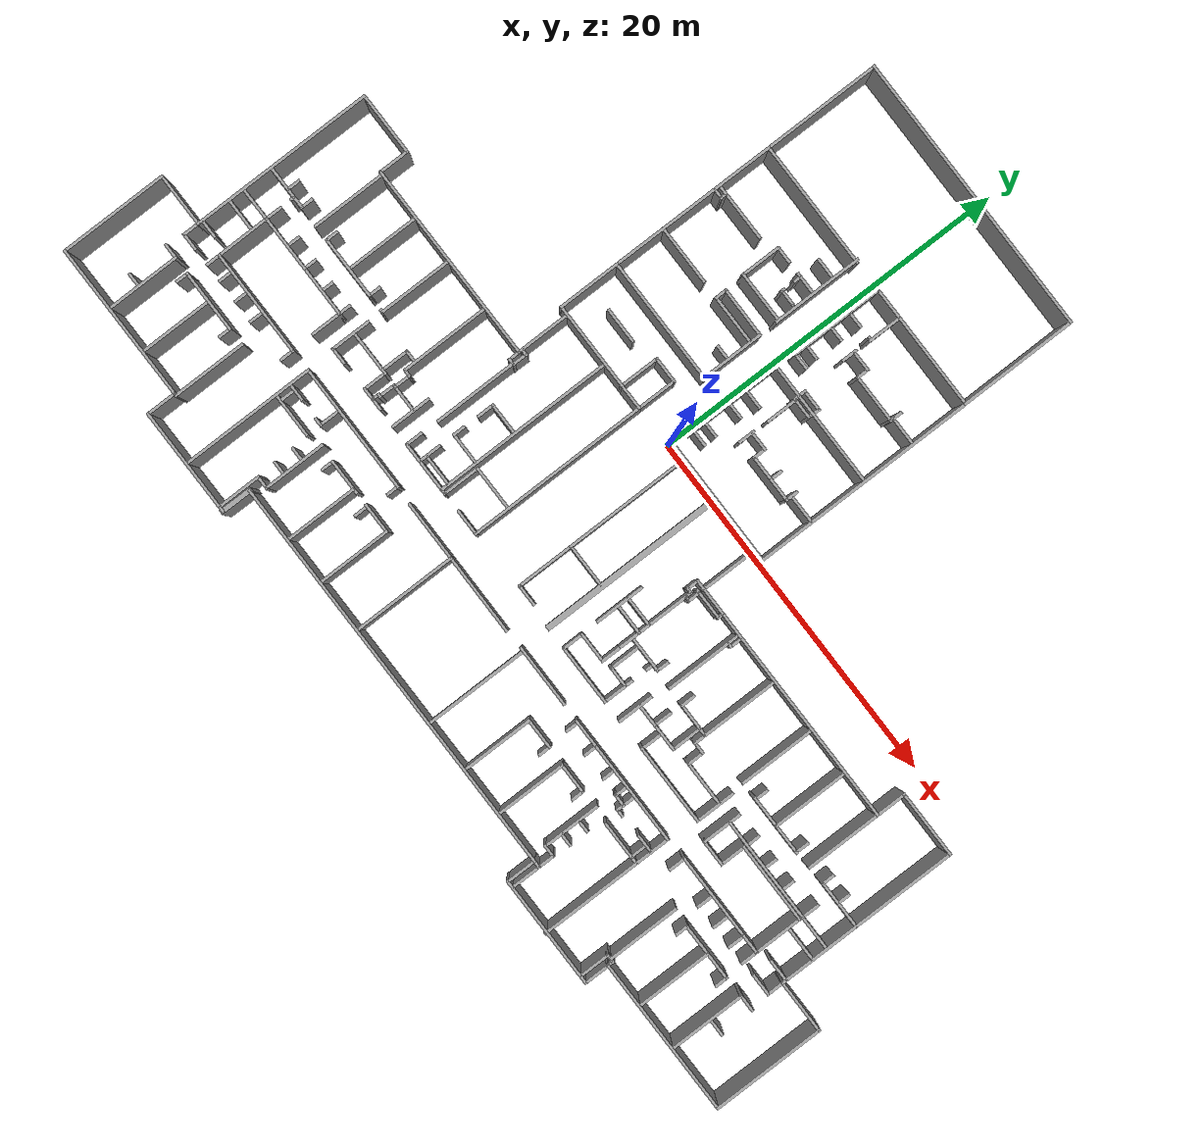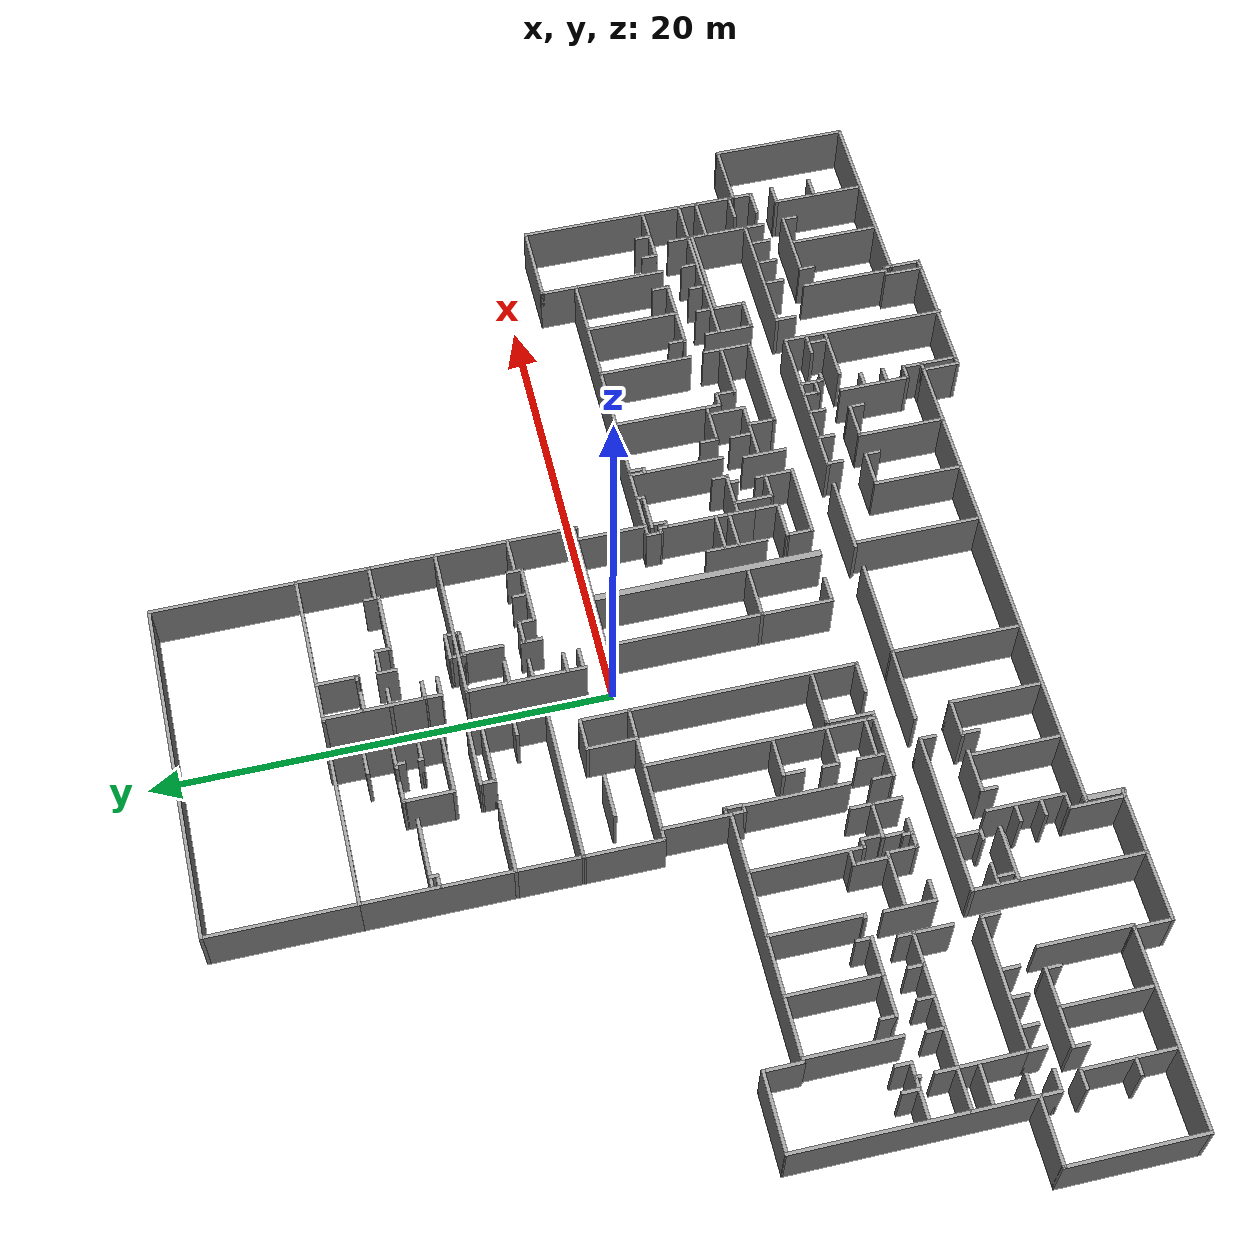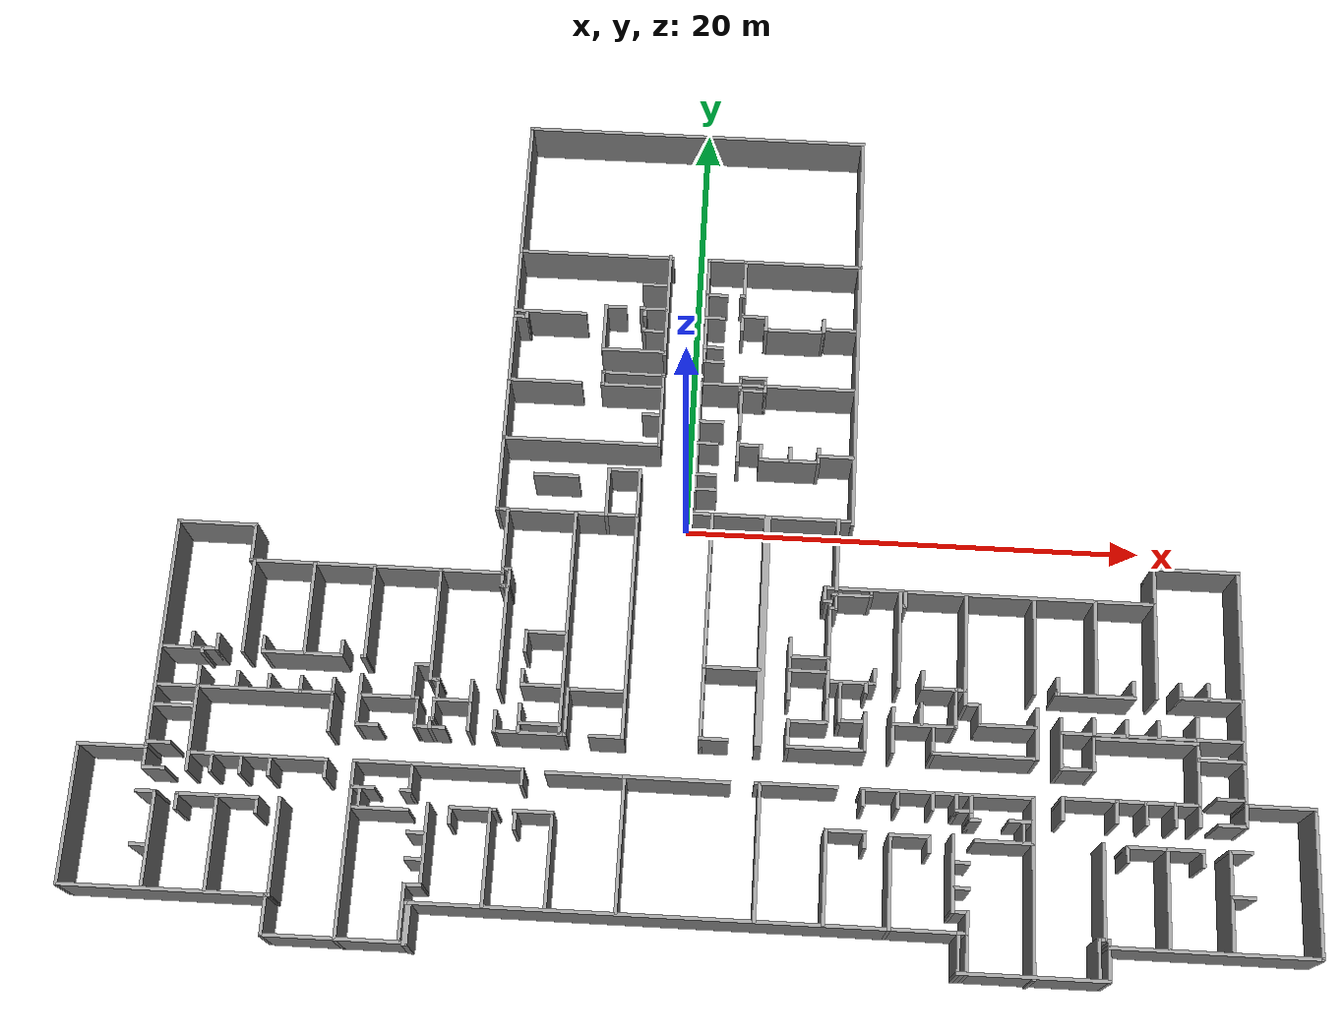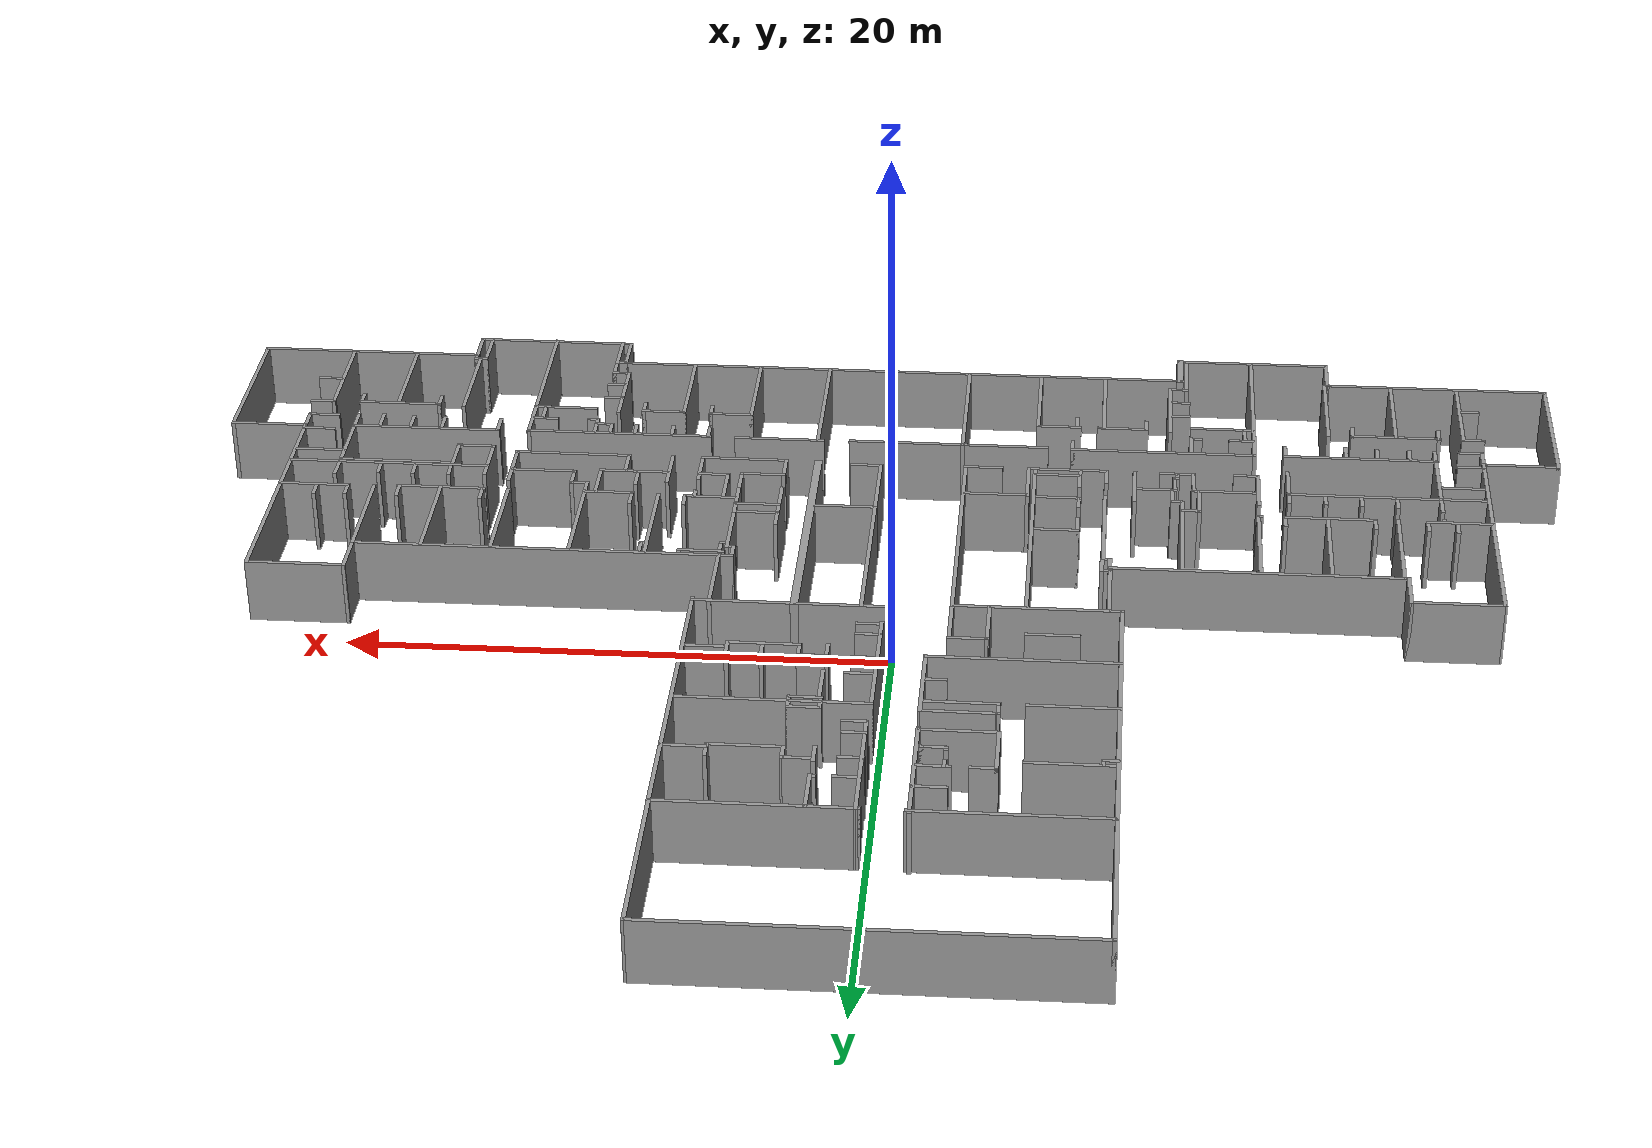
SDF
<?xml version='1.0'?>
<sdf version='1.6'>
  <model name='harnwell'>
    <pose frame=''>0.907995 -0.198073 0 0 -0 0</pose>
    <link name='Wall_0'>
      <collision name='Wall_0_Collision'>
        <geometry>
          <box>
            <size>15.5704 0.15 2.5</size>
          </box>
        </geometry>
        <pose frame=''>0 0 1.25 0 -0 0</pose>
      </collision>
      <visual name='Wall_0_Visual'>
        <pose frame=''>0 0 1.25 0 -0 0</pose>
        <geometry>
          <box>
            <size>15.5704 0.15 2.5</size>
          </box>
        </geometry>
        <material>
          <script>
            <uri>file://media/materials/scripts/gazebo.material</uri>
            <name>Gazebo/Grey</name>
          </script>
          <ambient>1 1 1 1</ambient>
        </material>
        <meta>
          <layer>0</layer>
        </meta>
      </visual>
      <pose frame=''>-1.44871 18.8469 0 0 -0 0</pose>
    </link>
    <link name='Wall_1'>
      <collision name='Wall_1_Collision'>
        <geometry>
          <box>
            <size>6.51013 0.15 2.5</size>
          </box>
        </geometry>
        <pose frame=''>0 0 1.25 0 -0 0</pose>
      </collision>
      <visual name='Wall_1_Visual'>
        <pose frame=''>0 0 1.25 0 -0 0</pose>
        <geometry>
          <box>
            <size>6.51013 0.15 2.5</size>
          </box>
        </geometry>
        <material>
          <script>
            <uri>file://media/materials/scripts/gazebo.material</uri>
            <name>Gazebo/Grey</name>
          </script>
          <ambient>1 1 1 1</ambient>
        </material>
        <meta>
          <layer>0</layer>
        </meta>
      </visual>
      <pose frame=''>6.27155 15.6669 0 0 -0 -1.56763</pose>
    </link>
    <link name='Wall_10'>
      <collision name='Wall_10_Collision'>
        <geometry>
          <box>
            <size>4.47203 0.15 2.5</size>
          </box>
        </geometry>
        <pose frame=''>0 0 1.25 0 -0 0</pose>
      </collision>
      <visual name='Wall_10_Visual'>
        <pose frame=''>0 0 1.25 0 -0 0</pose>
        <geometry>
          <box>
            <size>4.47203 0.15 2.5</size>
          </box>
        </geometry>
        <material>
          <script>
            <uri>file://media/materials/scripts/gazebo.material</uri>
            <name>Gazebo/Grey</name>
          </script>
          <ambient>1 1 1 1</ambient>
        </material>
        <meta>
          <layer>0</layer>
        </meta>
      </visual>
      <pose frame=''>-0.551724 10.3258 0 0 -0 1.57386</pose>
    </link>
    <link name='Wall_101'>
      <collision name='Wall_101_Collision'>
        <geometry>
          <box>
            <size>0.75 0.15 2.5</size>
          </box>
        </geometry>
        <pose frame=''>0 0 1.25 0 -0 0</pose>
      </collision>
      <visual name='Wall_101_Visual'>
        <pose frame=''>0 0 1.25 0 -0 0</pose>
        <geometry>
          <box>
            <size>0.75 0.15 2.5</size>
          </box>
        </geometry>
        <material>
          <script>
            <uri>file://media/materials/scripts/gazebo.material</uri>
            <name>Gazebo/Grey</name>
          </script>
          <ambient>1 1 1 1</ambient>
        </material>
        <meta>
          <layer>0</layer>
        </meta>
      </visual>
      <pose frame=''>1.13146 6.45541 0 0 -0 -1.5708</pose>
    </link>
    <link name='Wall_102'>
      <collision name='Wall_102_Collision'>
        <geometry>
          <box>
            <size>1.25 0.15 2.5</size>
          </box>
        </geometry>
        <pose frame=''>0 0 1.25 0 -0 0</pose>
      </collision>
      <visual name='Wall_102_Visual'>
        <pose frame=''>0 0 1.25 0 -0 0</pose>
        <geometry>
          <box>
            <size>1.25 0.15 2.5</size>
          </box>
        </geometry>
        <material>
          <script>
            <uri>file://media/materials/scripts/gazebo.material</uri>
            <name>Gazebo/Grey</name>
          </script>
          <ambient>1 1 1 1</ambient>
        </material>
        <meta>
          <layer>0</layer>
        </meta>
      </visual>
      <pose frame=''>1.68146 6.15541 0 0 -0 0</pose>
    </link>
    <link name='Wall_103'>
      <collision name='Wall_103_Collision'>
        <geometry>
          <box>
            <size>0.75 0.15 2.5</size>
          </box>
        </geometry>
        <pose frame=''>0 0 1.25 0 -0 0</pose>
      </collision>
      <visual name='Wall_103_Visual'>
        <pose frame=''>0 0 1.25 0 -0 0</pose>
        <geometry>
          <box>
            <size>0.75 0.15 2.5</size>
          </box>
        </geometry>
        <material>
          <script>
            <uri>file://media/materials/scripts/gazebo.material</uri>
            <name>Gazebo/Grey</name>
          </script>
          <ambient>1 1 1 1</ambient>
        </material>
        <meta>
          <layer>0</layer>
        </meta>
      </visual>
      <pose frame=''>2.23146 6.45541 0 0 -0 1.5708</pose>
    </link>
    <link name='Wall_104'>
      <collision name='Wall_104_Collision'>
        <geometry>
          <box>
            <size>1.25 0.15 2.5</size>
          </box>
        </geometry>
        <pose frame=''>0 0 1.25 0 -0 0</pose>
      </collision>
      <visual name='Wall_104_Visual'>
        <pose frame=''>0 0 1.25 0 -0 0</pose>
        <geometry>
          <box>
            <size>1.25 0.15 2.5</size>
          </box>
        </geometry>
        <material>
          <script>
            <uri>file://media/materials/scripts/gazebo.material</uri>
            <name>Gazebo/Grey</name>
          </script>
          <ambient>1 1 1 1</ambient>
        </material>
        <meta>
          <layer>0</layer>
        </meta>
      </visual>
      <pose frame=''>1.68146 6.75541 0 0 -0 3.14159</pose>
    </link>
    <link name='Wall_106'>
      <collision name='Wall_106_Collision'>
        <geometry>
          <box>
            <size>1.78516 0.15 2.5</size>
          </box>
        </geometry>
        <pose frame=''>0 0 1.25 0 -0 0</pose>
      </collision>
      <visual name='Wall_106_Visual'>
        <pose frame=''>0 0 1.25 0 -0 0</pose>
        <geometry>
          <box>
            <size>1.78516 0.15 2.5</size>
          </box>
        </geometry>
        <material>
          <script>
            <uri>file://media/materials/scripts/gazebo.material</uri>
            <name>Gazebo/Grey</name>
          </script>
          <ambient>1 1 1 1</ambient>
        </material>
        <meta>
          <layer>0</layer>
        </meta>
      </visual>
      <pose frame=''>1.19616 5.32615 0 0 -0 1.5708</pose>
    </link>
    <link name='Wall_108'>
      <collision name='Wall_108_Collision'>
        <geometry>
          <box>
            <size>1.16755 0.15 2.5</size>
          </box>
        </geometry>
        <pose frame=''>0 0 1.25 0 -0 0</pose>
      </collision>
      <visual name='Wall_108_Visual'>
        <pose frame=''>0 0 1.25 0 -0 0</pose>
        <geometry>
          <box>
            <size>1.16755 0.15 2.5</size>
          </box>
        </geometry>
        <material>
          <script>
            <uri>file://media/materials/scripts/gazebo.material</uri>
            <name>Gazebo/Grey</name>
          </script>
          <ambient>1 1 1 1</ambient>
        </material>
        <meta>
          <layer>0</layer>
        </meta>
      </visual>
      <pose frame=''>-0.094995 4.57307 0 0 -0 0</pose>
    </link>
    <link name='Wall_11'>
      <collision name='Wall_11_Collision'>
        <geometry>
          <box>
            <size>0.25 0.15 2.5</size>
          </box>
        </geometry>
        <pose frame=''>0 0 1.25 0 -0 0</pose>
      </collision>
      <visual name='Wall_11_Visual'>
        <pose frame=''>0 0 1.25 0 -0 0</pose>
        <geometry>
          <box>
            <size>0.25 0.15 2.5</size>
          </box>
        </geometry>
        <material>
          <script>
            <uri>file://media/materials/scripts/gazebo.material</uri>
            <name>Gazebo/Grey</name>
          </script>
          <ambient>1 1 1 1</ambient>
        </material>
        <meta>
          <layer>0</layer>
        </meta>
      </visual>
      <pose frame=''>-0.60834 12.4868 0 0 -0 3.14159</pose>
    </link>
    <link name='Wall_110'>
      <collision name='Wall_110_Collision'>
        <geometry>
          <box>
            <size>1 0.15 2.5</size>
          </box>
        </geometry>
        <pose frame=''>0 0 1.25 0 -0 0</pose>
      </collision>
      <visual name='Wall_110_Visual'>
        <pose frame=''>0 0 1.25 0 -0 0</pose>
        <geometry>
          <box>
            <size>1 0.15 2.5</size>
          </box>
        </geometry>
        <material>
          <script>
            <uri>file://media/materials/scripts/gazebo.material</uri>
            <name>Gazebo/Grey</name>
          </script>
          <ambient>1 1 1 1</ambient>
        </material>
        <meta>
          <layer>0</layer>
        </meta>
      </visual>
      <pose frame=''>-0.181677 3.55575 0 0 -0 3.14159</pose>
    </link>
    <link name='Wall_112'>
      <collision name='Wall_112_Collision'>
        <geometry>
          <box>
            <size>1 0.15 2.5</size>
          </box>
        </geometry>
        <pose frame=''>0 0 1.25 0 -0 0</pose>
      </collision>
      <visual name='Wall_112_Visual'>
        <pose frame=''>0 0 1.25 0 -0 0</pose>
        <geometry>
          <box>
            <size>1 0.15 2.5</size>
          </box>
        </geometry>
        <material>
          <script>
            <uri>file://media/materials/scripts/gazebo.material</uri>
            <name>Gazebo/Grey</name>
          </script>
          <ambient>1 1 1 1</ambient>
        </material>
        <meta>
          <layer>0</layer>
        </meta>
      </visual>
      <pose frame=''>-0.199322 2.07356 0 0 -0 3.14159</pose>
    </link>
    <link name='Wall_114'>
      <collision name='Wall_114_Collision'>
        <geometry>
          <box>
            <size>0.96775 0.15 2.5</size>
          </box>
        </geometry>
        <pose frame=''>0 0 1.25 0 -0 0</pose>
      </collision>
      <visual name='Wall_114_Visual'>
        <pose frame=''>0 0 1.25 0 -0 0</pose>
        <geometry>
          <box>
            <size>0.96775 0.15 2.5</size>
          </box>
        </geometry>
        <material>
          <script>
            <uri>file://media/materials/scripts/gazebo.material</uri>
            <name>Gazebo/Grey</name>
          </script>
          <ambient>1 1 1 1</ambient>
        </material>
        <meta>
          <layer>0</layer>
        </meta>
      </visual>
      <pose frame=''>-0.165457 1.39716 0 0 -0 3.14159</pose>
    </link>
    <link name='Wall_116'>
      <collision name='Wall_116_Collision'>
        <geometry>
          <box>
            <size>0.972551 0.15 2.5</size>
          </box>
        </geometry>
        <pose frame=''>0 0 1.25 0 -0 0</pose>
      </collision>
      <visual name='Wall_116_Visual'>
        <pose frame=''>0 0 1.25 0 -0 0</pose>
        <geometry>
          <box>
            <size>0.972551 0.15 2.5</size>
          </box>
        </geometry>
        <material>
          <script>
            <uri>file://media/materials/scripts/gazebo.material</uri>
            <name>Gazebo/Grey</name>
          </script>
          <ambient>1 1 1 1</ambient>
        </material>
        <meta>
          <layer>0</layer>
        </meta>
      </visual>
      <pose frame=''>1.16104 3.2402 0 0 -0 -1.5708</pose>
    </link>
    <link name='Wall_119'>
      <collision name='Wall_119_Collision'>
        <geometry>
          <box>
            <size>1.12307 0.15 2.5</size>
          </box>
        </geometry>
        <pose frame=''>0 0 1.25 0 -0 0</pose>
      </collision>
      <visual name='Wall_119_Visual'>
        <pose frame=''>0 0 1.25 0 -0 0</pose>
        <geometry>
          <box>
            <size>1.12307 0.15 2.5</size>
          </box>
        </geometry>
        <material>
          <script>
            <uri>file://media/materials/scripts/gazebo.material</uri>
            <name>Gazebo/Grey</name>
          </script>
          <ambient>1 1 1 1</ambient>
        </material>
        <meta>
          <layer>0</layer>
        </meta>
      </visual>
      <pose frame=''>1.67379 3.55413 0 0 -0 -0.000113</pose>
    </link>
    <link name='Wall_12'>
      <collision name='Wall_12_Collision'>
        <geometry>
          <box>
            <size>0.25 0.15 2.5</size>
          </box>
        </geometry>
        <pose frame=''>0 0 1.25 0 -0 0</pose>
      </collision>
      <visual name='Wall_12_Visual'>
        <pose frame=''>0 0 1.25 0 -0 0</pose>
        <geometry>
          <box>
            <size>0.25 0.15 2.5</size>
          </box>
        </geometry>
        <material>
          <script>
            <uri>file://media/materials/scripts/gazebo.material</uri>
            <name>Gazebo/Grey</name>
          </script>
          <ambient>1 1 1 1</ambient>
        </material>
        <meta>
          <layer>0</layer>
        </meta>
      </visual>
      <pose frame=''>-0.60834 12.4868 0 0 -0 0</pose>
    </link>
    <link name='Wall_120'>
      <collision name='Wall_120_Collision'>
        <geometry>
          <box>
            <size>0.795673 0.15 2.5</size>
          </box>
        </geometry>
        <pose frame=''>0 0 1.25 0 -0 0</pose>
      </collision>
      <visual name='Wall_120_Visual'>
        <pose frame=''>0 0 1.25 0 -0 0</pose>
        <geometry>
          <box>
            <size>0.795673 0.15 2.5</size>
          </box>
        </geometry>
        <material>
          <script>
            <uri>file://media/materials/scripts/gazebo.material</uri>
            <name>Gazebo/Grey</name>
          </script>
          <ambient>1 1 1 1</ambient>
        </material>
        <meta>
          <layer>0</layer>
        </meta>
      </visual>
      <pose frame=''>2.16 3.23107 0 0 -0 -1.5708</pose>
    </link>
    <link name='Wall_122'>
      <collision name='Wall_122_Collision'>
        <geometry>
          <box>
            <size>2.70661 0.15 2.5</size>
          </box>
        </geometry>
        <pose frame=''>0 0 1.25 0 -0 0</pose>
      </collision>
      <visual name='Wall_122_Visual'>
        <pose frame=''>0 0 1.25 0 -0 0</pose>
        <geometry>
          <box>
            <size>2.70661 0.15 2.5</size>
          </box>
        </geometry>
        <material>
          <script>
            <uri>file://media/materials/scripts/gazebo.material</uri>
            <name>Gazebo/Grey</name>
          </script>
          <ambient>1 1 1 1</ambient>
        </material>
        <meta>
          <layer>0</layer>
        </meta>
      </visual>
      <pose frame=''>3.43851 2.90807 0 0 -0 0</pose>
    </link>
    <link name='Wall_125'>
      <collision name='Wall_125_Collision'>
        <geometry>
          <box>
            <size>0.75 0.15 2.5</size>
          </box>
        </geometry>
        <pose frame=''>0 0 1.25 0 -0 0</pose>
      </collision>
      <visual name='Wall_125_Visual'>
        <pose frame=''>0 0 1.25 0 -0 0</pose>
        <geometry>
          <box>
            <size>0.75 0.15 2.5</size>
          </box>
        </geometry>
        <material>
          <script>
            <uri>file://media/materials/scripts/gazebo.material</uri>
            <name>Gazebo/Grey</name>
          </script>
          <ambient>1 1 1 1</ambient>
        </material>
        <meta>
          <layer>0</layer>
        </meta>
      </visual>
      <pose frame=''>4.71701 3.20807 0 0 -0 1.5708</pose>
    </link>
    <link name='Wall_127'>
      <collision name='Wall_127_Collision'>
        <geometry>
          <box>
            <size>0.75 0.15 2.5</size>
          </box>
        </geometry>
        <pose frame=''>0 0 1.25 0 -0 0</pose>
      </collision>
      <visual name='Wall_127_Visual'>
        <pose frame=''>0 0 1.25 0 -0 0</pose>
        <geometry>
          <box>
            <size>0.75 0.15 2.5</size>
          </box>
        </geometry>
        <material>
          <script>
            <uri>file://media/materials/scripts/gazebo.material</uri>
            <name>Gazebo/Grey</name>
          </script>
          <ambient>1 1 1 1</ambient>
        </material>
        <meta>
          <layer>0</layer>
        </meta>
      </visual>
      <pose frame=''>3.47391 3.21295 0 0 -0 1.5708</pose>
    </link>
    <link name='Wall_130'>
      <collision name='Wall_130_Collision'>
        <geometry>
          <box>
            <size>1.69791 0.15 2.5</size>
          </box>
        </geometry>
        <pose frame=''>0 0 1.25 0 -0 0</pose>
      </collision>
      <visual name='Wall_130_Visual'>
        <pose frame=''>0 0 1.25 0 -0 0</pose>
        <geometry>
          <box>
            <size>1.69791 0.15 2.5</size>
          </box>
        </geometry>
        <material>
          <script>
            <uri>file://media/materials/scripts/gazebo.material</uri>
            <name>Gazebo/Grey</name>
          </script>
          <ambient>1 1 1 1</ambient>
        </material>
        <meta>
          <layer>0</layer>
        </meta>
      </visual>
      <pose frame=''>5.51702 3.20261 0 0 -0 -3.13874</pose>
    </link>
    <link name='Wall_132'>
      <collision name='Wall_132_Collision'>
        <geometry>
          <box>
            <size>3.5 0.15 2.5</size>
          </box>
        </geometry>
        <pose frame=''>0 0 1.25 0 -0 0</pose>
      </collision>
      <visual name='Wall_132_Visual'>
        <pose frame=''>0 0 1.25 0 -0 0</pose>
        <geometry>
          <box>
            <size>3.5 0.15 2.5</size>
          </box>
        </geometry>
        <material>
          <script>
            <uri>file://media/materials/scripts/gazebo.material</uri>
            <name>Gazebo/Grey</name>
          </script>
          <ambient>1 1 1 1</ambient>
        </material>
        <meta>
          <layer>0</layer>
        </meta>
      </visual>
      <pose frame=''>-9.16586 1.67152 0 0 -0 -1.5708</pose>
    </link>
    <link name='Wall_133'>
      <collision name='Wall_133_Collision'>
        <geometry>
          <box>
            <size>6.25 0.15 2.5</size>
          </box>
        </geometry>
        <pose frame=''>0 0 1.25 0 -0 0</pose>
      </collision>
      <visual name='Wall_133_Visual'>
        <pose frame=''>0 0 1.25 0 -0 0</pose>
        <geometry>
          <box>
            <size>6.25 0.15 2.5</size>
          </box>
        </geometry>
        <material>
          <script>
            <uri>file://media/materials/scripts/gazebo.material</uri>
            <name>Gazebo/Grey</name>
          </script>
          <ambient>1 1 1 1</ambient>
        </material>
        <meta>
          <layer>0</layer>
        </meta>
      </visual>
      <pose frame=''>-6.11586 -0.003478 0 0 -0 0</pose>
    </link>
    <link name='Wall_135'>
      <collision name='Wall_135_Collision'>
        <geometry>
          <box>
            <size>2.25 0.15 2.5</size>
          </box>
        </geometry>
        <pose frame=''>0 0 1.25 0 -0 0</pose>
      </collision>
      <visual name='Wall_135_Visual'>
        <pose frame=''>0 0 1.25 0 -0 0</pose>
        <geometry>
          <box>
            <size>2.25 0.15 2.5</size>
          </box>
        </geometry>
        <material>
          <script>
            <uri>file://media/materials/scripts/gazebo.material</uri>
            <name>Gazebo/Grey</name>
          </script>
          <ambient>1 1 1 1</ambient>
        </material>
        <meta>
          <layer>0</layer>
        </meta>
      </visual>
      <pose frame=''>-3.06586 1.04652 0 0 -0 1.5708</pose>
    </link>
    <link name='Wall_136'>
      <collision name='Wall_136_Collision'>
        <geometry>
          <box>
            <size>1.5 0.15 2.5</size>
          </box>
        </geometry>
        <pose frame=''>0 0 1.25 0 -0 0</pose>
      </collision>
      <visual name='Wall_136_Visual'>
        <pose frame=''>0 0 1.25 0 -0 0</pose>
        <geometry>
          <box>
            <size>1.5 0.15 2.5</size>
          </box>
        </geometry>
        <material>
          <script>
            <uri>file://media/materials/scripts/gazebo.material</uri>
            <name>Gazebo/Grey</name>
          </script>
          <ambient>1 1 1 1</ambient>
        </material>
        <meta>
          <layer>0</layer>
        </meta>
      </visual>
      <pose frame=''>-3.74086 2.09652 0 0 -0 3.14159</pose>
    </link>
    <link name='Wall_137'>
      <collision name='Wall_137_Collision'>
        <geometry>
          <box>
            <size>2.25 0.15 2.5</size>
          </box>
        </geometry>
        <pose frame=''>0 0 1.25 0 -0 0</pose>
      </collision>
      <visual name='Wall_137_Visual'>
        <pose frame=''>0 0 1.25 0 -0 0</pose>
        <geometry>
          <box>
            <size>2.25 0.15 2.5</size>
          </box>
        </geometry>
        <material>
          <script>
            <uri>file://media/materials/scripts/gazebo.material</uri>
            <name>Gazebo/Grey</name>
          </script>
          <ambient>1 1 1 1</ambient>
        </material>
        <meta>
          <layer>0</layer>
        </meta>
      </visual>
      <pose frame=''>-4.41586 1.04652 0 0 -0 -1.5708</pose>
    </link>
    <link name='Wall_139'>
      <collision name='Wall_139_Collision'>
        <geometry>
          <box>
            <size>2 0.15 2.5</size>
          </box>
        </geometry>
        <pose frame=''>0 0 1.25 0 -0 0</pose>
      </collision>
      <visual name='Wall_139_Visual'>
        <pose frame=''>0 0 1.25 0 -0 0</pose>
        <geometry>
          <box>
            <size>2 0.15 2.5</size>
          </box>
        </geometry>
        <material>
          <script>
            <uri>file://media/materials/scripts/gazebo.material</uri>
            <name>Gazebo/Grey</name>
          </script>
          <ambient>1 1 1 1</ambient>
        </material>
        <meta>
          <layer>0</layer>
        </meta>
      </visual>
      <pose frame=''>-6.7235 1.70166 0 0 -0 0</pose>
    </link>
    <link name='Wall_143'>
      <collision name='Wall_143_Collision'>
        <geometry>
          <box>
            <size>14.25 0.15 2.5</size>
          </box>
        </geometry>
        <pose frame=''>0 0 1.25 0 -0 0</pose>
      </collision>
      <visual name='Wall_143_Visual'>
        <pose frame=''>0 0 1.25 0 -0 0</pose>
        <geometry>
          <box>
            <size>14.25 0.15 2.5</size>
          </box>
        </geometry>
        <material>
          <script>
            <uri>file://media/materials/scripts/gazebo.material</uri>
            <name>Gazebo/Grey</name>
          </script>
          <ambient>1 1 1 1</ambient>
        </material>
        <meta>
          <layer>0</layer>
        </meta>
      </visual>
      <pose frame=''>12.25 -2.82962 0 0 -0 0</pose>
    </link>
    <link name='Wall_144'>
      <collision name='Wall_144_Collision'>
        <geometry>
          <box>
            <size>1.75 0.15 2.5</size>
          </box>
        </geometry>
        <pose frame=''>0 0 1.25 0 -0 0</pose>
      </collision>
      <visual name='Wall_144_Visual'>
        <pose frame=''>0 0 1.25 0 -0 0</pose>
        <geometry>
          <box>
            <size>1.75 0.15 2.5</size>
          </box>
        </geometry>
        <material>
          <script>
            <uri>file://media/materials/scripts/gazebo.material</uri>
            <name>Gazebo/Grey</name>
          </script>
          <ambient>1 1 1 1</ambient>
        </material>
        <meta>
          <layer>0</layer>
        </meta>
      </visual>
      <pose frame=''>19.3 -2.02962 0 0 -0 1.5708</pose>
    </link>
    <link name='Wall_146'>
      <collision name='Wall_146_Collision'>
        <geometry>
          <box>
            <size>0.75 0.15 2.5</size>
          </box>
        </geometry>
        <pose frame=''>0 0 1.25 0 -0 0</pose>
      </collision>
      <visual name='Wall_146_Visual'>
        <pose frame=''>0 0 1.25 0 -0 0</pose>
        <geometry>
          <box>
            <size>0.75 0.15 2.5</size>
          </box>
        </geometry>
        <material>
          <script>
            <uri>file://media/materials/scripts/gazebo.material</uri>
            <name>Gazebo/Grey</name>
          </script>
          <ambient>1 1 1 1</ambient>
        </material>
        <meta>
          <layer>0</layer>
        </meta>
      </visual>
      <pose frame=''>5.19998 -3.12962 0 0 -0 -1.5708</pose>
    </link>
    <link name='Wall_147'>
      <collision name='Wall_147_Collision'>
        <geometry>
          <box>
            <size>0.394027 0.15 2.5</size>
          </box>
        </geometry>
        <pose frame=''>0 0 1.25 0 -0 0</pose>
      </collision>
      <visual name='Wall_147_Visual'>
        <pose frame=''>0 0 1.25 0 -0 0</pose>
        <geometry>
          <box>
            <size>0.394027 0.15 2.5</size>
          </box>
        </geometry>
        <material>
          <script>
            <uri>file://media/materials/scripts/gazebo.material</uri>
            <name>Gazebo/Grey</name>
          </script>
          <ambient>1 1 1 1</ambient>
        </material>
        <meta>
          <layer>0</layer>
        </meta>
      </visual>
      <pose frame=''>5.32199 -3.42977 0 0 -0 -0.00125</pose>
    </link>
    <link name='Wall_150'>
      <collision name='Wall_150_Collision'>
        <geometry>
          <box>
            <size>10.25 0.3 2.5</size>
          </box>
        </geometry>
        <pose frame=''>0 0 1.25 0 -0 0</pose>
      </collision>
      <visual name='Wall_150_Visual'>
        <pose frame=''>0 0 1.25 0 -0 0</pose>
        <geometry>
          <box>
            <size>10.25 0.3 2.5</size>
          </box>
        </geometry>
        <material>
          <script>
            <uri>file://media/materials/scripts/gazebo.material</uri>
            <name>Gazebo/Grey</name>
          </script>
          <ambient>1 1 1 1</ambient>
        </material>
        <meta>
          <layer>0</layer>
        </meta>
      </visual>
      <pose frame=''>2.60701 -4.80593 0 0 -0 1.5708</pose>
    </link>
    <link name='Wall_153'>
      <collision name='Wall_153_Collision'>
        <geometry>
          <box>
            <size>2.75 0.15 2.5</size>
          </box>
        </geometry>
        <pose frame=''>0 0 1.25 0 -0 0</pose>
      </collision>
      <visual name='Wall_153_Visual'>
        <pose frame=''>0 0 1.25 0 -0 0</pose>
        <geometry>
          <box>
            <size>2.75 0.15 2.5</size>
          </box>
        </geometry>
        <material>
          <script>
            <uri>file://media/materials/scripts/gazebo.material</uri>
            <name>Gazebo/Grey</name>
          </script>
          <ambient>1 1 1 1</ambient>
        </material>
        <meta>
          <layer>0</layer>
        </meta>
      </visual>
      <pose frame=''>3.8126 -6.4747 0 0 -0 -1.5708</pose>
    </link>
    <link name='Wall_155'>
      <collision name='Wall_155_Collision'>
        <geometry>
          <box>
            <size>1.75 0.15 2.5</size>
          </box>
        </geometry>
        <pose frame=''>0 0 1.25 0 -0 0</pose>
      </collision>
      <visual name='Wall_155_Visual'>
        <pose frame=''>0 0 1.25 0 -0 0</pose>
        <geometry>
          <box>
            <size>1.75 0.15 2.5</size>
          </box>
        </geometry>
        <material>
          <script>
            <uri>file://media/materials/scripts/gazebo.material</uri>
            <name>Gazebo/Grey</name>
          </script>
          <ambient>1 1 1 1</ambient>
        </material>
        <meta>
          <layer>0</layer>
        </meta>
      </visual>
      <pose frame=''>4.64354 -6.5592 0 0 -0 0</pose>
    </link>
    <link name='Wall_156'>
      <collision name='Wall_156_Collision'>
        <geometry>
          <box>
            <size>0.75 0.15 2.5</size>
          </box>
        </geometry>
        <pose frame=''>0 0 1.25 0 -0 0</pose>
      </collision>
      <visual name='Wall_156_Visual'>
        <pose frame=''>0 0 1.25 0 -0 0</pose>
        <geometry>
          <box>
            <size>0.75 0.15 2.5</size>
          </box>
        </geometry>
        <material>
          <script>
            <uri>file://media/materials/scripts/gazebo.material</uri>
            <name>Gazebo/Grey</name>
          </script>
          <ambient>1 1 1 1</ambient>
        </material>
        <meta>
          <layer>0</layer>
        </meta>
      </visual>
      <pose frame=''>5.44377 -6.25906 0 0 -0 1.57002</pose>
    </link>
    <link name='Wall_157'>
      <collision name='Wall_157_Collision'>
        <geometry>
          <box>
            <size>1.75 0.15 2.5</size>
          </box>
        </geometry>
        <pose frame=''>0 0 1.25 0 -0 0</pose>
      </collision>
      <visual name='Wall_157_Visual'>
        <pose frame=''>0 0 1.25 0 -0 0</pose>
        <geometry>
          <box>
            <size>1.75 0.15 2.5</size>
          </box>
        </geometry>
        <material>
          <script>
            <uri>file://media/materials/scripts/gazebo.material</uri>
            <name>Gazebo/Grey</name>
          </script>
          <ambient>1 1 1 1</ambient>
        </material>
        <meta>
          <layer>0</layer>
        </meta>
      </visual>
      <pose frame=''>4.64377 -5.95906 0 0 -0 -3.14142</pose>
    </link>
    <link name='Wall_159'>
      <collision name='Wall_159_Collision'>
        <geometry>
          <box>
            <size>2.67942 0.15 2.5</size>
          </box>
        </geometry>
        <pose frame=''>0 0 1.25 0 -0 0</pose>
      </collision>
      <visual name='Wall_159_Visual'>
        <pose frame=''>0 0 1.25 0 -0 0</pose>
        <geometry>
          <box>
            <size>2.67942 0.15 2.5</size>
          </box>
        </geometry>
        <material>
          <script>
            <uri>file://media/materials/scripts/gazebo.material</uri>
            <name>Gazebo/Grey</name>
          </script>
          <ambient>1 1 1 1</ambient>
        </material>
        <meta>
          <layer>0</layer>
        </meta>
      </visual>
      <pose frame=''>5.444 -4.69443 0 0 -0 1.5708</pose>
    </link>
    <link name='Wall_161'>
      <collision name='Wall_161_Collision'>
        <geometry>
          <box>
            <size>1.25 0.15 2.5</size>
          </box>
        </geometry>
        <pose frame=''>0 0 1.25 0 -0 0</pose>
      </collision>
      <visual name='Wall_161_Visual'>
        <pose frame=''>0 0 1.25 0 -0 0</pose>
        <geometry>
          <box>
            <size>1.25 0.15 2.5</size>
          </box>
        </geometry>
        <material>
          <script>
            <uri>file://media/materials/scripts/gazebo.material</uri>
            <name>Gazebo/Grey</name>
          </script>
          <ambient>1 1 1 1</ambient>
        </material>
        <meta>
          <layer>0</layer>
        </meta>
      </visual>
      <pose frame=''>5.44354 -7.1092 0 0 -0 -1.5708</pose>
    </link>
    <link name='Wall_162'>
      <collision name='Wall_162_Collision'>
        <geometry>
          <box>
            <size>1.25 0.15 2.5</size>
          </box>
        </geometry>
        <pose frame=''>0 0 1.25 0 -0 0</pose>
      </collision>
      <visual name='Wall_162_Visual'>
        <pose frame=''>0 0 1.25 0 -0 0</pose>
        <geometry>
          <box>
            <size>1.25 0.15 2.5</size>
          </box>
        </geometry>
        <material>
          <script>
            <uri>file://media/materials/scripts/gazebo.material</uri>
            <name>Gazebo/Grey</name>
          </script>
          <ambient>1 1 1 1</ambient>
        </material>
        <meta>
          <layer>0</layer>
        </meta>
      </visual>
      <pose frame=''>5.44354 -8.2092 0 0 -0 -1.5708</pose>
    </link>
    <link name='Wall_163'>
      <collision name='Wall_163_Collision'>
        <geometry>
          <box>
            <size>1.75 0.15 2.5</size>
          </box>
        </geometry>
        <pose frame=''>0 0 1.25 0 -0 0</pose>
      </collision>
      <visual name='Wall_163_Visual'>
        <pose frame=''>0 0 1.25 0 -0 0</pose>
        <geometry>
          <box>
            <size>1.75 0.15 2.5</size>
          </box>
        </geometry>
        <material>
          <script>
            <uri>file://media/materials/scripts/gazebo.material</uri>
            <name>Gazebo/Grey</name>
          </script>
          <ambient>1 1 1 1</ambient>
        </material>
        <meta>
          <layer>0</layer>
        </meta>
      </visual>
      <pose frame=''>4.64354 -8.7592 0 0 -0 3.14159</pose>
    </link>
    <link name='Wall_165'>
      <collision name='Wall_165_Collision'>
        <geometry>
          <box>
            <size>1.25 0.15 2.5</size>
          </box>
        </geometry>
        <pose frame=''>0 0 1.25 0 -0 0</pose>
      </collision>
      <visual name='Wall_165_Visual'>
        <pose frame=''>0 0 1.25 0 -0 0</pose>
        <geometry>
          <box>
            <size>1.25 0.15 2.5</size>
          </box>
        </geometry>
        <material>
          <script>
            <uri>file://media/materials/scripts/gazebo.material</uri>
            <name>Gazebo/Grey</name>
          </script>
          <ambient>1 1 1 1</ambient>
        </material>
        <meta>
          <layer>0</layer>
        </meta>
      </visual>
      <pose frame=''>3.84377 -9.30906 0 0 -0 -1.57037</pose>
    </link>
    <link name='Wall_166'>
      <collision name='Wall_166_Collision'>
        <geometry>
          <box>
            <size>3.3708 0.15 2.5</size>
          </box>
        </geometry>
        <pose frame=''>0 0 1.25 0 -0 0</pose>
      </collision>
      <visual name='Wall_166_Visual'>
        <pose frame=''>0 0 1.25 0 -0 0</pose>
        <geometry>
          <box>
            <size>3.3708 0.15 2.5</size>
          </box>
        </geometry>
        <material>
          <script>
            <uri>file://media/materials/scripts/gazebo.material</uri>
            <name>Gazebo/Grey</name>
          </script>
          <ambient>1 1 1 1</ambient>
        </material>
        <meta>
          <layer>0</layer>
        </meta>
      </visual>
      <pose frame=''>5.45451 -9.85893 0 0 -0 0</pose>
    </link>
    <link name='Wall_169'>
      <collision name='Wall_169_Collision'>
        <geometry>
          <box>
            <size>1.75 0.15 2.5</size>
          </box>
        </geometry>
        <pose frame=''>0 0 1.25 0 -0 0</pose>
      </collision>
      <visual name='Wall_169_Visual'>
        <pose frame=''>0 0 1.25 0 -0 0</pose>
        <geometry>
          <box>
            <size>1.75 0.15 2.5</size>
          </box>
        </geometry>
        <material>
          <script>
            <uri>file://media/materials/scripts/gazebo.material</uri>
            <name>Gazebo/Grey</name>
          </script>
          <ambient>1 1 1 1</ambient>
        </material>
        <meta>
          <layer>0</layer>
        </meta>
      </visual>
      <pose frame=''>7.06501 -9.05893 0 0 -0 1.5708</pose>
    </link>
    <link name='Wall_171'>
      <collision name='Wall_171_Collision'>
        <geometry>
          <box>
            <size>0.75 0.15 2.5</size>
          </box>
        </geometry>
        <pose frame=''>0 0 1.25 0 -0 0</pose>
      </collision>
      <visual name='Wall_171_Visual'>
        <pose frame=''>0 0 1.25 0 -0 0</pose>
        <geometry>
          <box>
            <size>0.75 0.15 2.5</size>
          </box>
        </geometry>
        <material>
          <script>
            <uri>file://media/materials/scripts/gazebo.material</uri>
            <name>Gazebo/Grey</name>
          </script>
          <ambient>1 1 1 1</ambient>
        </material>
        <meta>
          <layer>0</layer>
        </meta>
      </visual>
      <pose frame=''>7.41354 -6.65701 0 0 -0 -1.5708</pose>
    </link>
    <link name='Wall_172'>
      <collision name='Wall_172_Collision'>
        <geometry>
          <box>
            <size>2 0.15 2.5</size>
          </box>
        </geometry>
        <pose frame=''>0 0 1.25 0 -0 0</pose>
      </collision>
      <visual name='Wall_172_Visual'>
        <pose frame=''>0 0 1.25 0 -0 0</pose>
        <geometry>
          <box>
            <size>2 0.15 2.5</size>
          </box>
        </geometry>
        <material>
          <script>
            <uri>file://media/materials/scripts/gazebo.material</uri>
            <name>Gazebo/Grey</name>
          </script>
          <ambient>1 1 1 1</ambient>
        </material>
        <meta>
          <layer>0</layer>
        </meta>
      </visual>
      <pose frame=''>6.48853 -6.95701 0 0 -0 3.14159</pose>
    </link>
    <link name='Wall_174'>
      <collision name='Wall_174_Collision'>
        <geometry>
          <box>
            <size>0.5 0.15 2.5</size>
          </box>
        </geometry>
        <pose frame=''>0 0 1.25 0 -0 0</pose>
      </collision>
      <visual name='Wall_174_Visual'>
        <pose frame=''>0 0 1.25 0 -0 0</pose>
        <geometry>
          <box>
            <size>0.5 0.15 2.5</size>
          </box>
        </geometry>
        <material>
          <script>
            <uri>file://media/materials/scripts/gazebo.material</uri>
            <name>Gazebo/Grey</name>
          </script>
          <ambient>1 1 1 1</ambient>
        </material>
        <meta>
          <layer>0</layer>
        </meta>
      </visual>
      <pose frame=''>7.06651 -7.15547 0 0 -0 -1.5708</pose>
    </link>
    <link name='Wall_176'>
      <collision name='Wall_176_Collision'>
        <geometry>
          <box>
            <size>1.25 0.15 2.5</size>
          </box>
        </geometry>
        <pose frame=''>0 0 1.25 0 -0 0</pose>
      </collision>
      <visual name='Wall_176_Visual'>
        <pose frame=''>0 0 1.25 0 -0 0</pose>
        <geometry>
          <box>
            <size>1.25 0.15 2.5</size>
          </box>
        </geometry>
        <material>
          <script>
            <uri>file://media/materials/scripts/gazebo.material</uri>
            <name>Gazebo/Grey</name>
          </script>
          <ambient>1 1 1 1</ambient>
        </material>
        <meta>
          <layer>0</layer>
        </meta>
      </visual>
      <pose frame=''>6.52251 -8.63324 0 0 -0 0</pose>
    </link>
    <link name='Wall_178'>
      <collision name='Wall_178_Collision'>
        <geometry>
          <box>
            <size>1.75 0.15 2.5</size>
          </box>
        </geometry>
        <pose frame=''>0 0 1.25 0 -0 0</pose>
      </collision>
      <visual name='Wall_178_Visual'>
        <pose frame=''>0 0 1.25 0 -0 0</pose>
        <geometry>
          <box>
            <size>1.75 0.15 2.5</size>
          </box>
        </geometry>
        <material>
          <script>
            <uri>file://media/materials/scripts/gazebo.material</uri>
            <name>Gazebo/Grey</name>
          </script>
          <ambient>1 1 1 1</ambient>
        </material>
        <meta>
          <layer>0</layer>
        </meta>
      </visual>
      <pose frame=''>5.97251 -7.83324 0 0 -0 1.5708</pose>
    </link>
    <link name='Wall_183'>
      <collision name='Wall_183_Collision'>
        <geometry>
          <box>
            <size>0.371226 0.15 2.5</size>
          </box>
        </geometry>
        <pose frame=''>0 0 1.25 0 -0 0</pose>
      </collision>
      <visual name='Wall_183_Visual'>
        <pose frame=''>0 0 1.25 0 -0 0</pose>
        <geometry>
          <box>
            <size>0.371226 0.15 2.5</size>
          </box>
        </geometry>
        <material>
          <script>
            <uri>file://media/materials/scripts/gazebo.material</uri>
            <name>Gazebo/Grey</name>
          </script>
          <ambient>1 1 1 1</ambient>
        </material>
        <meta>
          <layer>0</layer>
        </meta>
      </visual>
      <pose frame=''>7.184 -2.99743 0 0 -0 -1.5708</pose>
    </link>
    <link name='Wall_187'>
      <collision name='Wall_187_Collision'>
        <geometry>
          <box>
            <size>1.769 0.15 2.5</size>
          </box>
        </geometry>
        <pose frame=''>0 0 1.25 0 -0 0</pose>
      </collision>
      <visual name='Wall_187_Visual'>
        <pose frame=''>0 0 1.25 0 -0 0</pose>
        <geometry>
          <box>
            <size>1.769 0.15 2.5</size>
          </box>
        </geometry>
        <material>
          <script>
            <uri>file://media/materials/scripts/gazebo.material</uri>
            <name>Gazebo/Grey</name>
          </script>
          <ambient>1 1 1 1</ambient>
        </material>
        <meta>
          <layer>0</layer>
        </meta>
      </visual>
      <pose frame=''>6.36905 -3.10793 0 0 -0 0</pose>
    </link>
    <link name='Wall_190'>
      <collision name='Wall_190_Collision'>
        <geometry>
          <box>
            <size>0.70688 0.15 2.5</size>
          </box>
        </geometry>
        <pose frame=''>0 0 1.25 0 -0 0</pose>
      </collision>
      <visual name='Wall_190_Visual'>
        <pose frame=''>0 0 1.25 0 -0 0</pose>
        <geometry>
          <box>
            <size>0.70688 0.15 2.5</size>
          </box>
        </geometry>
        <material>
          <script>
            <uri>file://media/materials/scripts/gazebo.material</uri>
            <name>Gazebo/Grey</name>
          </script>
          <ambient>1 1 1 1</ambient>
        </material>
        <meta>
          <layer>0</layer>
        </meta>
      </visual>
      <pose frame=''>5.68636 -3.40397 0 0 -0 1.5708</pose>
    </link>
    <link name='Wall_192'>
      <collision name='Wall_192_Collision'>
        <geometry>
          <box>
            <size>0.355969 0.15 2.5</size>
          </box>
        </geometry>
        <pose frame=''>0 0 1.25 0 -0 0</pose>
      </collision>
      <visual name='Wall_192_Visual'>
        <pose frame=''>0 0 1.25 0 -0 0</pose>
        <geometry>
          <box>
            <size>0.355969 0.15 2.5</size>
          </box>
        </geometry>
        <material>
          <script>
            <uri>file://media/materials/scripts/gazebo.material</uri>
            <name>Gazebo/Grey</name>
          </script>
          <ambient>1 1 1 1</ambient>
        </material>
        <meta>
          <layer>0</layer>
        </meta>
      </visual>
      <pose frame=''>5.58101 -3.72593 0 0 -0 0</pose>
    </link>
    <link name='Wall_194'>
      <collision name='Wall_194_Collision'>
        <geometry>
          <box>
            <size>4.25 0.15 2.5</size>
          </box>
        </geometry>
        <pose frame=''>0 0 1.25 0 -0 0</pose>
      </collision>
      <visual name='Wall_194_Visual'>
        <pose frame=''>0 0 1.25 0 -0 0</pose>
        <geometry>
          <box>
            <size>4.25 0.15 2.5</size>
          </box>
        </geometry>
        <material>
          <script>
            <uri>file://media/materials/scripts/gazebo.material</uri>
            <name>Gazebo/Grey</name>
          </script>
          <ambient>1 1 1 1</ambient>
        </material>
        <meta>
          <layer>0</layer>
        </meta>
      </visual>
      <pose frame=''>8.43726 -4.95199 0 0 -0 -1.5708</pose>
    </link>
    <link name='Wall_197'>
      <collision name='Wall_197_Collision'>
        <geometry>
          <box>
            <size>0.313758 0.15 2.5</size>
          </box>
        </geometry>
        <pose frame=''>0 0 1.25 0 -0 0</pose>
      </collision>
      <visual name='Wall_197_Visual'>
        <pose frame=''>0 0 1.25 0 -0 0</pose>
        <geometry>
          <box>
            <size>0.313758 0.15 2.5</size>
          </box>
        </geometry>
        <material>
          <script>
            <uri>file://media/materials/scripts/gazebo.material</uri>
            <name>Gazebo/Grey</name>
          </script>
          <ambient>1 1 1 1</ambient>
        </material>
        <meta>
          <layer>0</layer>
        </meta>
      </visual>
      <pose frame=''>8.5618 -3.47644 0 0 -0 0</pose>
    </link>
    <link name='Wall_198'>
      <collision name='Wall_198_Collision'>
        <geometry>
          <box>
            <size>0.75 0.15 2.5</size>
          </box>
        </geometry>
        <pose frame=''>0 0 1.25 0 -0 0</pose>
      </collision>
      <visual name='Wall_198_Visual'>
        <pose frame=''>0 0 1.25 0 -0 0</pose>
        <geometry>
          <box>
            <size>0.75 0.15 2.5</size>
          </box>
        </geometry>
        <material>
          <script>
            <uri>file://media/materials/scripts/gazebo.material</uri>
            <name>Gazebo/Grey</name>
          </script>
          <ambient>1 1 1 1</ambient>
        </material>
        <meta>
          <layer>0</layer>
        </meta>
      </visual>
      <pose frame=''>8.64368 -3.17644 0 0 -0 1.5708</pose>
    </link>
    <link name='Wall_2'>
      <collision name='Wall_2_Collision'>
        <geometry>
          <box>
            <size>7 0.15 2.5</size>
          </box>
        </geometry>
        <pose frame=''>0 0 1.25 0 -0 0</pose>
      </collision>
      <visual name='Wall_2_Visual'>
        <pose frame=''>0 0 1.25 0 -0 0</pose>
        <geometry>
          <box>
            <size>7 0.15 2.5</size>
          </box>
        </geometry>
        <material>
          <script>
            <uri>file://media/materials/scripts/gazebo.material</uri>
            <name>Gazebo/Grey</name>
          </script>
          <ambient>1 1 1 1</ambient>
        </material>
        <meta>
          <layer>0</layer>
        </meta>
      </visual>
      <pose frame=''>2.86666 12.4868 0 0 -0 3.14159</pose>
    </link>
    <link name='Wall_200'>
      <collision name='Wall_200_Collision'>
        <geometry>
          <box>
            <size>0.851822 0.15 2.5</size>
          </box>
        </geometry>
        <pose frame=''>0 0 1.25 0 -0 0</pose>
      </collision>
      <visual name='Wall_200_Visual'>
        <pose frame=''>0 0 1.25 0 -0 0</pose>
        <geometry>
          <box>
            <size>0.851822 0.15 2.5</size>
          </box>
        </geometry>
        <material>
          <script>
            <uri>file://media/materials/scripts/gazebo.material</uri>
            <name>Gazebo/Grey</name>
          </script>
          <ambient>1 1 1 1</ambient>
        </material>
        <meta>
          <layer>0</layer>
        </meta>
      </visual>
      <pose frame=''>9.449 -6.69593 0 0 -0 -1.5708</pose>
    </link>
    <link name='Wall_202'>
      <collision name='Wall_202_Collision'>
        <geometry>
          <box>
            <size>1.95254 0.15 2.5</size>
          </box>
        </geometry>
        <pose frame=''>0 0 1.25 0 -0 0</pose>
      </collision>
      <visual name='Wall_202_Visual'>
        <pose frame=''>0 0 1.25 0 -0 0</pose>
        <geometry>
          <box>
            <size>1.95254 0.15 2.5</size>
          </box>
        </geometry>
        <material>
          <script>
            <uri>file://media/materials/scripts/gazebo.material</uri>
            <name>Gazebo/Grey</name>
          </script>
          <ambient>1 1 1 1</ambient>
        </material>
        <meta>
          <layer>0</layer>
        </meta>
      </visual>
      <pose frame=''>10.3505 -7.04693 0 0 -0 0</pose>
    </link>
    <link name='Wall_204'>
      <collision name='Wall_204_Collision'>
        <geometry>
          <box>
            <size>4.25 0.15 2.5</size>
          </box>
        </geometry>
        <pose frame=''>0 0 1.25 0 -0 0</pose>
      </collision>
      <visual name='Wall_204_Visual'>
        <pose frame=''>0 0 1.25 0 -0 0</pose>
        <geometry>
          <box>
            <size>4.25 0.15 2.5</size>
          </box>
        </geometry>
        <material>
          <script>
            <uri>file://media/materials/scripts/gazebo.material</uri>
            <name>Gazebo/Grey</name>
          </script>
          <ambient>1 1 1 1</ambient>
        </material>
        <meta>
          <layer>0</layer>
        </meta>
      </visual>
      <pose frame=''>11.252 -4.99693 0 0 -0 1.5708</pose>
    </link>
    <link name='Wall_206'>
      <collision name='Wall_206_Collision'>
        <geometry>
          <box>
            <size>4.25 0.15 2.5</size>
          </box>
        </geometry>
        <pose frame=''>0 0 1.25 0 -0 0</pose>
      </collision>
      <visual name='Wall_206_Visual'>
        <pose frame=''>0 0 1.25 0 -0 0</pose>
        <geometry>
          <box>
            <size>4.25 0.15 2.5</size>
          </box>
        </geometry>
        <material>
          <script>
            <uri>file://media/materials/scripts/gazebo.material</uri>
            <name>Gazebo/Grey</name>
          </script>
          <ambient>1 1 1 1</ambient>
        </material>
        <meta>
          <layer>0</layer>
        </meta>
      </visual>
      <pose frame=''>14.1664 -4.93665 0 0 -0 1.5708</pose>
    </link>
    <link name='Wall_208'>
      <collision name='Wall_208_Collision'>
        <geometry>
          <box>
            <size>3.421 0.15 2.5</size>
          </box>
        </geometry>
        <pose frame=''>0 0 1.25 0 -0 0</pose>
      </collision>
      <visual name='Wall_208_Visual'>
        <pose frame=''>0 0 1.25 0 -0 0</pose>
        <geometry>
          <box>
            <size>3.421 0.15 2.5</size>
          </box>
        </geometry>
        <material>
          <script>
            <uri>file://media/materials/scripts/gazebo.material</uri>
            <name>Gazebo/Grey</name>
          </script>
          <ambient>1 1 1 1</ambient>
        </material>
        <meta>
          <layer>0</layer>
        </meta>
      </visual>
      <pose frame=''>16.7336 -6.99103 0 0 -0 0</pose>
    </link>
    <link name='Wall_21'>
      <collision name='Wall_21_Collision'>
        <geometry>
          <box>
            <size>5 0.15 2.5</size>
          </box>
        </geometry>
        <pose frame=''>0 0 1.25 0 -0 0</pose>
      </collision>
      <visual name='Wall_21_Visual'>
        <pose frame=''>0 0 1.25 0 -0 0</pose>
        <geometry>
          <box>
            <size>5 0.15 2.5</size>
          </box>
        </geometry>
        <material>
          <script>
            <uri>file://media/materials/scripts/gazebo.material</uri>
            <name>Gazebo/Grey</name>
          </script>
          <ambient>1 1 1 1</ambient>
        </material>
        <meta>
          <layer>0</layer>
        </meta>
      </visual>
      <pose frame=''>-2.32775 10.1553 0 0 -0 1.5708</pose>
    </link>
    <link name='Wall_210'>
      <collision name='Wall_210_Collision'>
        <geometry>
          <box>
            <size>4.25 0.15 2.5</size>
          </box>
        </geometry>
        <pose frame=''>0 0 1.25 0 -0 0</pose>
      </collision>
      <visual name='Wall_210_Visual'>
        <pose frame=''>0 0 1.25 0 -0 0</pose>
        <geometry>
          <box>
            <size>4.25 0.15 2.5</size>
          </box>
        </geometry>
        <material>
          <script>
            <uri>file://media/materials/scripts/gazebo.material</uri>
            <name>Gazebo/Grey</name>
          </script>
          <ambient>1 1 1 1</ambient>
        </material>
        <meta>
          <layer>0</layer>
        </meta>
      </visual>
      <pose frame=''>16.7589 -4.92211 0 0 -0 1.5708</pose>
    </link>
    <link name='Wall_212'>
      <collision name='Wall_212_Collision'>
        <geometry>
          <box>
            <size>0.813372 0.15 2.5</size>
          </box>
        </geometry>
        <pose frame=''>0 0 1.25 0 -0 0</pose>
      </collision>
      <visual name='Wall_212_Visual'>
        <pose frame=''>0 0 1.25 0 -0 0</pose>
        <geometry>
          <box>
            <size>0.813372 0.15 2.5</size>
          </box>
        </geometry>
        <material>
          <script>
            <uri>file://media/materials/scripts/gazebo.material</uri>
            <name>Gazebo/Grey</name>
          </script>
          <ambient>1 1 1 1</ambient>
        </material>
        <meta>
          <layer>0</layer>
        </meta>
      </visual>
      <pose frame=''>15.153 -6.65243 0 0 -0 -1.5708</pose>
    </link>
    <link name='Wall_214'>
      <collision name='Wall_214_Collision'>
        <geometry>
          <box>
            <size>0.796146 0.15 2.5</size>
          </box>
        </geometry>
        <pose frame=''>0 0 1.25 0 -0 0</pose>
      </collision>
      <visual name='Wall_214_Visual'>
        <pose frame=''>0 0 1.25 0 -0 0</pose>
        <geometry>
          <box>
            <size>0.796146 0.15 2.5</size>
          </box>
        </geometry>
        <material>
          <script>
            <uri>file://media/materials/scripts/gazebo.material</uri>
            <name>Gazebo/Grey</name>
          </script>
          <ambient>1 1 1 1</ambient>
        </material>
        <meta>
          <layer>0</layer>
        </meta>
      </visual>
      <pose frame=''>18.337 -6.64893 0 0 -0 -1.5708</pose>
    </link>
    <link name='Wall_216'>
      <collision name='Wall_216_Collision'>
        <geometry>
          <box>
            <size>4.25 0.15 2.5</size>
          </box>
        </geometry>
        <pose frame=''>0 0 1.25 0 -0 0</pose>
      </collision>
      <visual name='Wall_216_Visual'>
        <pose frame=''>0 0 1.25 0 -0 0</pose>
        <geometry>
          <box>
            <size>4.25 0.15 2.5</size>
          </box>
        </geometry>
        <material>
          <script>
            <uri>file://media/materials/scripts/gazebo.material</uri>
            <name>Gazebo/Grey</name>
          </script>
          <ambient>1 1 1 1</ambient>
        </material>
        <meta>
          <layer>0</layer>
        </meta>
      </visual>
      <pose frame=''>19.3 -4.87962 0 0 -0 -1.5708</pose>
    </link>
    <link name='Wall_218'>
      <collision name='Wall_218_Collision'>
        <geometry>
          <box>
            <size>3.75 0.15 2.5</size>
          </box>
        </geometry>
        <pose frame=''>0 0 1.25 0 -0 0</pose>
      </collision>
      <visual name='Wall_218_Visual'>
        <pose frame=''>0 0 1.25 0 -0 0</pose>
        <geometry>
          <box>
            <size>3.75 0.15 2.5</size>
          </box>
        </geometry>
        <material>
          <script>
            <uri>file://media/materials/scripts/gazebo.material</uri>
            <name>Gazebo/Grey</name>
          </script>
          <ambient>1 1 1 1</ambient>
        </material>
        <meta>
          <layer>0</layer>
        </meta>
      </visual>
      <pose frame=''>21.1 -1.22962 0 0 -0 0</pose>
    </link>
    <link name='Wall_220'>
      <collision name='Wall_220_Collision'>
        <geometry>
          <box>
            <size>10.25 0.15 2.5</size>
          </box>
        </geometry>
        <pose frame=''>0 0 1.25 0 -0 0</pose>
      </collision>
      <visual name='Wall_220_Visual'>
        <pose frame=''>0 0 1.25 0 -0 0</pose>
        <geometry>
          <box>
            <size>10.25 0.15 2.5</size>
          </box>
        </geometry>
        <material>
          <script>
            <uri>file://media/materials/scripts/gazebo.material</uri>
            <name>Gazebo/Grey</name>
          </script>
          <ambient>1 1 1 1</ambient>
        </material>
        <meta>
          <layer>0</layer>
        </meta>
      </visual>
      <pose frame=''>22.8945 -6.27977 0 0 -0 -1.57188</pose>
    </link>
    <link name='Wall_221'>
      <collision name='Wall_221_Collision'>
        <geometry>
          <box>
            <size>3.01097 0.15 2.5</size>
          </box>
        </geometry>
        <pose frame=''>0 0 1.25 0 -0 0</pose>
      </collision>
      <visual name='Wall_221_Visual'>
        <pose frame=''>0 0 1.25 0 -0 0</pose>
        <geometry>
          <box>
            <size>3.01097 0.15 2.5</size>
          </box>
        </geometry>
        <material>
          <script>
            <uri>file://media/materials/scripts/gazebo.material</uri>
            <name>Gazebo/Grey</name>
          </script>
          <ambient>1 1 1 1</ambient>
        </material>
        <meta>
          <layer>0</layer>
        </meta>
      </visual>
      <pose frame=''>24.3195 -11.3298 0 0 -0 0.000107</pose>
    </link>
    <link name='Wall_223'>
      <collision name='Wall_223_Collision'>
        <geometry>
          <box>
            <size>6.25 0.15 2.5</size>
          </box>
        </geometry>
        <pose frame=''>0 0 1.25 0 -0 0</pose>
      </collision>
      <visual name='Wall_223_Visual'>
        <pose frame=''>0 0 1.25 0 -0 0</pose>
        <geometry>
          <box>
            <size>6.25 0.15 2.5</size>
          </box>
        </geometry>
        <material>
          <script>
            <uri>file://media/materials/scripts/gazebo.material</uri>
            <name>Gazebo/Grey</name>
          </script>
          <ambient>1 1 1 1</ambient>
        </material>
        <meta>
          <layer>0</layer>
        </meta>
      </visual>
      <pose frame=''>25.75 -14.3796 0 0 -0 -1.5708</pose>
    </link>
    <link name='Wall_224'>
      <collision name='Wall_224_Collision'>
        <geometry>
          <box>
            <size>8.75 0.15 2.5</size>
          </box>
        </geometry>
        <pose frame=''>0 0 1.25 0 -0 0</pose>
      </collision>
      <visual name='Wall_224_Visual'>
        <pose frame=''>0 0 1.25 0 -0 0</pose>
        <geometry>
          <box>
            <size>8.75 0.15 2.5</size>
          </box>
        </geometry>
        <material>
          <script>
            <uri>file://media/materials/scripts/gazebo.material</uri>
            <name>Gazebo/Grey</name>
          </script>
          <ambient>1 1 1 1</ambient>
        </material>
        <meta>
          <layer>0</layer>
        </meta>
      </visual>
      <pose frame=''>21.45 -17.4298 0 0 -0 -3.14156</pose>
    </link>
    <link name='Wall_225'>
      <collision name='Wall_225_Collision'>
        <geometry>
          <box>
            <size>1.5 0.15 2.5</size>
          </box>
        </geometry>
        <pose frame=''>0 0 1.25 0 -0 0</pose>
      </collision>
      <visual name='Wall_225_Visual'>
        <pose frame=''>0 0 1.25 0 -0 0</pose>
        <geometry>
          <box>
            <size>1.5 0.15 2.5</size>
          </box>
        </geometry>
        <material>
          <script>
            <uri>file://media/materials/scripts/gazebo.material</uri>
            <name>Gazebo/Grey</name>
          </script>
          <ambient>1 1 1 1</ambient>
        </material>
        <meta>
          <layer>0</layer>
        </meta>
      </visual>
      <pose frame=''>17.15 -18.1048 0 0 -0 -1.57082</pose>
    </link>
    <link name='Wall_226'>
      <collision name='Wall_226_Collision'>
        <geometry>
          <box>
            <size>6.25 0.15 2.5</size>
          </box>
        </geometry>
        <pose frame=''>0 0 1.25 0 -0 0</pose>
      </collision>
      <visual name='Wall_226_Visual'>
        <pose frame=''>0 0 1.25 0 -0 0</pose>
        <geometry>
          <box>
            <size>6.25 0.15 2.5</size>
          </box>
        </geometry>
        <material>
          <script>
            <uri>file://media/materials/scripts/gazebo.material</uri>
            <name>Gazebo/Grey</name>
          </script>
          <ambient>1 1 1 1</ambient>
        </material>
        <meta>
          <layer>0</layer>
        </meta>
      </visual>
      <pose frame=''>14.1 -18.7796 0 0 -0 3.14159</pose>
    </link>
    <link name='Wall_227'>
      <collision name='Wall_227_Collision'>
        <geometry>
          <box>
            <size>1.75 0.15 2.5</size>
          </box>
        </geometry>
        <pose frame=''>0 0 1.25 0 -0 0</pose>
      </collision>
      <visual name='Wall_227_Visual'>
        <pose frame=''>0 0 1.25 0 -0 0</pose>
        <geometry>
          <box>
            <size>1.75 0.15 2.5</size>
          </box>
        </geometry>
        <material>
          <script>
            <uri>file://media/materials/scripts/gazebo.material</uri>
            <name>Gazebo/Grey</name>
          </script>
          <ambient>1 1 1 1</ambient>
        </material>
        <meta>
          <layer>0</layer>
        </meta>
      </visual>
      <pose frame=''>11.05 -17.9796 0 0 -0 1.5708</pose>
    </link>
    <link name='Wall_229'>
      <collision name='Wall_229_Collision'>
        <geometry>
          <box>
            <size>22.4909 0.15 2.5</size>
          </box>
        </geometry>
        <pose frame=''>0 0 1.25 0 -0 0</pose>
      </collision>
      <visual name='Wall_229_Visual'>
        <pose frame=''>0 0 1.25 0 -0 0</pose>
        <geometry>
          <box>
            <size>22.4909 0.15 2.5</size>
          </box>
        </geometry>
        <material>
          <script>
            <uri>file://media/materials/scripts/gazebo.material</uri>
            <name>Gazebo/Grey</name>
          </script>
          <ambient>1 1 1 1</ambient>
        </material>
        <meta>
          <layer>0</layer>
        </meta>
      </visual>
      <pose frame=''>-0.120445 -17.1775 0 0 -0 3.1414</pose>
    </link>
    <link name='Wall_23'>
      <collision name='Wall_23_Collision'>
        <geometry>
          <box>
            <size>3.5 0.15 2.5</size>
          </box>
        </geometry>
        <pose frame=''>0 0 1.25 0 -0 0</pose>
      </collision>
      <visual name='Wall_23_Visual'>
        <pose frame=''>0 0 1.25 0 -0 0</pose>
        <geometry>
          <box>
            <size>3.5 0.15 2.5</size>
          </box>
        </geometry>
        <material>
          <script>
            <uri>file://media/materials/scripts/gazebo.material</uri>
            <name>Gazebo/Grey</name>
          </script>
          <ambient>1 1 1 1</ambient>
        </material>
        <meta>
          <layer>0</layer>
        </meta>
      </visual>
      <pose frame=''>-2.31586 5.02152 0 0 -0 -1.5708</pose>
    </link>
    <link name='Wall_230'>
      <collision name='Wall_230_Collision'>
        <geometry>
          <box>
            <size>1.85459 0.25 2.5</size>
          </box>
        </geometry>
        <pose frame=''>0 0 1.25 0 -0 0</pose>
      </collision>
      <visual name='Wall_230_Visual'>
        <pose frame=''>0 0 1.25 0 -0 0</pose>
        <geometry>
          <box>
            <size>1.85459 0.25 2.5</size>
          </box>
        </geometry>
        <material>
          <script>
            <uri>file://media/materials/scripts/gazebo.material</uri>
            <name>Gazebo/Grey</name>
          </script>
          <ambient>1 1 1 1</ambient>
        </material>
        <meta>
          <layer>0</layer>
        </meta>
      </visual>
      <pose frame=''>-11.2954 -17.9776 0 0 -0 -1.57648</pose>
    </link>
    <link name='Wall_232'>
      <collision name='Wall_232_Collision'>
        <geometry>
          <box>
            <size>6 0.15 2.5</size>
          </box>
        </geometry>
        <pose frame=''>0 0 1.25 0 -0 0</pose>
      </collision>
      <visual name='Wall_232_Visual'>
        <pose frame=''>0 0 1.25 0 -0 0</pose>
        <geometry>
          <box>
            <size>6 0.15 2.5</size>
          </box>
        </geometry>
        <material>
          <script>
            <uri>file://media/materials/scripts/gazebo.material</uri>
            <name>Gazebo/Grey</name>
          </script>
          <ambient>1 1 1 1</ambient>
        </material>
        <meta>
          <layer>0</layer>
        </meta>
      </visual>
      <pose frame=''>-14.225 -18.7799 0 0 -0 3.14159</pose>
    </link>
    <link name='Wall_233'>
      <collision name='Wall_233_Collision'>
        <geometry>
          <box>
            <size>1.75 0.15 2.5</size>
          </box>
        </geometry>
        <pose frame=''>0 0 1.25 0 -0 0</pose>
      </collision>
      <visual name='Wall_233_Visual'>
        <pose frame=''>0 0 1.25 0 -0 0</pose>
        <geometry>
          <box>
            <size>1.75 0.15 2.5</size>
          </box>
        </geometry>
        <material>
          <script>
            <uri>file://media/materials/scripts/gazebo.material</uri>
            <name>Gazebo/Grey</name>
          </script>
          <ambient>1 1 1 1</ambient>
        </material>
        <meta>
          <layer>0</layer>
        </meta>
      </visual>
      <pose frame=''>-17.15 -17.9799 0 0 -0 1.5708</pose>
    </link>
    <link name='Wall_235'>
      <collision name='Wall_235_Collision'>
        <geometry>
          <box>
            <size>8.75 0.15 2.5</size>
          </box>
        </geometry>
        <pose frame=''>0 0 1.25 0 -0 0</pose>
      </collision>
      <visual name='Wall_235_Visual'>
        <pose frame=''>0 0 1.25 0 -0 0</pose>
        <geometry>
          <box>
            <size>8.75 0.15 2.5</size>
          </box>
        </geometry>
        <material>
          <script>
            <uri>file://media/materials/scripts/gazebo.material</uri>
            <name>Gazebo/Grey</name>
          </script>
          <ambient>1 1 1 1</ambient>
        </material>
        <meta>
          <layer>0</layer>
        </meta>
      </visual>
      <pose frame=''>-21.45 -17.1799 0 0 -0 3.14159</pose>
    </link>
    <link name='Wall_236'>
      <collision name='Wall_236_Collision'>
        <geometry>
          <box>
            <size>6 0.15 2.5</size>
          </box>
        </geometry>
        <pose frame=''>0 0 1.25 0 -0 0</pose>
      </collision>
      <visual name='Wall_236_Visual'>
        <pose frame=''>0 0 1.25 0 -0 0</pose>
        <geometry>
          <box>
            <size>6 0.15 2.5</size>
          </box>
        </geometry>
        <material>
          <script>
            <uri>file://media/materials/scripts/gazebo.material</uri>
            <name>Gazebo/Grey</name>
          </script>
          <ambient>1 1 1 1</ambient>
        </material>
        <meta>
          <layer>0</layer>
        </meta>
      </visual>
      <pose frame=''>-25.75 -14.2549 0 0 -0 1.5708</pose>
    </link>
    <link name='Wall_24'>
      <collision name='Wall_24_Collision'>
        <geometry>
          <box>
            <size>7 0.15 2.5</size>
          </box>
        </geometry>
        <pose frame=''>0 0 1.25 0 -0 0</pose>
      </collision>
      <visual name='Wall_24_Visual'>
        <pose frame=''>0 0 1.25 0 -0 0</pose>
        <geometry>
          <box>
            <size>7 0.15 2.5</size>
          </box>
        </geometry>
        <material>
          <script>
            <uri>file://media/materials/scripts/gazebo.material</uri>
            <name>Gazebo/Grey</name>
          </script>
          <ambient>1 1 1 1</ambient>
        </material>
        <meta>
          <layer>0</layer>
        </meta>
      </visual>
      <pose frame=''>-5.74086 3.34652 0 0 -0 3.14159</pose>
    </link>
    <link name='Wall_240'>
      <collision name='Wall_240_Collision'>
        <geometry>
          <box>
            <size>3 0.15 2.5</size>
          </box>
        </geometry>
        <pose frame=''>0 0 1.25 0 -0 0</pose>
      </collision>
      <visual name='Wall_240_Visual'>
        <pose frame=''>0 0 1.25 0 -0 0</pose>
        <geometry>
          <box>
            <size>3 0.15 2.5</size>
          </box>
        </geometry>
        <material>
          <script>
            <uri>file://media/materials/scripts/gazebo.material</uri>
            <name>Gazebo/Grey</name>
          </script>
          <ambient>1 1 1 1</ambient>
        </material>
        <meta>
          <layer>0</layer>
        </meta>
      </visual>
      <pose frame=''>-24.325 -11.3299 0 0 -0 0</pose>
    </link>
    <link name='Wall_242'>
      <collision name='Wall_242_Collision'>
        <geometry>
          <box>
            <size>10.1583 0.15 2.5</size>
          </box>
        </geometry>
        <pose frame=''>0 0 1.25 0 -0 0</pose>
      </collision>
      <visual name='Wall_242_Visual'>
        <pose frame=''>0 0 1.25 0 -0 0</pose>
        <geometry>
          <box>
            <size>10.1583 0.15 2.5</size>
          </box>
        </geometry>
        <material>
          <script>
            <uri>file://media/materials/scripts/gazebo.material</uri>
            <name>Gazebo/Grey</name>
          </script>
          <ambient>1 1 1 1</ambient>
        </material>
        <meta>
          <layer>0</layer>
        </meta>
      </visual>
      <pose frame=''>-22.8967 -6.32577 0 0 -0 1.57014</pose>
    </link>
    <link name='Wall_244'>
      <collision name='Wall_244_Collision'>
        <geometry>
          <box>
            <size>3.5 0.15 2.5</size>
          </box>
        </geometry>
        <pose frame=''>0 0 1.25 0 -0 0</pose>
      </collision>
      <visual name='Wall_244_Visual'>
        <pose frame=''>0 0 1.25 0 -0 0</pose>
        <geometry>
          <box>
            <size>3.5 0.15 2.5</size>
          </box>
        </geometry>
        <material>
          <script>
            <uri>file://media/materials/scripts/gazebo.material</uri>
            <name>Gazebo/Grey</name>
          </script>
          <ambient>1 1 1 1</ambient>
        </material>
        <meta>
          <layer>0</layer>
        </meta>
      </visual>
      <pose frame=''>-21.2184 -1.32162 0 0 -0 0</pose>
    </link>
    <link name='Wall_245'>
      <collision name='Wall_245_Collision'>
        <geometry>
          <box>
            <size>1.75 0.15 2.5</size>
          </box>
        </geometry>
        <pose frame=''>0 0 1.25 0 -0 0</pose>
      </collision>
      <visual name='Wall_245_Visual'>
        <pose frame=''>0 0 1.25 0 -0 0</pose>
        <geometry>
          <box>
            <size>1.75 0.15 2.5</size>
          </box>
        </geometry>
        <material>
          <script>
            <uri>file://media/materials/scripts/gazebo.material</uri>
            <name>Gazebo/Grey</name>
          </script>
          <ambient>1 1 1 1</ambient>
        </material>
        <meta>
          <layer>0</layer>
        </meta>
      </visual>
      <pose frame=''>-19.5434 -2.12162 0 0 -0 -1.5708</pose>
    </link>
    <link name='Wall_247'>
      <collision name='Wall_247_Collision'>
        <geometry>
          <box>
            <size>11 0.15 2.5</size>
          </box>
        </geometry>
        <pose frame=''>0 0 1.25 0 -0 0</pose>
      </collision>
      <visual name='Wall_247_Visual'>
        <pose frame=''>0 0 1.25 0 -0 0</pose>
        <geometry>
          <box>
            <size>11 0.15 2.5</size>
          </box>
        </geometry>
        <material>
          <script>
            <uri>file://media/materials/scripts/gazebo.material</uri>
            <name>Gazebo/Grey</name>
          </script>
          <ambient>1 1 1 1</ambient>
        </material>
        <meta>
          <layer>0</layer>
        </meta>
      </visual>
      <pose frame=''>-14.1184 -2.92162 0 0 -0 0</pose>
    </link>
    <link name='Wall_248'>
      <collision name='Wall_248_Collision'>
        <geometry>
          <box>
            <size>3 0.15 2.5</size>
          </box>
        </geometry>
        <pose frame=''>0 0 1.25 0 -0 0</pose>
      </collision>
      <visual name='Wall_248_Visual'>
        <pose frame=''>0 0 1.25 0 -0 0</pose>
        <geometry>
          <box>
            <size>3 0.15 2.5</size>
          </box>
        </geometry>
        <material>
          <script>
            <uri>file://media/materials/scripts/gazebo.material</uri>
            <name>Gazebo/Grey</name>
          </script>
          <ambient>1 1 1 1</ambient>
        </material>
        <meta>
          <layer>0</layer>
        </meta>
      </visual>
      <pose frame=''>-8.6934 -1.49662 0 0 -0 1.5708</pose>
    </link>
    <link name='Wall_25'>
      <collision name='Wall_25_Collision'>
        <geometry>
          <box>
            <size>9.30039 0.15 2.5</size>
          </box>
        </geometry>
        <pose frame=''>0 0 1.25 0 -0 0</pose>
      </collision>
      <visual name='Wall_25_Visual'>
        <pose frame=''>0 0 1.25 0 -0 0</pose>
        <geometry>
          <box>
            <size>9.30039 0.15 2.5</size>
          </box>
        </geometry>
        <material>
          <script>
            <uri>file://media/materials/scripts/gazebo.material</uri>
            <name>Gazebo/Grey</name>
          </script>
          <ambient>1 1 1 1</ambient>
        </material>
        <meta>
          <layer>0</layer>
        </meta>
      </visual>
      <pose frame=''>-9.15735 7.92171 0 0 -0 1.56894</pose>
    </link>
    <link name='Wall_250'>
      <collision name='Wall_250_Collision'>
        <geometry>
          <box>
            <size>2.5 0.15 2.5</size>
          </box>
        </geometry>
        <pose frame=''>0 0 1.25 0 -0 0</pose>
      </collision>
      <visual name='Wall_250_Visual'>
        <pose frame=''>0 0 1.25 0 -0 0</pose>
        <geometry>
          <box>
            <size>2.5 0.15 2.5</size>
          </box>
        </geometry>
        <material>
          <script>
            <uri>file://media/materials/scripts/gazebo.material</uri>
            <name>Gazebo/Grey</name>
          </script>
          <ambient>1 1 1 1</ambient>
        </material>
        <meta>
          <layer>0</layer>
        </meta>
      </visual>
      <pose frame=''>1.36299 -6.61494 0 0 -0 3.14159</pose>
    </link>
    <link name='Wall_251'>
      <collision name='Wall_251_Collision'>
        <geometry>
          <box>
            <size>3.25 0.15 2.5</size>
          </box>
        </geometry>
        <pose frame=''>0 0 1.25 0 -0 0</pose>
      </collision>
      <visual name='Wall_251_Visual'>
        <pose frame=''>0 0 1.25 0 -0 0</pose>
        <geometry>
          <box>
            <size>3.25 0.15 2.5</size>
          </box>
        </geometry>
        <material>
          <script>
            <uri>file://media/materials/scripts/gazebo.material</uri>
            <name>Gazebo/Grey</name>
          </script>
          <ambient>1 1 1 1</ambient>
        </material>
        <meta>
          <layer>0</layer>
        </meta>
      </visual>
      <pose frame=''>0.187991 -8.16494 0 0 -0 -1.5708</pose>
    </link>
    <link name='Wall_252'>
      <collision name='Wall_252_Collision'>
        <geometry>
          <box>
            <size>1.25 0.15 2.5</size>
          </box>
        </geometry>
        <pose frame=''>0 0 1.25 0 -0 0</pose>
      </collision>
      <visual name='Wall_252_Visual'>
        <pose frame=''>0 0 1.25 0 -0 0</pose>
        <geometry>
          <box>
            <size>1.25 0.15 2.5</size>
          </box>
        </geometry>
        <material>
          <script>
            <uri>file://media/materials/scripts/gazebo.material</uri>
            <name>Gazebo/Grey</name>
          </script>
          <ambient>1 1 1 1</ambient>
        </material>
        <meta>
          <layer>0</layer>
        </meta>
      </visual>
      <pose frame=''>0.737992 -9.71494 0 0 -0 0</pose>
    </link>
    <link name='Wall_254'>
      <collision name='Wall_254_Collision'>
        <geometry>
          <box>
            <size>7 0.15 2.5</size>
          </box>
        </geometry>
        <pose frame=''>0 0 1.25 0 -0 0</pose>
      </collision>
      <visual name='Wall_254_Visual'>
        <pose frame=''>0 0 1.25 0 -0 0</pose>
        <geometry>
          <box>
            <size>7 0.15 2.5</size>
          </box>
        </geometry>
        <material>
          <script>
            <uri>file://media/materials/scripts/gazebo.material</uri>
            <name>Gazebo/Grey</name>
          </script>
          <ambient>1 1 1 1</ambient>
        </material>
        <meta>
          <layer>0</layer>
        </meta>
      </visual>
      <pose frame=''>0.187991 -3.18994 0 0 -0 1.5708</pose>
    </link>
    <link name='Wall_256'>
      <collision name='Wall_256_Collision'>
        <geometry>
          <box>
            <size>10 0.15 2.5</size>
          </box>
        </geometry>
        <pose frame=''>0 0 1.25 0 -0 0</pose>
      </collision>
      <visual name='Wall_256_Visual'>
        <pose frame=''>0 0 1.25 0 -0 0</pose>
        <geometry>
          <box>
            <size>10 0.15 2.5</size>
          </box>
        </geometry>
        <material>
          <script>
            <uri>file://media/materials/scripts/gazebo.material</uri>
            <name>Gazebo/Grey</name>
          </script>
          <ambient>1 1 1 1</ambient>
        </material>
        <meta>
          <layer>0</layer>
        </meta>
      </visual>
      <pose frame=''>-3.06586 -4.92848 0 0 -0 -1.5708</pose>
    </link>
    <link name='Wall_257'>
      <collision name='Wall_257_Collision'>
        <geometry>
          <box>
            <size>1.5 0.15 2.5</size>
          </box>
        </geometry>
        <pose frame=''>0 0 1.25 0 -0 0</pose>
      </collision>
      <visual name='Wall_257_Visual'>
        <pose frame=''>0 0 1.25 0 -0 0</pose>
        <geometry>
          <box>
            <size>1.5 0.15 2.5</size>
          </box>
        </geometry>
        <material>
          <script>
            <uri>file://media/materials/scripts/gazebo.material</uri>
            <name>Gazebo/Grey</name>
          </script>
          <ambient>1 1 1 1</ambient>
        </material>
        <meta>
          <layer>0</layer>
        </meta>
      </visual>
      <pose frame=''>-3.74086 -9.85348 0 0 -0 3.14159</pose>
    </link>
    <link name='Wall_263'>
      <collision name='Wall_263_Collision'>
        <geometry>
          <box>
            <size>2.5 0.15 2.5</size>
          </box>
        </geometry>
        <pose frame=''>0 0 1.25 0 -0 0</pose>
      </collision>
      <visual name='Wall_263_Visual'>
        <pose frame=''>0 0 1.25 0 -0 0</pose>
        <geometry>
          <box>
            <size>2.5 0.15 2.5</size>
          </box>
        </geometry>
        <material>
          <script>
            <uri>file://media/materials/scripts/gazebo.material</uri>
            <name>Gazebo/Grey</name>
          </script>
          <ambient>1 1 1 1</ambient>
        </material>
        <meta>
          <layer>0</layer>
        </meta>
      </visual>
      <pose frame=''>-4.31402 -7.88999 0 0 -0 3.14154</pose>
    </link>
    <link name='Wall_264'>
      <collision name='Wall_264_Collision'>
        <geometry>
          <box>
            <size>2.12014 0.15 2.5</size>
          </box>
        </geometry>
        <pose frame=''>0 0 1.25 0 -0 0</pose>
      </collision>
      <visual name='Wall_264_Visual'>
        <pose frame=''>0 0 1.25 0 -0 0</pose>
        <geometry>
          <box>
            <size>2.12014 0.15 2.5</size>
          </box>
        </geometry>
        <material>
          <script>
            <uri>file://media/materials/scripts/gazebo.material</uri>
            <name>Gazebo/Grey</name>
          </script>
          <ambient>1 1 1 1</ambient>
        </material>
        <meta>
          <layer>0</layer>
        </meta>
      </visual>
      <pose frame=''>-5.489 -8.87493 0 0 -0 -1.5708</pose>
    </link>
    <link name='Wall_266'>
      <collision name='Wall_266_Collision'>
        <geometry>
          <box>
            <size>3.11924 0.15 2.5</size>
          </box>
        </geometry>
        <pose frame=''>0 0 1.25 0 -0 0</pose>
      </collision>
      <visual name='Wall_266_Visual'>
        <pose frame=''>0 0 1.25 0 -0 0</pose>
        <geometry>
          <box>
            <size>3.11924 0.15 2.5</size>
          </box>
        </geometry>
        <material>
          <script>
            <uri>file://media/materials/scripts/gazebo.material</uri>
            <name>Gazebo/Grey</name>
          </script>
          <ambient>1 1 1 1</ambient>
        </material>
        <meta>
          <layer>0</layer>
        </meta>
      </visual>
      <pose frame=''>-6.97361 -9.86344 0 0 -0 0.002367</pose>
    </link>
    <link name='Wall_268'>
      <collision name='Wall_268_Collision'>
        <geometry>
          <box>
            <size>1 0.15 2.5</size>
          </box>
        </geometry>
        <pose frame=''>0 0 1.25 0 -0 0</pose>
      </collision>
      <visual name='Wall_268_Visual'>
        <pose frame=''>0 0 1.25 0 -0 0</pose>
        <geometry>
          <box>
            <size>1 0.15 2.5</size>
          </box>
        </geometry>
        <material>
          <script>
            <uri>file://media/materials/scripts/gazebo.material</uri>
            <name>Gazebo/Grey</name>
          </script>
          <ambient>1 1 1 1</ambient>
        </material>
        <meta>
          <layer>0</layer>
        </meta>
      </visual>
      <pose frame=''>-8.45822 -9.44195 0 0 -0 1.5708</pose>
    </link>
    <link name='Wall_27'>
      <collision name='Wall_27_Collision'>
        <geometry>
          <box>
            <size>1.25 0.15 2.5</size>
          </box>
        </geometry>
        <pose frame=''>0 0 1.25 0 -0 0</pose>
      </collision>
      <visual name='Wall_27_Visual'>
        <pose frame=''>0 0 1.25 0 -0 0</pose>
        <geometry>
          <box>
            <size>1.25 0.15 2.5</size>
          </box>
        </geometry>
        <material>
          <script>
            <uri>file://media/materials/scripts/gazebo.material</uri>
            <name>Gazebo/Grey</name>
          </script>
          <ambient>1 1 1 1</ambient>
        </material>
        <meta>
          <layer>0</layer>
        </meta>
      </visual>
      <pose frame=''>-2.90158 11.1274 0 0 -0 3.14159</pose>
    </link>
    <link name='Wall_271'>
      <collision name='Wall_271_Collision'>
        <geometry>
          <box>
            <size>0.438217 0.15 2.5</size>
          </box>
        </geometry>
        <pose frame=''>0 0 1.25 0 -0 0</pose>
      </collision>
      <visual name='Wall_271_Visual'>
        <pose frame=''>0 0 1.25 0 -0 0</pose>
        <geometry>
          <box>
            <size>0.438217 0.15 2.5</size>
          </box>
        </geometry>
        <material>
          <script>
            <uri>file://media/materials/scripts/gazebo.material</uri>
            <name>Gazebo/Grey</name>
          </script>
          <ambient>1 1 1 1</ambient>
        </material>
        <meta>
          <layer>0</layer>
        </meta>
      </visual>
      <pose frame=''>-8.53215 -2.73173 0 0 -0 3.14026</pose>
    </link>
    <link name='Wall_274'>
      <collision name='Wall_274_Collision'>
        <geometry>
          <box>
            <size>0.912293 0.15 2.5</size>
          </box>
        </geometry>
        <pose frame=''>0 0 1.25 0 -0 0</pose>
      </collision>
      <visual name='Wall_274_Visual'>
        <pose frame=''>0 0 1.25 0 -0 0</pose>
        <geometry>
          <box>
            <size>0.912293 0.15 2.5</size>
          </box>
        </geometry>
        <material>
          <script>
            <uri>file://media/materials/scripts/gazebo.material</uri>
            <name>Gazebo/Grey</name>
          </script>
          <ambient>1 1 1 1</ambient>
        </material>
        <meta>
          <layer>0</layer>
        </meta>
      </visual>
      <pose frame=''>-8.388 -3.11293 0 0 -0 -1.5708</pose>
    </link>
    <link name='Wall_275'>
      <collision name='Wall_275_Collision'>
        <geometry>
          <box>
            <size>0.44 0.15 2.5</size>
          </box>
        </geometry>
        <pose frame=''>0 0 1.25 0 -0 0</pose>
      </collision>
      <visual name='Wall_275_Visual'>
        <pose frame=''>0 0 1.25 0 -0 0</pose>
        <geometry>
          <box>
            <size>0.44 0.15 2.5</size>
          </box>
        </geometry>
        <material>
          <script>
            <uri>file://media/materials/scripts/gazebo.material</uri>
            <name>Gazebo/Grey</name>
          </script>
          <ambient>1 1 1 1</ambient>
        </material>
        <meta>
          <layer>0</layer>
        </meta>
      </visual>
      <pose frame=''>-8.53299 -3.49393 0 0 -0 3.14159</pose>
    </link>
    <link name='Wall_276'>
      <collision name='Wall_276_Collision'>
        <geometry>
          <box>
            <size>0.69926 0.15 2.5</size>
          </box>
        </geometry>
        <pose frame=''>0 0 1.25 0 -0 0</pose>
      </collision>
      <visual name='Wall_276_Visual'>
        <pose frame=''>0 0 1.25 0 -0 0</pose>
        <geometry>
          <box>
            <size>0.69926 0.15 2.5</size>
          </box>
        </geometry>
        <material>
          <script>
            <uri>file://media/materials/scripts/gazebo.material</uri>
            <name>Gazebo/Grey</name>
          </script>
          <ambient>1 1 1 1</ambient>
        </material>
        <meta>
          <layer>0</layer>
        </meta>
      </visual>
      <pose frame=''>-8.67799 -3.21943 0 0 -0 1.5708</pose>
    </link>
    <link name='Wall_279'>
      <collision name='Wall_279_Collision'>
        <geometry>
          <box>
            <size>4.615 0.15 2.5</size>
          </box>
        </geometry>
        <pose frame=''>0 0 1.25 0 -0 0</pose>
      </collision>
      <visual name='Wall_279_Visual'>
        <pose frame=''>0 0 1.25 0 -0 0</pose>
        <geometry>
          <box>
            <size>4.615 0.15 2.5</size>
          </box>
        </geometry>
        <material>
          <script>
            <uri>file://media/materials/scripts/gazebo.material</uri>
            <name>Gazebo/Grey</name>
          </script>
          <ambient>1 1 1 1</ambient>
        </material>
        <meta>
          <layer>0</layer>
        </meta>
      </visual>
      <pose frame=''>-8.42799 -5.76143 0 0 -0 1.5708</pose>
    </link>
    <link name='Wall_282'>
      <collision name='Wall_282_Collision'>
        <geometry>
          <box>
            <size>9.92312 0.15 2.5</size>
          </box>
        </geometry>
        <pose frame=''>0 0 1.25 0 -0 0</pose>
      </collision>
      <visual name='Wall_282_Visual'>
        <pose frame=''>0 0 1.25 0 -0 0</pose>
        <geometry>
          <box>
            <size>9.92312 0.15 2.5</size>
          </box>
        </geometry>
        <material>
          <script>
            <uri>file://media/materials/scripts/gazebo.material</uri>
            <name>Gazebo/Grey</name>
          </script>
          <ambient>1 1 1 1</ambient>
        </material>
        <meta>
          <layer>0</layer>
        </meta>
      </visual>
      <pose frame=''>-5.729 -4.92143 0 0 -0 -1.5708</pose>
    </link>
    <link name='Wall_284'>
      <collision name='Wall_284_Collision'>
        <geometry>
          <box>
            <size>1.75 0.15 2.5</size>
          </box>
        </geometry>
        <pose frame=''>0 0 1.25 0 -0 0</pose>
      </collision>
      <visual name='Wall_284_Visual'>
        <pose frame=''>0 0 1.25 0 -0 0</pose>
        <geometry>
          <box>
            <size>1.75 0.15 2.5</size>
          </box>
        </geometry>
        <material>
          <script>
            <uri>file://media/materials/scripts/gazebo.material</uri>
            <name>Gazebo/Grey</name>
          </script>
          <ambient>1 1 1 1</ambient>
        </material>
        <meta>
          <layer>0</layer>
        </meta>
      </visual>
      <pose frame=''>-6.63514 -5.46632 0 0 -0 0</pose>
    </link>
    <link name='Wall_286'>
      <collision name='Wall_286_Collision'>
        <geometry>
          <box>
            <size>1 0.15 2.5</size>
          </box>
        </geometry>
        <pose frame=''>0 0 1.25 0 -0 0</pose>
      </collision>
      <visual name='Wall_286_Visual'>
        <pose frame=''>0 0 1.25 0 -0 0</pose>
        <geometry>
          <box>
            <size>1 0.15 2.5</size>
          </box>
        </geometry>
        <material>
          <script>
            <uri>file://media/materials/scripts/gazebo.material</uri>
            <name>Gazebo/Grey</name>
          </script>
          <ambient>1 1 1 1</ambient>
        </material>
        <meta>
          <layer>0</layer>
        </meta>
      </visual>
      <pose frame=''>-7.43514 -5.89132 0 0 -0 -1.5708</pose>
    </link>
    <link name='Wall_288'>
      <collision name='Wall_288_Collision'>
        <geometry>
          <box>
            <size>0.75 0.15 2.5</size>
          </box>
        </geometry>
        <pose frame=''>0 0 1.25 0 -0 0</pose>
      </collision>
      <visual name='Wall_288_Visual'>
        <pose frame=''>0 0 1.25 0 -0 0</pose>
        <geometry>
          <box>
            <size>0.75 0.15 2.5</size>
          </box>
        </geometry>
        <material>
          <script>
            <uri>file://media/materials/scripts/gazebo.material</uri>
            <name>Gazebo/Grey</name>
          </script>
          <ambient>1 1 1 1</ambient>
        </material>
        <meta>
          <layer>0</layer>
        </meta>
      </visual>
      <pose frame=''>-7.45254 -7.49502 0 0 -0 -1.5708</pose>
    </link>
    <link name='Wall_289'>
      <collision name='Wall_289_Collision'>
        <geometry>
          <box>
            <size>1.75 0.15 2.5</size>
          </box>
        </geometry>
        <pose frame=''>0 0 1.25 0 -0 0</pose>
      </collision>
      <visual name='Wall_289_Visual'>
        <pose frame=''>0 0 1.25 0 -0 0</pose>
        <geometry>
          <box>
            <size>1.75 0.15 2.5</size>
          </box>
        </geometry>
        <material>
          <script>
            <uri>file://media/materials/scripts/gazebo.material</uri>
            <name>Gazebo/Grey</name>
          </script>
          <ambient>1 1 1 1</ambient>
        </material>
        <meta>
          <layer>0</layer>
        </meta>
      </visual>
      <pose frame=''>-6.65254 -7.79502 0 0 -0 0</pose>
    </link>
    <link name='Wall_29'>
      <collision name='Wall_29_Collision'>
        <geometry>
          <box>
            <size>1.25 0.15 2.5</size>
          </box>
        </geometry>
        <pose frame=''>0 0 1.25 0 -0 0</pose>
      </collision>
      <visual name='Wall_29_Visual'>
        <pose frame=''>0 0 1.25 0 -0 0</pose>
        <geometry>
          <box>
            <size>1.25 0.15 2.5</size>
          </box>
        </geometry>
        <material>
          <script>
            <uri>file://media/materials/scripts/gazebo.material</uri>
            <name>Gazebo/Grey</name>
          </script>
          <ambient>1 1 1 1</ambient>
        </material>
        <meta>
          <layer>0</layer>
        </meta>
      </visual>
      <pose frame=''>-2.95645 9.92774 0 0 -0 0</pose>
    </link>
    <link name='Wall_291'>
      <collision name='Wall_291_Collision'>
        <geometry>
          <box>
            <size>1.25 0.15 2.5</size>
          </box>
        </geometry>
        <pose frame=''>0 0 1.25 0 -0 0</pose>
      </collision>
      <visual name='Wall_291_Visual'>
        <pose frame=''>0 0 1.25 0 -0 0</pose>
        <geometry>
          <box>
            <size>1.25 0.15 2.5</size>
          </box>
        </geometry>
        <material>
          <script>
            <uri>file://media/materials/scripts/gazebo.material</uri>
            <name>Gazebo/Grey</name>
          </script>
          <ambient>1 1 1 1</ambient>
        </material>
        <meta>
          <layer>0</layer>
        </meta>
      </visual>
      <pose frame=''>-7.44674 -9.23588 0 0 -0 -1.5708</pose>
    </link>
    <link name='Wall_294'>
      <collision name='Wall_294_Collision'>
        <geometry>
          <box>
            <size>1.75 0.15 2.5</size>
          </box>
        </geometry>
        <pose frame=''>0 0 1.25 0 -0 0</pose>
      </collision>
      <visual name='Wall_294_Visual'>
        <pose frame=''>0 0 1.25 0 -0 0</pose>
        <geometry>
          <box>
            <size>1.75 0.15 2.5</size>
          </box>
        </geometry>
        <material>
          <script>
            <uri>file://media/materials/scripts/gazebo.material</uri>
            <name>Gazebo/Grey</name>
          </script>
          <ambient>1 1 1 1</ambient>
        </material>
        <meta>
          <layer>0</layer>
        </meta>
      </visual>
      <pose frame=''>-6.58293 -9.45741 0 0 -0 0</pose>
    </link>
    <link name='Wall_296'>
      <collision name='Wall_296_Collision'>
        <geometry>
          <box>
            <size>2.25 0.15 2.5</size>
          </box>
        </geometry>
        <pose frame=''>0 0 1.25 0 -0 0</pose>
      </collision>
      <visual name='Wall_296_Visual'>
        <pose frame=''>0 0 1.25 0 -0 0</pose>
        <geometry>
          <box>
            <size>2.25 0.15 2.5</size>
          </box>
        </geometry>
        <material>
          <script>
            <uri>file://media/materials/scripts/gazebo.material</uri>
            <name>Gazebo/Grey</name>
          </script>
          <ambient>1 1 1 1</ambient>
        </material>
        <meta>
          <layer>0</layer>
        </meta>
      </visual>
      <pose frame=''>-9.54286 -8.80519 0 0 -0 -1.5708</pose>
    </link>
    <link name='Wall_298'>
      <collision name='Wall_298_Collision'>
        <geometry>
          <box>
            <size>1.64653 0.15 2.5</size>
          </box>
        </geometry>
        <pose frame=''>0 0 1.25 0 -0 0</pose>
      </collision>
      <visual name='Wall_298_Visual'>
        <pose frame=''>0 0 1.25 0 -0 0</pose>
        <geometry>
          <box>
            <size>1.64653 0.15 2.5</size>
          </box>
        </geometry>
        <material>
          <script>
            <uri>file://media/materials/scripts/gazebo.material</uri>
            <name>Gazebo/Grey</name>
          </script>
          <ambient>1 1 1 1</ambient>
        </material>
        <meta>
          <layer>0</layer>
        </meta>
      </visual>
      <pose frame=''>-10.3184 -8.63059 0 0 -0 0</pose>
    </link>
    <link name='Wall_301'>
      <collision name='Wall_301_Collision'>
        <geometry>
          <box>
            <size>0.25 0.15 2.5</size>
          </box>
        </geometry>
        <pose frame=''>0 0 1.25 0 -0 0</pose>
      </collision>
      <visual name='Wall_301_Visual'>
        <pose frame=''>0 0 1.25 0 -0 0</pose>
        <geometry>
          <box>
            <size>0.25 0.15 2.5</size>
          </box>
        </geometry>
        <material>
          <script>
            <uri>file://media/materials/scripts/gazebo.material</uri>
            <name>Gazebo/Grey</name>
          </script>
          <ambient>1 1 1 1</ambient>
        </material>
        <meta>
          <layer>0</layer>
        </meta>
      </visual>
      <pose frame=''>-11.1166 -9.48059 0 0 -0 3.14159</pose>
    </link>
    <link name='Wall_302'>
      <collision name='Wall_302_Collision'>
        <geometry>
          <box>
            <size>0.505938 0.15 2.5</size>
          </box>
        </geometry>
        <pose frame=''>0 0 1.25 0 -0 0</pose>
      </collision>
      <visual name='Wall_302_Visual'>
        <pose frame=''>0 0 1.25 0 -0 0</pose>
        <geometry>
          <box>
            <size>0.505938 0.15 2.5</size>
          </box>
        </geometry>
        <material>
          <script>
            <uri>file://media/materials/scripts/gazebo.material</uri>
            <name>Gazebo/Grey</name>
          </script>
          <ambient>1 1 1 1</ambient>
        </material>
        <meta>
          <layer>0</layer>
        </meta>
      </visual>
      <pose frame=''>-11.1668 -9.65826 0 0 -0 -1.57185</pose>
    </link>
    <link name='Wall_303'>
      <collision name='Wall_303_Collision'>
        <geometry>
          <box>
            <size>0.750401 0.15 2.5</size>
          </box>
        </geometry>
        <pose frame=''>0 0 1.25 0 -0 0</pose>
      </collision>
      <visual name='Wall_303_Visual'>
        <pose frame=''>0 0 1.25 0 -0 0</pose>
        <geometry>
          <box>
            <size>0.750401 0.15 2.5</size>
          </box>
        </geometry>
        <material>
          <script>
            <uri>file://media/materials/scripts/gazebo.material</uri>
            <name>Gazebo/Grey</name>
          </script>
          <ambient>1 1 1 1</ambient>
        </material>
        <meta>
          <layer>0</layer>
        </meta>
      </visual>
      <pose frame=''>-10.867 -9.83593 0 0 -0 0</pose>
    </link>
    <link name='Wall_306'>
      <collision name='Wall_306_Collision'>
        <geometry>
          <box>
            <size>5 0.15 2.5</size>
          </box>
        </geometry>
        <pose frame=''>0 0 1.25 0 -0 0</pose>
      </collision>
      <visual name='Wall_306_Visual'>
        <pose frame=''>0 0 1.25 0 -0 0</pose>
        <geometry>
          <box>
            <size>5 0.15 2.5</size>
          </box>
        </geometry>
        <material>
          <script>
            <uri>file://media/materials/scripts/gazebo.material</uri>
            <name>Gazebo/Grey</name>
          </script>
          <ambient>1 1 1 1</ambient>
        </material>
        <meta>
          <layer>0</layer>
        </meta>
      </visual>
      <pose frame=''>-11.3319 -5.34809 0 0 -0 -1.5708</pose>
    </link>
    <link name='Wall_307'>
      <collision name='Wall_307_Collision'>
        <geometry>
          <box>
            <size>0.5 0.15 2.5</size>
          </box>
        </geometry>
        <pose frame=''>0 0 1.25 0 -0 0</pose>
      </collision>
      <visual name='Wall_307_Visual'>
        <pose frame=''>0 0 1.25 0 -0 0</pose>
        <geometry>
          <box>
            <size>0.5 0.15 2.5</size>
          </box>
        </geometry>
        <material>
          <script>
            <uri>file://media/materials/scripts/gazebo.material</uri>
            <name>Gazebo/Grey</name>
          </script>
          <ambient>1 1 1 1</ambient>
        </material>
        <meta>
          <layer>0</layer>
        </meta>
      </visual>
      <pose frame=''>-11.157 -7.77301 0 0 -0 0.000454</pose>
    </link>
    <link name='Wall_308'>
      <collision name='Wall_308_Collision'>
        <geometry>
          <box>
            <size>0.993633 0.15 2.5</size>
          </box>
        </geometry>
        <pose frame=''>0 0 1.25 0 -0 0</pose>
      </collision>
      <visual name='Wall_308_Visual'>
        <pose frame=''>0 0 1.25 0 -0 0</pose>
        <geometry>
          <box>
            <size>0.993633 0.15 2.5</size>
          </box>
        </geometry>
        <material>
          <script>
            <uri>file://media/materials/scripts/gazebo.material</uri>
            <name>Gazebo/Grey</name>
          </script>
          <ambient>1 1 1 1</ambient>
        </material>
        <meta>
          <layer>0</layer>
        </meta>
      </visual>
      <pose frame=''>-10.982 -8.19493 0 0 -0 -1.5708</pose>
    </link>
    <link name='Wall_310'>
      <collision name='Wall_310_Collision'>
        <geometry>
          <box>
            <size>2.25 0.15 2.5</size>
          </box>
        </geometry>
        <pose frame=''>0 0 1.25 0 -0 0</pose>
      </collision>
      <visual name='Wall_310_Visual'>
        <pose frame=''>0 0 1.25 0 -0 0</pose>
        <geometry>
          <box>
            <size>2.25 0.15 2.5</size>
          </box>
        </geometry>
        <material>
          <script>
            <uri>file://media/materials/scripts/gazebo.material</uri>
            <name>Gazebo/Grey</name>
          </script>
          <ambient>1 1 1 1</ambient>
        </material>
        <meta>
          <layer>0</layer>
        </meta>
      </visual>
      <pose frame=''>-14.2241 -8.8225 0 0 -0 -1.5708</pose>
    </link>
    <link name='Wall_311'>
      <collision name='Wall_311_Collision'>
        <geometry>
          <box>
            <size>1 0.15 2.5</size>
          </box>
        </geometry>
        <pose frame=''>0 0 1.25 0 -0 0</pose>
      </collision>
      <visual name='Wall_311_Visual'>
        <pose frame=''>0 0 1.25 0 -0 0</pose>
        <geometry>
          <box>
            <size>1 0.15 2.5</size>
          </box>
        </geometry>
        <material>
          <script>
            <uri>file://media/materials/scripts/gazebo.material</uri>
            <name>Gazebo/Grey</name>
          </script>
          <ambient>1 1 1 1</ambient>
        </material>
        <meta>
          <layer>0</layer>
        </meta>
      </visual>
      <pose frame=''>-13.7991 -9.8725 0 0 -0 0</pose>
    </link>
    <link name='Wall_318'>
      <collision name='Wall_318_Collision'>
        <geometry>
          <box>
            <size>0.99 0.15 2.5</size>
          </box>
        </geometry>
        <pose frame=''>0 0 1.25 0 -0 0</pose>
      </collision>
      <visual name='Wall_318_Visual'>
        <pose frame=''>0 0 1.25 0 -0 0</pose>
        <geometry>
          <box>
            <size>0.99 0.15 2.5</size>
          </box>
        </geometry>
        <material>
          <script>
            <uri>file://media/materials/scripts/gazebo.material</uri>
            <name>Gazebo/Grey</name>
          </script>
          <ambient>1 1 1 1</ambient>
        </material>
        <meta>
          <layer>0</layer>
        </meta>
      </visual>
      <pose frame=''>-11.0666 -9.05868 0 0 -0 -1.5708</pose>
    </link>
    <link name='Wall_321'>
      <collision name='Wall_321_Collision'>
        <geometry>
          <box>
            <size>0.771917 0.15 2.5</size>
          </box>
        </geometry>
        <pose frame=''>0 0 1.25 0 -0 0</pose>
      </collision>
      <visual name='Wall_321_Visual'>
        <pose frame=''>0 0 1.25 0 -0 0</pose>
        <geometry>
          <box>
            <size>0.771917 0.15 2.5</size>
          </box>
        </geometry>
        <material>
          <script>
            <uri>file://media/materials/scripts/gazebo.material</uri>
            <name>Gazebo/Grey</name>
          </script>
          <ambient>1 1 1 1</ambient>
        </material>
        <meta>
          <layer>0</layer>
        </meta>
      </visual>
      <pose frame=''>-11.478 -9.83618 0 0 -0 -3.14079</pose>
    </link>
    <link name='Wall_322'>
      <collision name='Wall_322_Collision'>
        <geometry>
          <box>
            <size>1.22887 0.15 2.5</size>
          </box>
        </geometry>
        <pose frame=''>0 0 1.25 0 -0 0</pose>
      </collision>
      <visual name='Wall_322_Visual'>
        <pose frame=''>0 0 1.25 0 -0 0</pose>
        <geometry>
          <box>
            <size>1.22887 0.15 2.5</size>
          </box>
        </geometry>
        <material>
          <script>
            <uri>file://media/materials/scripts/gazebo.material</uri>
            <name>Gazebo/Grey</name>
          </script>
          <ambient>1 1 1 1</ambient>
        </material>
        <meta>
          <layer>0</layer>
        </meta>
      </visual>
      <pose frame=''>-11.786 -9.29701 0 0 -0 1.57072</pose>
    </link>
    <link name='Wall_324'>
      <collision name='Wall_324_Collision'>
        <geometry>
          <box>
            <size>2.55941 0.15 2.5</size>
          </box>
        </geometry>
        <pose frame=''>0 0 1.25 0 -0 0</pose>
      </collision>
      <visual name='Wall_324_Visual'>
        <pose frame=''>0 0 1.25 0 -0 0</pose>
        <geometry>
          <box>
            <size>2.55941 0.15 2.5</size>
          </box>
        </geometry>
        <material>
          <script>
            <uri>file://media/materials/scripts/gazebo.material</uri>
            <name>Gazebo/Grey</name>
          </script>
          <ambient>1 1 1 1</ambient>
        </material>
        <meta>
          <layer>0</layer>
        </meta>
      </visual>
      <pose frame=''>-12.9875 -8.61793 0 0 -0 0</pose>
    </link>
    <link name='Wall_326'>
      <collision name='Wall_326_Collision'>
        <geometry>
          <box>
            <size>0.75 0.15 2.5</size>
          </box>
        </geometry>
        <pose frame=''>0 0 1.25 0 -0 0</pose>
      </collision>
      <visual name='Wall_326_Visual'>
        <pose frame=''>0 0 1.25 0 -0 0</pose>
        <geometry>
          <box>
            <size>0.75 0.15 2.5</size>
          </box>
        </geometry>
        <material>
          <script>
            <uri>file://media/materials/scripts/gazebo.material</uri>
            <name>Gazebo/Grey</name>
          </script>
          <ambient>1 1 1 1</ambient>
        </material>
        <meta>
          <layer>0</layer>
        </meta>
      </visual>
      <pose frame=''>-11.6859 -7.15505 0 0 -0 -0.000419</pose>
    </link>
    <link name='Wall_328'>
      <collision name='Wall_328_Collision'>
        <geometry>
          <box>
            <size>1.58125 0.15 2.5</size>
          </box>
        </geometry>
        <pose frame=''>0 0 1.25 0 -0 0</pose>
      </collision>
      <visual name='Wall_328_Visual'>
        <pose frame=''>0 0 1.25 0 -0 0</pose>
        <geometry>
          <box>
            <size>1.58125 0.15 2.5</size>
          </box>
        </geometry>
        <material>
          <script>
            <uri>file://media/materials/scripts/gazebo.material</uri>
            <name>Gazebo/Grey</name>
          </script>
          <ambient>1 1 1 1</ambient>
        </material>
        <meta>
          <layer>0</layer>
        </meta>
      </visual>
      <pose frame=''>-11.986 -7.87043 0 0 -0 -1.5708</pose>
    </link>
    <link name='Wall_33'>
      <collision name='Wall_33_Collision'>
        <geometry>
          <box>
            <size>0.46533 0.15 2.5</size>
          </box>
        </geometry>
        <pose frame=''>0 0 1.25 0 -0 0</pose>
      </collision>
      <visual name='Wall_33_Visual'>
        <pose frame=''>0 0 1.25 0 -0 0</pose>
        <geometry>
          <box>
            <size>0.46533 0.15 2.5</size>
          </box>
        </geometry>
        <material>
          <script>
            <uri>file://media/materials/scripts/gazebo.material</uri>
            <name>Gazebo/Grey</name>
          </script>
          <ambient>1 1 1 1</ambient>
        </material>
        <meta>
          <layer>0</layer>
        </meta>
      </visual>
      <pose frame=''>-3.33063 9.75442 0 0 -0 1.5708</pose>
    </link>
    <link name='Wall_333'>
      <collision name='Wall_333_Collision'>
        <geometry>
          <box>
            <size>4.10387 0.15 2.5</size>
          </box>
        </geometry>
        <pose frame=''>0 0 1.25 0 -0 0</pose>
      </collision>
      <visual name='Wall_333_Visual'>
        <pose frame=''>0 0 1.25 0 -0 0</pose>
        <geometry>
          <box>
            <size>4.10387 0.15 2.5</size>
          </box>
        </geometry>
        <material>
          <script>
            <uri>file://media/materials/scripts/gazebo.material</uri>
            <name>Gazebo/Grey</name>
          </script>
          <ambient>1 1 1 1</ambient>
        </material>
        <meta>
          <layer>0</layer>
        </meta>
      </visual>
      <pose frame=''>-14.1885 -4.96593 0 0 -0 1.56953</pose>
    </link>
    <link name='Wall_335'>
      <collision name='Wall_335_Collision'>
        <geometry>
          <box>
            <size>0.25 0.15 2.5</size>
          </box>
        </geometry>
        <pose frame=''>0 0 1.25 0 -0 0</pose>
      </collision>
      <visual name='Wall_335_Visual'>
        <pose frame=''>0 0 1.25 0 -0 0</pose>
        <geometry>
          <box>
            <size>0.25 0.15 2.5</size>
          </box>
        </geometry>
        <material>
          <script>
            <uri>file://media/materials/scripts/gazebo.material</uri>
            <name>Gazebo/Grey</name>
          </script>
          <ambient>1 1 1 1</ambient>
        </material>
        <meta>
          <layer>0</layer>
        </meta>
      </visual>
      <pose frame=''>-14.241 -6.94293 0 0 -0 3.14159</pose>
    </link>
    <link name='Wall_337'>
      <collision name='Wall_337_Collision'>
        <geometry>
          <box>
            <size>3.5 0.15 2.5</size>
          </box>
        </geometry>
        <pose frame=''>0 0 1.25 0 -0 0</pose>
      </collision>
      <visual name='Wall_337_Visual'>
        <pose frame=''>0 0 1.25 0 -0 0</pose>
        <geometry>
          <box>
            <size>3.5 0.15 2.5</size>
          </box>
        </geometry>
        <material>
          <script>
            <uri>file://media/materials/scripts/gazebo.material</uri>
            <name>Gazebo/Grey</name>
          </script>
          <ambient>1 1 1 1</ambient>
        </material>
        <meta>
          <layer>0</layer>
        </meta>
      </visual>
      <pose frame=''>-16.8647 -6.93889 0 0 -0 3.14159</pose>
    </link>
    <link name='Wall_338'>
      <collision name='Wall_338_Collision'>
        <geometry>
          <box>
            <size>0.75 0.15 2.5</size>
          </box>
        </geometry>
        <pose frame=''>0 0 1.25 0 -0 0</pose>
      </collision>
      <visual name='Wall_338_Visual'>
        <pose frame=''>0 0 1.25 0 -0 0</pose>
        <geometry>
          <box>
            <size>0.75 0.15 2.5</size>
          </box>
        </geometry>
        <material>
          <script>
            <uri>file://media/materials/scripts/gazebo.material</uri>
            <name>Gazebo/Grey</name>
          </script>
          <ambient>1 1 1 1</ambient>
        </material>
        <meta>
          <layer>0</layer>
        </meta>
      </visual>
      <pose frame=''>-18.5397 -6.63889 0 0 -0 1.5708</pose>
    </link>
    <link name='Wall_340'>
      <collision name='Wall_340_Collision'>
        <geometry>
          <box>
            <size>0.75 0.15 2.5</size>
          </box>
        </geometry>
        <pose frame=''>0 0 1.25 0 -0 0</pose>
      </collision>
      <visual name='Wall_340_Visual'>
        <pose frame=''>0 0 1.25 0 -0 0</pose>
        <geometry>
          <box>
            <size>0.75 0.15 2.5</size>
          </box>
        </geometry>
        <material>
          <script>
            <uri>file://media/materials/scripts/gazebo.material</uri>
            <name>Gazebo/Grey</name>
          </script>
          <ambient>1 1 1 1</ambient>
        </material>
        <meta>
          <layer>0</layer>
        </meta>
      </visual>
      <pose frame=''>-15.1897 -6.63889 0 0 -0 1.5708</pose>
    </link>
    <link name='Wall_342'>
      <collision name='Wall_342_Collision'>
        <geometry>
          <box>
            <size>4.149 0.15 2.5</size>
          </box>
        </geometry>
        <pose frame=''>0 0 1.25 0 -0 0</pose>
      </collision>
      <visual name='Wall_342_Visual'>
        <pose frame=''>0 0 1.25 0 -0 0</pose>
        <geometry>
          <box>
            <size>4.149 0.15 2.5</size>
          </box>
        </geometry>
        <material>
          <script>
            <uri>file://media/materials/scripts/gazebo.material</uri>
            <name>Gazebo/Grey</name>
          </script>
          <ambient>1 1 1 1</ambient>
        </material>
        <meta>
          <layer>0</layer>
        </meta>
      </visual>
      <pose frame=''>-16.7812 -4.93469 0 0 -0 1.5708</pose>
    </link>
    <link name='Wall_344'>
      <collision name='Wall_344_Collision'>
        <geometry>
          <box>
            <size>4.159 0.15 2.5</size>
          </box>
        </geometry>
        <pose frame=''>0 0 1.25 0 -0 0</pose>
      </collision>
      <visual name='Wall_344_Visual'>
        <pose frame=''>0 0 1.25 0 -0 0</pose>
        <geometry>
          <box>
            <size>4.159 0.15 2.5</size>
          </box>
        </geometry>
        <material>
          <script>
            <uri>file://media/materials/scripts/gazebo.material</uri>
            <name>Gazebo/Grey</name>
          </script>
          <ambient>1 1 1 1</ambient>
        </material>
        <meta>
          <layer>0</layer>
        </meta>
      </visual>
      <pose frame=''>-19.3952 -4.95553 0 0 -0 1.5708</pose>
    </link>
    <link name='Wall_346'>
      <collision name='Wall_346_Collision'>
        <geometry>
          <box>
            <size>2.5 0.15 2.5</size>
          </box>
        </geometry>
        <pose frame=''>0 0 1.25 0 -0 0</pose>
      </collision>
      <visual name='Wall_346_Visual'>
        <pose frame=''>0 0 1.25 0 -0 0</pose>
        <geometry>
          <box>
            <size>2.5 0.15 2.5</size>
          </box>
        </geometry>
        <material>
          <script>
            <uri>file://media/materials/scripts/gazebo.material</uri>
            <name>Gazebo/Grey</name>
          </script>
          <ambient>1 1 1 1</ambient>
        </material>
        <meta>
          <layer>0</layer>
        </meta>
      </visual>
      <pose frame=''>-21.6762 -6.93579 0 0 -0 0</pose>
    </link>
    <link name='Wall_347'>
      <collision name='Wall_347_Collision'>
        <geometry>
          <box>
            <size>0.75 0.15 2.5</size>
          </box>
        </geometry>
        <pose frame=''>0 0 1.25 0 -0 0</pose>
      </collision>
      <visual name='Wall_347_Visual'>
        <pose frame=''>0 0 1.25 0 -0 0</pose>
        <geometry>
          <box>
            <size>0.75 0.15 2.5</size>
          </box>
        </geometry>
        <material>
          <script>
            <uri>file://media/materials/scripts/gazebo.material</uri>
            <name>Gazebo/Grey</name>
          </script>
          <ambient>1 1 1 1</ambient>
        </material>
        <meta>
          <layer>0</layer>
        </meta>
      </visual>
      <pose frame=''>-20.5012 -6.63579 0 0 -0 1.5708</pose>
    </link>
    <link name='Wall_349'>
      <collision name='Wall_349_Collision'>
        <geometry>
          <box>
            <size>0.75 0.15 2.5</size>
          </box>
        </geometry>
        <pose frame=''>0 0 1.25 0 -0 0</pose>
      </collision>
      <visual name='Wall_349_Visual'>
        <pose frame=''>0 0 1.25 0 -0 0</pose>
        <geometry>
          <box>
            <size>0.75 0.15 2.5</size>
          </box>
        </geometry>
        <material>
          <script>
            <uri>file://media/materials/scripts/gazebo.material</uri>
            <name>Gazebo/Grey</name>
          </script>
          <ambient>1 1 1 1</ambient>
        </material>
        <meta>
          <layer>0</layer>
        </meta>
      </visual>
      <pose frame=''>-21.5885 -6.59756 0 0 -0 -1.5708</pose>
    </link>
    <link name='Wall_35'>
      <collision name='Wall_35_Collision'>
        <geometry>
          <box>
            <size>0.257742 0.15 2.5</size>
          </box>
        </geometry>
        <pose frame=''>0 0 1.25 0 -0 0</pose>
      </collision>
      <visual name='Wall_35_Visual'>
        <pose frame=''>0 0 1.25 0 -0 0</pose>
        <geometry>
          <box>
            <size>0.257742 0.15 2.5</size>
          </box>
        </geometry>
        <material>
          <script>
            <uri>file://media/materials/scripts/gazebo.material</uri>
            <name>Gazebo/Grey</name>
          </script>
          <ambient>1 1 1 1</ambient>
        </material>
        <meta>
          <layer>0</layer>
        </meta>
      </visual>
      <pose frame=''>-3.33832 8.88534 0 0 -0 -1.5708</pose>
    </link>
    <link name='Wall_351'>
      <collision name='Wall_351_Collision'>
        <geometry>
          <box>
            <size>0.25 0.15 2.5</size>
          </box>
        </geometry>
        <pose frame=''>0 0 1.25 0 -0 0</pose>
      </collision>
      <visual name='Wall_351_Visual'>
        <pose frame=''>0 0 1.25 0 -0 0</pose>
        <geometry>
          <box>
            <size>0.25 0.15 2.5</size>
          </box>
        </geometry>
        <material>
          <script>
            <uri>file://media/materials/scripts/gazebo.material</uri>
            <name>Gazebo/Grey</name>
          </script>
          <ambient>1 1 1 1</ambient>
        </material>
        <meta>
          <layer>0</layer>
        </meta>
      </visual>
      <pose frame=''>-21.1161 -7.03311 0 0 -0 1.5708</pose>
    </link>
    <link name='Wall_353'>
      <collision name='Wall_353_Collision'>
        <geometry>
          <box>
            <size>0.996089 0.15 2.5</size>
          </box>
        </geometry>
        <pose frame=''>0 0 1.25 0 -0 0</pose>
      </collision>
      <visual name='Wall_353_Visual'>
        <pose frame=''>0 0 1.25 0 -0 0</pose>
        <geometry>
          <box>
            <size>0.996089 0.15 2.5</size>
          </box>
        </geometry>
        <material>
          <script>
            <uri>file://media/materials/scripts/gazebo.material</uri>
            <name>Gazebo/Grey</name>
          </script>
          <ambient>1 1 1 1</ambient>
        </material>
        <meta>
          <layer>0</layer>
        </meta>
      </visual>
      <pose frame=''>-21.1001 -8.18488 0 0 -0 -1.57048</pose>
    </link>
    <link name='Wall_354'>
      <collision name='Wall_354_Collision'>
        <geometry>
          <box>
            <size>1.90206 0.15 2.5</size>
          </box>
        </geometry>
        <pose frame=''>0 0 1.25 0 -0 0</pose>
      </collision>
      <visual name='Wall_354_Visual'>
        <pose frame=''>0 0 1.25 0 -0 0</pose>
        <geometry>
          <box>
            <size>1.90206 0.15 2.5</size>
          </box>
        </geometry>
        <material>
          <script>
            <uri>file://media/materials/scripts/gazebo.material</uri>
            <name>Gazebo/Grey</name>
          </script>
          <ambient>1 1 1 1</ambient>
        </material>
        <meta>
          <layer>0</layer>
        </meta>
      </visual>
      <pose frame=''>-21.976 -8.61293 0 0 -0 -3.13589</pose>
    </link>
    <link name='Wall_356'>
      <collision name='Wall_356_Collision'>
        <geometry>
          <box>
            <size>5.87689 0.15 2.5</size>
          </box>
        </geometry>
        <pose frame=''>0 0 1.25 0 -0 0</pose>
      </collision>
      <visual name='Wall_356_Visual'>
        <pose frame=''>0 0 1.25 0 -0 0</pose>
        <geometry>
          <box>
            <size>5.87689 0.15 2.5</size>
          </box>
        </geometry>
        <material>
          <script>
            <uri>file://media/materials/scripts/gazebo.material</uri>
            <name>Gazebo/Grey</name>
          </script>
          <ambient>1 1 1 1</ambient>
        </material>
        <meta>
          <layer>0</layer>
        </meta>
      </visual>
      <pose frame=''>-18.2365 -8.60793 0 0 -0 0</pose>
    </link>
    <link name='Wall_358'>
      <collision name='Wall_358_Collision'>
        <geometry>
          <box>
            <size>0.75 0.15 2.5</size>
          </box>
        </geometry>
        <pose frame=''>0 0 1.25 0 -0 0</pose>
      </collision>
      <visual name='Wall_358_Visual'>
        <pose frame=''>0 0 1.25 0 -0 0</pose>
        <geometry>
          <box>
            <size>0.75 0.15 2.5</size>
          </box>
        </geometry>
        <material>
          <script>
            <uri>file://media/materials/scripts/gazebo.material</uri>
            <name>Gazebo/Grey</name>
          </script>
          <ambient>1 1 1 1</ambient>
        </material>
        <meta>
          <layer>0</layer>
        </meta>
      </visual>
      <pose frame=''>-15.373 -8.30793 0 0 -0 1.5708</pose>
    </link>
    <link name='Wall_36'>
      <collision name='Wall_36_Collision'>
        <geometry>
          <box>
            <size>1 0.15 2.5</size>
          </box>
        </geometry>
        <pose frame=''>0 0 1.25 0 -0 0</pose>
      </collision>
      <visual name='Wall_36_Visual'>
        <pose frame=''>0 0 1.25 0 -0 0</pose>
        <geometry>
          <box>
            <size>1 0.15 2.5</size>
          </box>
        </geometry>
        <material>
          <script>
            <uri>file://media/materials/scripts/gazebo.material</uri>
            <name>Gazebo/Grey</name>
          </script>
          <ambient>1 1 1 1</ambient>
        </material>
        <meta>
          <layer>0</layer>
        </meta>
      </visual>
      <pose frame=''>-2.91332 8.8315 0 0 -0 0</pose>
    </link>
    <link name='Wall_360'>
      <collision name='Wall_360_Collision'>
        <geometry>
          <box>
            <size>0.75 0.15 2.5</size>
          </box>
        </geometry>
        <pose frame=''>0 0 1.25 0 -0 0</pose>
      </collision>
      <visual name='Wall_360_Visual'>
        <pose frame=''>0 0 1.25 0 -0 0</pose>
        <geometry>
          <box>
            <size>0.75 0.15 2.5</size>
          </box>
        </geometry>
        <material>
          <script>
            <uri>file://media/materials/scripts/gazebo.material</uri>
            <name>Gazebo/Grey</name>
          </script>
          <ambient>1 1 1 1</ambient>
        </material>
        <meta>
          <layer>0</layer>
        </meta>
      </visual>
      <pose frame=''>-16.7457 -8.30062 0 0 -0 1.5708</pose>
    </link>
    <link name='Wall_362'>
      <collision name='Wall_362_Collision'>
        <geometry>
          <box>
            <size>0.75 0.15 2.5</size>
          </box>
        </geometry>
        <pose frame=''>0 0 1.25 0 -0 0</pose>
      </collision>
      <visual name='Wall_362_Visual'>
        <pose frame=''>0 0 1.25 0 -0 0</pose>
        <geometry>
          <box>
            <size>0.75 0.15 2.5</size>
          </box>
        </geometry>
        <material>
          <script>
            <uri>file://media/materials/scripts/gazebo.material</uri>
            <name>Gazebo/Grey</name>
          </script>
          <ambient>1 1 1 1</ambient>
        </material>
        <meta>
          <layer>0</layer>
        </meta>
      </visual>
      <pose frame=''>-18.1045 -8.27317 0 0 -0 1.5708</pose>
    </link>
    <link name='Wall_365'>
      <collision name='Wall_365_Collision'>
        <geometry>
          <box>
            <size>0.75 0.15 2.5</size>
          </box>
        </geometry>
        <pose frame=''>0 0 1.25 0 -0 0</pose>
      </collision>
      <visual name='Wall_365_Visual'>
        <pose frame=''>0 0 1.25 0 -0 0</pose>
        <geometry>
          <box>
            <size>0.75 0.15 2.5</size>
          </box>
        </geometry>
        <material>
          <script>
            <uri>file://media/materials/scripts/gazebo.material</uri>
            <name>Gazebo/Grey</name>
          </script>
          <ambient>1 1 1 1</ambient>
        </material>
        <meta>
          <layer>0</layer>
        </meta>
      </visual>
      <pose frame=''>-19.4496 -8.22513 0 0 -0 1.5708</pose>
    </link>
    <link name='Wall_367'>
      <collision name='Wall_367_Collision'>
        <geometry>
          <box>
            <size>1.75 0.15 2.5</size>
          </box>
        </geometry>
        <pose frame=''>0 0 1.25 0 -0 0</pose>
      </collision>
      <visual name='Wall_367_Visual'>
        <pose frame=''>0 0 1.25 0 -0 0</pose>
        <geometry>
          <box>
            <size>1.75 0.15 2.5</size>
          </box>
        </geometry>
        <material>
          <script>
            <uri>file://media/materials/scripts/gazebo.material</uri>
            <name>Gazebo/Grey</name>
          </script>
          <ambient>1 1 1 1</ambient>
        </material>
        <meta>
          <layer>0</layer>
        </meta>
      </visual>
      <pose frame=''>-15.373 -9.40793 0 0 -0 -1.5708</pose>
    </link>
    <link name='Wall_369'>
      <collision name='Wall_369_Collision'>
        <geometry>
          <box>
            <size>3 0.15 2.5</size>
          </box>
        </geometry>
        <pose frame=''>0 0 1.25 0 -0 0</pose>
      </collision>
      <visual name='Wall_369_Visual'>
        <pose frame=''>0 0 1.25 0 -0 0</pose>
        <geometry>
          <box>
            <size>3 0.15 2.5</size>
          </box>
        </geometry>
        <material>
          <script>
            <uri>file://media/materials/scripts/gazebo.material</uri>
            <name>Gazebo/Grey</name>
          </script>
          <ambient>1 1 1 1</ambient>
        </material>
        <meta>
          <layer>0</layer>
        </meta>
      </visual>
      <pose frame=''>-21.0925 -10.0329 0 0 -0 -1.56553</pose>
    </link>
    <link name='Wall_37'>
      <collision name='Wall_37_Collision'>
        <geometry>
          <box>
            <size>0.15 0.15 2.5</size>
          </box>
        </geometry>
        <pose frame=''>0 0 1.25 0 -0 0</pose>
      </collision>
      <visual name='Wall_37_Visual'>
        <pose frame=''>0 0 1.25 0 -0 0</pose>
        <geometry>
          <box>
            <size>0.15 0.15 2.5</size>
          </box>
        </geometry>
        <material>
          <script>
            <uri>file://media/materials/scripts/gazebo.material</uri>
            <name>Gazebo/Grey</name>
          </script>
          <ambient>1 1 1 1</ambient>
        </material>
        <meta>
          <layer>0</layer>
        </meta>
      </visual>
      <pose frame=''>-2.48832 8.8315 0 0 -0 0</pose>
    </link>
    <link name='Wall_370'>
      <collision name='Wall_370_Collision'>
        <geometry>
          <box>
            <size>5.912 0.15 2.5</size>
          </box>
        </geometry>
        <pose frame=''>0 0 1.25 0 -0 0</pose>
      </collision>
      <visual name='Wall_370_Visual'>
        <pose frame=''>0 0 1.25 0 -0 0</pose>
        <geometry>
          <box>
            <size>5.912 0.15 2.5</size>
          </box>
        </geometry>
        <material>
          <script>
            <uri>file://media/materials/scripts/gazebo.material</uri>
            <name>Gazebo/Grey</name>
          </script>
          <ambient>1 1 1 1</ambient>
        </material>
        <meta>
          <layer>0</layer>
        </meta>
      </visual>
      <pose frame=''>-18.204 -11.4579 0 0 -0 0</pose>
    </link>
    <link name='Wall_372'>
      <collision name='Wall_372_Collision'>
        <geometry>
          <box>
            <size>1.75 0.15 2.5</size>
          </box>
        </geometry>
        <pose frame=''>0 0 1.25 0 -0 0</pose>
      </collision>
      <visual name='Wall_372_Visual'>
        <pose frame=''>0 0 1.25 0 -0 0</pose>
        <geometry>
          <box>
            <size>1.75 0.15 2.5</size>
          </box>
        </geometry>
        <material>
          <script>
            <uri>file://media/materials/scripts/gazebo.material</uri>
            <name>Gazebo/Grey</name>
          </script>
          <ambient>1 1 1 1</ambient>
        </material>
        <meta>
          <layer>0</layer>
        </meta>
      </visual>
      <pose frame=''>-22.0351 -9.48048 0 0 -0 0</pose>
    </link>
    <link name='Wall_375'>
      <collision name='Wall_375_Collision'>
        <geometry>
          <box>
            <size>1.0455 0.15 2.5</size>
          </box>
        </geometry>
        <pose frame=''>0 0 1.25 0 -0 0</pose>
      </collision>
      <visual name='Wall_375_Visual'>
        <pose frame=''>0 0 1.25 0 -0 0</pose>
        <geometry>
          <box>
            <size>1.0455 0.15 2.5</size>
          </box>
        </geometry>
        <material>
          <script>
            <uri>file://media/materials/scripts/gazebo.material</uri>
            <name>Gazebo/Grey</name>
          </script>
          <ambient>1 1 1 1</ambient>
        </material>
        <meta>
          <layer>0</layer>
        </meta>
      </visual>
      <pose frame=''>-22.4025 -11.0899 0 0 -0 0</pose>
    </link>
    <link name='Wall_377'>
      <collision name='Wall_377_Collision'>
        <geometry>
          <box>
            <size>7.5 0.15 2.5</size>
          </box>
        </geometry>
        <pose frame=''>0 0 1.25 0 -0 0</pose>
      </collision>
      <visual name='Wall_377_Visual'>
        <pose frame=''>0 0 1.25 0 -0 0</pose>
        <geometry>
          <box>
            <size>7.5 0.15 2.5</size>
          </box>
        </geometry>
        <material>
          <script>
            <uri>file://media/materials/scripts/gazebo.material</uri>
            <name>Gazebo/Grey</name>
          </script>
          <ambient>1 1 1 1</ambient>
        </material>
        <meta>
          <layer>0</layer>
        </meta>
      </visual>
      <pose frame=''>-14.1459 -15.1128 0 0 -0 1.57081</pose>
    </link>
    <link name='Wall_379'>
      <collision name='Wall_379_Collision'>
        <geometry>
          <box>
            <size>0.835783 0.15 2.5</size>
          </box>
        </geometry>
        <pose frame=''>0 0 1.25 0 -0 0</pose>
      </collision>
      <visual name='Wall_379_Visual'>
        <pose frame=''>0 0 1.25 0 -0 0</pose>
        <geometry>
          <box>
            <size>0.835783 0.15 2.5</size>
          </box>
        </geometry>
        <material>
          <script>
            <uri>file://media/materials/scripts/gazebo.material</uri>
            <name>Gazebo/Grey</name>
          </script>
          <ambient>1 1 1 1</ambient>
        </material>
        <meta>
          <layer>0</layer>
        </meta>
      </visual>
      <pose frame=''>-15.323 -11.8008 0 0 -0 -1.57082</pose>
    </link>
    <link name='Wall_381'>
      <collision name='Wall_381_Collision'>
        <geometry>
          <box>
            <size>0.75 0.15 2.5</size>
          </box>
        </geometry>
        <pose frame=''>0 0 1.25 0 -0 0</pose>
      </collision>
      <visual name='Wall_381_Visual'>
        <pose frame=''>0 0 1.25 0 -0 0</pose>
        <geometry>
          <box>
            <size>0.75 0.15 2.5</size>
          </box>
        </geometry>
        <material>
          <script>
            <uri>file://media/materials/scripts/gazebo.material</uri>
            <name>Gazebo/Grey</name>
          </script>
          <ambient>1 1 1 1</ambient>
        </material>
        <meta>
          <layer>0</layer>
        </meta>
      </visual>
      <pose frame=''>-18.8666 -11.8883 0 0 -0 1.5708</pose>
    </link>
    <link name='Wall_383'>
      <collision name='Wall_383_Collision'>
        <geometry>
          <box>
            <size>0.75 0.15 2.5</size>
          </box>
        </geometry>
        <pose frame=''>0 0 1.25 0 -0 0</pose>
      </collision>
      <visual name='Wall_383_Visual'>
        <pose frame=''>0 0 1.25 0 -0 0</pose>
        <geometry>
          <box>
            <size>0.75 0.15 2.5</size>
          </box>
        </geometry>
        <material>
          <script>
            <uri>file://media/materials/scripts/gazebo.material</uri>
            <name>Gazebo/Grey</name>
          </script>
          <ambient>1 1 1 1</ambient>
        </material>
        <meta>
          <layer>0</layer>
        </meta>
      </visual>
      <pose frame=''>-17.6595 -11.9034 0 0 -0 1.5708</pose>
    </link>
    <link name='Wall_385'>
      <collision name='Wall_385_Collision'>
        <geometry>
          <box>
            <size>0.865414 0.15 2.5</size>
          </box>
        </geometry>
        <pose frame=''>0 0 1.25 0 -0 0</pose>
      </collision>
      <visual name='Wall_385_Visual'>
        <pose frame=''>0 0 1.25 0 -0 0</pose>
        <geometry>
          <box>
            <size>0.865414 0.15 2.5</size>
          </box>
        </geometry>
        <material>
          <script>
            <uri>file://media/materials/scripts/gazebo.material</uri>
            <name>Gazebo/Grey</name>
          </script>
          <ambient>1 1 1 1</ambient>
        </material>
        <meta>
          <layer>0</layer>
        </meta>
      </visual>
      <pose frame=''>-21.085 -11.8154 0 0 -0 1.5708</pose>
    </link>
    <link name='Wall_388'>
      <collision name='Wall_388_Collision'>
        <geometry>
          <box>
            <size>0.75 0.15 2.5</size>
          </box>
        </geometry>
        <pose frame=''>0 0 1.25 0 -0 0</pose>
      </collision>
      <visual name='Wall_388_Visual'>
        <pose frame=''>0 0 1.25 0 -0 0</pose>
        <geometry>
          <box>
            <size>0.75 0.15 2.5</size>
          </box>
        </geometry>
        <material>
          <script>
            <uri>file://media/materials/scripts/gazebo.material</uri>
            <name>Gazebo/Grey</name>
          </script>
          <ambient>1 1 1 1</ambient>
        </material>
        <meta>
          <layer>0</layer>
        </meta>
      </visual>
      <pose frame=''>-20.1012 -11.8752 0 0 -0 1.5708</pose>
    </link>
    <link name='Wall_390'>
      <collision name='Wall_390_Collision'>
        <geometry>
          <box>
            <size>1 0.15 2.5</size>
          </box>
        </geometry>
        <pose frame=''>0 0 1.25 0 -0 0</pose>
      </collision>
      <visual name='Wall_390_Visual'>
        <pose frame=''>0 0 1.25 0 -0 0</pose>
        <geometry>
          <box>
            <size>1 0.15 2.5</size>
          </box>
        </geometry>
        <material>
          <script>
            <uri>file://media/materials/scripts/gazebo.material</uri>
            <name>Gazebo/Grey</name>
          </script>
          <ambient>1 1 1 1</ambient>
        </material>
        <meta>
          <layer>0</layer>
        </meta>
      </visual>
      <pose frame=''>-22.9 -11.7549 0 0 -0 -1.5708</pose>
    </link>
    <link name='Wall_391'>
      <collision name='Wall_391_Collision'>
        <geometry>
          <box>
            <size>1 0.15 2.5</size>
          </box>
        </geometry>
        <pose frame=''>0 0 1.25 0 -0 0</pose>
      </collision>
      <visual name='Wall_391_Visual'>
        <pose frame=''>0 0 1.25 0 -0 0</pose>
        <geometry>
          <box>
            <size>1 0.15 2.5</size>
          </box>
        </geometry>
        <material>
          <script>
            <uri>file://media/materials/scripts/gazebo.material</uri>
            <name>Gazebo/Grey</name>
          </script>
          <ambient>1 1 1 1</ambient>
        </material>
        <meta>
          <layer>0</layer>
        </meta>
      </visual>
      <pose frame=''>-22.475 -12.1799 0 0 -0 0</pose>
    </link>
    <link name='Wall_393'>
      <collision name='Wall_393_Collision'>
        <geometry>
          <box>
            <size>0.902251 0.15 2.5</size>
          </box>
        </geometry>
        <pose frame=''>0 0 1.25 0 -0 0</pose>
      </collision>
      <visual name='Wall_393_Visual'>
        <pose frame=''>0 0 1.25 0 -0 0</pose>
        <geometry>
          <box>
            <size>0.902251 0.15 2.5</size>
          </box>
        </geometry>
        <material>
          <script>
            <uri>file://media/materials/scripts/gazebo.material</uri>
            <name>Gazebo/Grey</name>
          </script>
          <ambient>1 1 1 1</ambient>
        </material>
        <meta>
          <layer>0</layer>
        </meta>
      </visual>
      <pose frame=''>-22.642 -13.1759 0 0 -0 0</pose>
    </link>
    <link name='Wall_395'>
      <collision name='Wall_395_Collision'>
        <geometry>
          <box>
            <size>4 0.15 2.5</size>
          </box>
        </geometry>
        <pose frame=''>0 0 1.25 0 -0 0</pose>
      </collision>
      <visual name='Wall_395_Visual'>
        <pose frame=''>0 0 1.25 0 -0 0</pose>
        <geometry>
          <box>
            <size>4 0.15 2.5</size>
          </box>
        </geometry>
        <material>
          <script>
            <uri>file://media/materials/scripts/gazebo.material</uri>
            <name>Gazebo/Grey</name>
          </script>
          <ambient>1 1 1 1</ambient>
        </material>
        <meta>
          <layer>0</layer>
        </meta>
      </visual>
      <pose frame=''>-22.266 -15.1009 0 0 -0 -1.5708</pose>
    </link>
    <link name='Wall_397'>
      <collision name='Wall_397_Collision'>
        <geometry>
          <box>
            <size>0.75 0.15 2.5</size>
          </box>
        </geometry>
        <pose frame=''>0 0 1.25 0 -0 0</pose>
      </collision>
      <visual name='Wall_397_Visual'>
        <pose frame=''>0 0 1.25 0 -0 0</pose>
        <geometry>
          <box>
            <size>0.75 0.15 2.5</size>
          </box>
        </geometry>
        <material>
          <script>
            <uri>file://media/materials/scripts/gazebo.material</uri>
            <name>Gazebo/Grey</name>
          </script>
          <ambient>1 1 1 1</ambient>
        </material>
        <meta>
          <layer>0</layer>
        </meta>
      </visual>
      <pose frame=''>-22.6601 -15.4033 0 0 -0 0</pose>
    </link>
    <link name='Wall_399'>
      <collision name='Wall_399_Collision'>
        <geometry>
          <box>
            <size>0.750124 0.15 2.5</size>
          </box>
        </geometry>
        <pose frame=''>0 0 1.25 0 -0 0</pose>
      </collision>
      <visual name='Wall_399_Visual'>
        <pose frame=''>0 0 1.25 0 -0 0</pose>
        <geometry>
          <box>
            <size>0.750124 0.15 2.5</size>
          </box>
        </geometry>
        <material>
          <script>
            <uri>file://media/materials/scripts/gazebo.material</uri>
            <name>Gazebo/Grey</name>
          </script>
          <ambient>1 1 1 1</ambient>
        </material>
        <meta>
          <layer>0</layer>
        </meta>
      </visual>
      <pose frame=''>-21.324 -13.5069 0 0 -0 -1.5708</pose>
    </link>
    <link name='Wall_40'>
      <collision name='Wall_40_Collision'>
        <geometry>
          <box>
            <size>2.84032 0.15 2.5</size>
          </box>
        </geometry>
        <pose frame=''>0 0 1.25 0 -0 0</pose>
      </collision>
      <visual name='Wall_40_Visual'>
        <pose frame=''>0 0 1.25 0 -0 0</pose>
        <geometry>
          <box>
            <size>2.84032 0.15 2.5</size>
          </box>
        </geometry>
        <material>
          <script>
            <uri>file://media/materials/scripts/gazebo.material</uri>
            <name>Gazebo/Grey</name>
          </script>
          <ambient>1 1 1 1</ambient>
        </material>
        <meta>
          <layer>0</layer>
        </meta>
      </visual>
      <pose frame=''>-3.73869 7.83309 0 0 -0 0</pose>
    </link>
    <link name='Wall_401'>
      <collision name='Wall_401_Collision'>
        <geometry>
          <box>
            <size>3.48371 0.15 2.5</size>
          </box>
        </geometry>
        <pose frame=''>0 0 1.25 0 -0 0</pose>
      </collision>
      <visual name='Wall_401_Visual'>
        <pose frame=''>0 0 1.25 0 -0 0</pose>
        <geometry>
          <box>
            <size>3.48371 0.15 2.5</size>
          </box>
        </geometry>
        <material>
          <script>
            <uri>file://media/materials/scripts/gazebo.material</uri>
            <name>Gazebo/Grey</name>
          </script>
          <ambient>1 1 1 1</ambient>
        </material>
        <meta>
          <layer>0</layer>
        </meta>
      </visual>
      <pose frame=''>-19.657 -13.2069 0 0 -0 0</pose>
    </link>
    <link name='Wall_405'>
      <collision name='Wall_405_Collision'>
        <geometry>
          <box>
            <size>0.75 0.15 2.5</size>
          </box>
        </geometry>
        <pose frame=''>0 0 1.25 0 -0 0</pose>
      </collision>
      <visual name='Wall_405_Visual'>
        <pose frame=''>0 0 1.25 0 -0 0</pose>
        <geometry>
          <box>
            <size>0.75 0.15 2.5</size>
          </box>
        </geometry>
        <material>
          <script>
            <uri>file://media/materials/scripts/gazebo.material</uri>
            <name>Gazebo/Grey</name>
          </script>
          <ambient>1 1 1 1</ambient>
        </material>
        <meta>
          <layer>0</layer>
        </meta>
      </visual>
      <pose frame=''>-17.99 -13.5069 0 0 -0 -1.5708</pose>
    </link>
    <link name='Wall_407'>
      <collision name='Wall_407_Collision'>
        <geometry>
          <box>
            <size>4 0.15 2.5</size>
          </box>
        </geometry>
        <pose frame=''>0 0 1.25 0 -0 0</pose>
      </collision>
      <visual name='Wall_407_Visual'>
        <pose frame=''>0 0 1.25 0 -0 0</pose>
        <geometry>
          <box>
            <size>4 0.15 2.5</size>
          </box>
        </geometry>
        <material>
          <script>
            <uri>file://media/materials/scripts/gazebo.material</uri>
            <name>Gazebo/Grey</name>
          </script>
          <ambient>1 1 1 1</ambient>
        </material>
        <meta>
          <layer>0</layer>
        </meta>
      </visual>
      <pose frame=''>-19.6599 -15.1466 0 0 -0 -1.5708</pose>
    </link>
    <link name='Wall_409'>
      <collision name='Wall_409_Collision'>
        <geometry>
          <box>
            <size>0.258277 0.15 2.5</size>
          </box>
        </geometry>
        <pose frame=''>0 0 1.25 0 -0 0</pose>
      </collision>
      <visual name='Wall_409_Visual'>
        <pose frame=''>0 0 1.25 0 -0 0</pose>
        <geometry>
          <box>
            <size>0.258277 0.15 2.5</size>
          </box>
        </geometry>
        <material>
          <script>
            <uri>file://media/materials/scripts/gazebo.material</uri>
            <name>Gazebo/Grey</name>
          </script>
          <ambient>1 1 1 1</ambient>
        </material>
        <meta>
          <layer>0</layer>
        </meta>
      </visual>
      <pose frame=''>-17.0965 -17.1759 0 0 -0 0.074628</pose>
    </link>
    <link name='Wall_410'>
      <collision name='Wall_410_Collision'>
        <geometry>
          <box>
            <size>4.11666 0.15 2.5</size>
          </box>
        </geometry>
        <pose frame=''>0 0 1.25 0 -0 0</pose>
      </collision>
      <visual name='Wall_410_Visual'>
        <pose frame=''>0 0 1.25 0 -0 0</pose>
        <geometry>
          <box>
            <size>4.11666 0.15 2.5</size>
          </box>
        </geometry>
        <material>
          <script>
            <uri>file://media/materials/scripts/gazebo.material</uri>
            <name>Gazebo/Grey</name>
          </script>
          <ambient>1 1 1 1</ambient>
        </material>
        <meta>
          <layer>0</layer>
        </meta>
      </visual>
      <pose frame=''>-17.043 -15.1884 0 0 -0 1.5708</pose>
    </link>
    <link name='Wall_412'>
      <collision name='Wall_412_Collision'>
        <geometry>
          <box>
            <size>5.76392 0.15 2.5</size>
          </box>
        </geometry>
        <pose frame=''>0 0 1.25 0 -0 0</pose>
      </collision>
      <visual name='Wall_412_Visual'>
        <pose frame=''>0 0 1.25 0 -0 0</pose>
        <geometry>
          <box>
            <size>5.76392 0.15 2.5</size>
          </box>
        </geometry>
        <material>
          <script>
            <uri>file://media/materials/scripts/gazebo.material</uri>
            <name>Gazebo/Grey</name>
          </script>
          <ambient>1 1 1 1</ambient>
        </material>
        <meta>
          <layer>0</layer>
        </meta>
      </visual>
      <pose frame=''>-2.86523 -14.3147 0 0 -0 -1.57088</pose>
    </link>
    <link name='Wall_414'>
      <collision name='Wall_414_Collision'>
        <geometry>
          <box>
            <size>4.49955 0.15 2.5</size>
          </box>
        </geometry>
        <pose frame=''>0 0 1.25 0 -0 0</pose>
      </collision>
      <visual name='Wall_414_Visual'>
        <pose frame=''>0 0 1.25 0 -0 0</pose>
        <geometry>
          <box>
            <size>4.49955 0.15 2.5</size>
          </box>
        </geometry>
        <material>
          <script>
            <uri>file://media/materials/scripts/gazebo.material</uri>
            <name>Gazebo/Grey</name>
          </script>
          <ambient>1 1 1 1</ambient>
        </material>
        <meta>
          <layer>0</layer>
        </meta>
      </visual>
      <pose frame=''>-0.690233 -11.5147 0 0 -0 -0.00311</pose>
    </link>
    <link name='Wall_416'>
      <collision name='Wall_416_Collision'>
        <geometry>
          <box>
            <size>3.5 0.15 2.5</size>
          </box>
        </geometry>
        <pose frame=''>0 0 1.25 0 -0 0</pose>
      </collision>
      <visual name='Wall_416_Visual'>
        <pose frame=''>0 0 1.25 0 -0 0</pose>
        <geometry>
          <box>
            <size>3.5 0.15 2.5</size>
          </box>
        </geometry>
        <material>
          <script>
            <uri>file://media/materials/scripts/gazebo.material</uri>
            <name>Gazebo/Grey</name>
          </script>
          <ambient>1 1 1 1</ambient>
        </material>
        <meta>
          <layer>0</layer>
        </meta>
      </visual>
      <pose frame=''>4.27018 -11.4734 0 0 -0 0</pose>
    </link>
    <link name='Wall_419'>
      <collision name='Wall_419_Collision'>
        <geometry>
          <box>
            <size>5.78703 0.15 2.5</size>
          </box>
        </geometry>
        <pose frame=''>0 0 1.25 0 -0 0</pose>
      </collision>
      <visual name='Wall_419_Visual'>
        <pose frame=''>0 0 1.25 0 -0 0</pose>
        <geometry>
          <box>
            <size>5.78703 0.15 2.5</size>
          </box>
        </geometry>
        <material>
          <script>
            <uri>file://media/materials/scripts/gazebo.material</uri>
            <name>Gazebo/Grey</name>
          </script>
          <ambient>1 1 1 1</ambient>
        </material>
        <meta>
          <layer>0</layer>
        </meta>
      </visual>
      <pose frame=''>2.76701 -14.3394 0 0 -0 1.5708</pose>
    </link>
    <link name='Wall_42'>
      <collision name='Wall_42_Collision'>
        <geometry>
          <box>
            <size>2.25 0.15 2.5</size>
          </box>
        </geometry>
        <pose frame=''>0 0 1.25 0 -0 0</pose>
      </collision>
      <visual name='Wall_42_Visual'>
        <pose frame=''>0 0 1.25 0 -0 0</pose>
        <geometry>
          <box>
            <size>2.25 0.15 2.5</size>
          </box>
        </geometry>
        <material>
          <script>
            <uri>file://media/materials/scripts/gazebo.material</uri>
            <name>Gazebo/Grey</name>
          </script>
          <ambient>1 1 1 1</ambient>
        </material>
        <meta>
          <layer>0</layer>
        </meta>
      </visual>
      <pose frame=''>-5.08385 8.88309 0 0 -0 1.5708</pose>
    </link>
    <link name='Wall_421'>
      <collision name='Wall_421_Collision'>
        <geometry>
          <box>
            <size>7.17408 0.15 2.5</size>
          </box>
        </geometry>
        <pose frame=''>0 0 1.25 0 -0 0</pose>
      </collision>
      <visual name='Wall_421_Visual'>
        <pose frame=''>0 0 1.25 0 -0 0</pose>
        <geometry>
          <box>
            <size>7.17408 0.15 2.5</size>
          </box>
        </geometry>
        <material>
          <script>
            <uri>file://media/materials/scripts/gazebo.material</uri>
            <name>Gazebo/Grey</name>
          </script>
          <ambient>1 1 1 1</ambient>
        </material>
        <meta>
          <layer>0</layer>
        </meta>
      </visual>
      <pose frame=''>-10.634 -11.4379 0 0 -0 0</pose>
    </link>
    <link name='Wall_423'>
      <collision name='Wall_423_Collision'>
        <geometry>
          <box>
            <size>0.75 0.15 2.5</size>
          </box>
        </geometry>
        <pose frame=''>0 0 1.25 0 -0 0</pose>
      </collision>
      <visual name='Wall_423_Visual'>
        <pose frame=''>0 0 1.25 0 -0 0</pose>
        <geometry>
          <box>
            <size>0.75 0.15 2.5</size>
          </box>
        </geometry>
        <material>
          <script>
            <uri>file://media/materials/scripts/gazebo.material</uri>
            <name>Gazebo/Grey</name>
          </script>
          <ambient>1 1 1 1</ambient>
        </material>
        <meta>
          <layer>0</layer>
        </meta>
      </visual>
      <pose frame=''>-7.122 -11.7379 0 0 -0 -1.5708</pose>
    </link>
    <link name='Wall_425'>
      <collision name='Wall_425_Collision'>
        <geometry>
          <box>
            <size>3.39469 0.15 2.5</size>
          </box>
        </geometry>
        <pose frame=''>0 0 1.25 0 -0 0</pose>
      </collision>
      <visual name='Wall_425_Visual'>
        <pose frame=''>0 0 1.25 0 -0 0</pose>
        <geometry>
          <box>
            <size>3.39469 0.15 2.5</size>
          </box>
        </geometry>
        <material>
          <script>
            <uri>file://media/materials/scripts/gazebo.material</uri>
            <name>Gazebo/Grey</name>
          </script>
          <ambient>1 1 1 1</ambient>
        </material>
        <meta>
          <layer>0</layer>
        </meta>
      </visual>
      <pose frame=''>-4.4875 -11.5079 0 0 -0 0</pose>
    </link>
    <link name='Wall_427'>
      <collision name='Wall_427_Collision'>
        <geometry>
          <box>
            <size>2.44882 0.15 2.5</size>
          </box>
        </geometry>
        <pose frame=''>0 0 1.25 0 -0 0</pose>
      </collision>
      <visual name='Wall_427_Visual'>
        <pose frame=''>0 0 1.25 0 -0 0</pose>
        <geometry>
          <box>
            <size>2.44882 0.15 2.5</size>
          </box>
        </geometry>
        <material>
          <script>
            <uri>file://media/materials/scripts/gazebo.material</uri>
            <name>Gazebo/Grey</name>
          </script>
          <ambient>1 1 1 1</ambient>
        </material>
        <meta>
          <layer>0</layer>
        </meta>
      </visual>
      <pose frame=''>-11.553 -17.5959 0 0 -0 -1.5708</pose>
    </link>
    <link name='Wall_429'>
      <collision name='Wall_429_Collision'>
        <geometry>
          <box>
            <size>0.25 0.15 2.5</size>
          </box>
        </geometry>
        <pose frame=''>0 0 1.25 0 -0 0</pose>
      </collision>
      <visual name='Wall_429_Visual'>
        <pose frame=''>0 0 1.25 0 -0 0</pose>
        <geometry>
          <box>
            <size>0.25 0.15 2.5</size>
          </box>
        </geometry>
        <material>
          <script>
            <uri>file://media/materials/scripts/gazebo.material</uri>
            <name>Gazebo/Grey</name>
          </script>
          <ambient>1 1 1 1</ambient>
        </material>
        <meta>
          <layer>0</layer>
        </meta>
      </visual>
      <pose frame=''>-11.3409 -17.1708 0 0 -0 3.14159</pose>
    </link>
    <link name='Wall_43'>
      <collision name='Wall_43_Collision'>
        <geometry>
          <box>
            <size>1 0.15 2.5</size>
          </box>
        </geometry>
        <pose frame=''>0 0 1.25 0 -0 0</pose>
      </collision>
      <visual name='Wall_43_Visual'>
        <pose frame=''>0 0 1.25 0 -0 0</pose>
        <geometry>
          <box>
            <size>1 0.15 2.5</size>
          </box>
        </geometry>
        <material>
          <script>
            <uri>file://media/materials/scripts/gazebo.material</uri>
            <name>Gazebo/Grey</name>
          </script>
          <ambient>1 1 1 1</ambient>
        </material>
        <meta>
          <layer>0</layer>
        </meta>
      </visual>
      <pose frame=''>-4.65885 9.93309 0 0 -0 0</pose>
    </link>
    <link name='Wall_431'>
      <collision name='Wall_431_Collision'>
        <geometry>
          <box>
            <size>3.5 0.15 2.5</size>
          </box>
        </geometry>
        <pose frame=''>0 0 1.25 0 -0 0</pose>
      </collision>
      <visual name='Wall_431_Visual'>
        <pose frame=''>0 0 1.25 0 -0 0</pose>
        <geometry>
          <box>
            <size>3.5 0.15 2.5</size>
          </box>
        </geometry>
        <material>
          <script>
            <uri>file://media/materials/scripts/gazebo.material</uri>
            <name>Gazebo/Grey</name>
          </script>
          <ambient>1 1 1 1</ambient>
        </material>
        <meta>
          <layer>0</layer>
        </meta>
      </visual>
      <pose frame=''>-10.8981 -14.7712 0 0 -0 -1.5708</pose>
    </link>
    <link name='Wall_433'>
      <collision name='Wall_433_Collision'>
        <geometry>
          <box>
            <size>0.80492 0.15 2.5</size>
          </box>
        </geometry>
        <pose frame=''>0 0 1.25 0 -0 0</pose>
      </collision>
      <visual name='Wall_433_Visual'>
        <pose frame=''>0 0 1.25 0 -0 0</pose>
        <geometry>
          <box>
            <size>0.80492 0.15 2.5</size>
          </box>
        </geometry>
        <material>
          <script>
            <uri>file://media/materials/scripts/gazebo.material</uri>
            <name>Gazebo/Grey</name>
          </script>
          <ambient>1 1 1 1</ambient>
        </material>
        <meta>
          <layer>0</layer>
        </meta>
      </visual>
      <pose frame=''>-11.2255 -16.4466 0 0 -0 0.001044</pose>
    </link>
    <link name='Wall_435'>
      <collision name='Wall_435_Collision'>
        <geometry>
          <box>
            <size>2.5 0.15 2.5</size>
          </box>
        </geometry>
        <pose frame=''>0 0 1.25 0 -0 0</pose>
      </collision>
      <visual name='Wall_435_Visual'>
        <pose frame=''>0 0 1.25 0 -0 0</pose>
        <geometry>
          <box>
            <size>2.5 0.15 2.5</size>
          </box>
        </geometry>
        <material>
          <script>
            <uri>file://media/materials/scripts/gazebo.material</uri>
            <name>Gazebo/Grey</name>
          </script>
          <ambient>1 1 1 1</ambient>
        </material>
        <meta>
          <layer>0</layer>
        </meta>
      </visual>
      <pose frame=''>-12.9298 -13.3808 0 0 -0 0</pose>
    </link>
    <link name='Wall_438'>
      <collision name='Wall_438_Collision'>
        <geometry>
          <box>
            <size>0.5 0.15 2.5</size>
          </box>
        </geometry>
        <pose frame=''>0 0 1.25 0 -0 0</pose>
      </collision>
      <visual name='Wall_438_Visual'>
        <pose frame=''>0 0 1.25 0 -0 0</pose>
        <geometry>
          <box>
            <size>0.5 0.15 2.5</size>
          </box>
        </geometry>
        <material>
          <script>
            <uri>file://media/materials/scripts/gazebo.material</uri>
            <name>Gazebo/Grey</name>
          </script>
          <ambient>1 1 1 1</ambient>
        </material>
        <meta>
          <layer>0</layer>
        </meta>
      </visual>
      <pose frame=''>-11.8873 -12.5673 0 0 -0 0</pose>
    </link>
    <link name='Wall_439'>
      <collision name='Wall_439_Collision'>
        <geometry>
          <box>
            <size>1.25 0.15 2.5</size>
          </box>
        </geometry>
        <pose frame=''>0 0 1.25 0 -0 0</pose>
      </collision>
      <visual name='Wall_439_Visual'>
        <pose frame=''>0 0 1.25 0 -0 0</pose>
        <geometry>
          <box>
            <size>1.25 0.15 2.5</size>
          </box>
        </geometry>
        <material>
          <script>
            <uri>file://media/materials/scripts/gazebo.material</uri>
            <name>Gazebo/Grey</name>
          </script>
          <ambient>1 1 1 1</ambient>
        </material>
        <meta>
          <layer>0</layer>
        </meta>
      </visual>
      <pose frame=''>-11.7123 -12.0173 0 0 -0 1.5708</pose>
    </link>
    <link name='Wall_441'>
      <collision name='Wall_441_Collision'>
        <geometry>
          <box>
            <size>1 0.15 2.5</size>
          </box>
        </geometry>
        <pose frame=''>0 0 1.25 0 -0 0</pose>
      </collision>
      <visual name='Wall_441_Visual'>
        <pose frame=''>0 0 1.25 0 -0 0</pose>
        <geometry>
          <box>
            <size>1 0.15 2.5</size>
          </box>
        </geometry>
        <material>
          <script>
            <uri>file://media/materials/scripts/gazebo.material</uri>
            <name>Gazebo/Grey</name>
          </script>
          <ambient>1 1 1 1</ambient>
        </material>
        <meta>
          <layer>0</layer>
        </meta>
      </visual>
      <pose frame=''>-13.6705 -12.5352 0 0 -0 0</pose>
    </link>
    <link name='Wall_444'>
      <collision name='Wall_444_Collision'>
        <geometry>
          <box>
            <size>0.75 0.15 2.5</size>
          </box>
        </geometry>
        <pose frame=''>0 0 1.25 0 -0 0</pose>
      </collision>
      <visual name='Wall_444_Visual'>
        <pose frame=''>0 0 1.25 0 -0 0</pose>
        <geometry>
          <box>
            <size>0.75 0.15 2.5</size>
          </box>
        </geometry>
        <material>
          <script>
            <uri>file://media/materials/scripts/gazebo.material</uri>
            <name>Gazebo/Grey</name>
          </script>
          <ambient>1 1 1 1</ambient>
        </material>
        <meta>
          <layer>0</layer>
        </meta>
      </visual>
      <pose frame=''>-13.7926 -12.9511 0 0 -0 1.5708</pose>
    </link>
    <link name='Wall_446'>
      <collision name='Wall_446_Collision'>
        <geometry>
          <box>
            <size>2 0.15 2.5</size>
          </box>
        </geometry>
        <pose frame=''>0 0 1.25 0 -0 0</pose>
      </collision>
      <visual name='Wall_446_Visual'>
        <pose frame=''>0 0 1.25 0 -0 0</pose>
        <geometry>
          <box>
            <size>2 0.15 2.5</size>
          </box>
        </geometry>
        <material>
          <script>
            <uri>file://media/materials/scripts/gazebo.material</uri>
            <name>Gazebo/Grey</name>
          </script>
          <ambient>1 1 1 1</ambient>
        </material>
        <meta>
          <layer>0</layer>
        </meta>
      </visual>
      <pose frame=''>-9.04163 -13.1813 0 0 -0 0</pose>
    </link>
    <link name='Wall_448'>
      <collision name='Wall_448_Collision'>
        <geometry>
          <box>
            <size>0.75 0.15 2.5</size>
          </box>
        </geometry>
        <pose frame=''>0 0 1.25 0 -0 0</pose>
      </collision>
      <visual name='Wall_448_Visual'>
        <pose frame=''>0 0 1.25 0 -0 0</pose>
        <geometry>
          <box>
            <size>0.75 0.15 2.5</size>
          </box>
        </geometry>
        <material>
          <script>
            <uri>file://media/materials/scripts/gazebo.material</uri>
            <name>Gazebo/Grey</name>
          </script>
          <ambient>1 1 1 1</ambient>
        </material>
        <meta>
          <layer>0</layer>
        </meta>
      </visual>
      <pose frame=''>-9.96664 -13.4813 0 0 -0 -1.5708</pose>
    </link>
    <link name='Wall_45'>
      <collision name='Wall_45_Collision'>
        <geometry>
          <box>
            <size>3.28428 0.15 2.5</size>
          </box>
        </geometry>
        <pose frame=''>0 0 1.25 0 -0 0</pose>
      </collision>
      <visual name='Wall_45_Visual'>
        <pose frame=''>0 0 1.25 0 -0 0</pose>
        <geometry>
          <box>
            <size>3.28428 0.15 2.5</size>
          </box>
        </geometry>
        <material>
          <script>
            <uri>file://media/materials/scripts/gazebo.material</uri>
            <name>Gazebo/Grey</name>
          </script>
          <ambient>1 1 1 1</ambient>
        </material>
        <meta>
          <layer>0</layer>
        </meta>
      </visual>
      <pose frame=''>-7.58536 9.52645 0 0 -0 0</pose>
    </link>
    <link name='Wall_451'>
      <collision name='Wall_451_Collision'>
        <geometry>
          <box>
            <size>4.0685 0.15 2.5</size>
          </box>
        </geometry>
        <pose frame=''>0 0 1.25 0 -0 0</pose>
      </collision>
      <visual name='Wall_451_Visual'>
        <pose frame=''>0 0 1.25 0 -0 0</pose>
        <geometry>
          <box>
            <size>4.0685 0.15 2.5</size>
          </box>
        </geometry>
        <material>
          <script>
            <uri>file://media/materials/scripts/gazebo.material</uri>
            <name>Gazebo/Grey</name>
          </script>
          <ambient>1 1 1 1</ambient>
        </material>
        <meta>
          <layer>0</layer>
        </meta>
      </visual>
      <pose frame=''>-8.313 -15.1809 0 0 -0 1.5708</pose>
    </link>
    <link name='Wall_453'>
      <collision name='Wall_453_Collision'>
        <geometry>
          <box>
            <size>1.75 0.15 2.5</size>
          </box>
        </geometry>
        <pose frame=''>0 0 1.25 0 -0 0</pose>
      </collision>
      <visual name='Wall_453_Visual'>
        <pose frame=''>0 0 1.25 0 -0 0</pose>
        <geometry>
          <box>
            <size>1.75 0.15 2.5</size>
          </box>
        </geometry>
        <material>
          <script>
            <uri>file://media/materials/scripts/gazebo.material</uri>
            <name>Gazebo/Grey</name>
          </script>
          <ambient>1 1 1 1</ambient>
        </material>
        <meta>
          <layer>0</layer>
        </meta>
      </visual>
      <pose frame=''>-6.54493 -13.1787 0 0 -0 0</pose>
    </link>
    <link name='Wall_454'>
      <collision name='Wall_454_Collision'>
        <geometry>
          <box>
            <size>4 0.15 2.5</size>
          </box>
        </geometry>
        <pose frame=''>0 0 1.25 0 -0 0</pose>
      </collision>
      <visual name='Wall_454_Visual'>
        <pose frame=''>0 0 1.25 0 -0 0</pose>
        <geometry>
          <box>
            <size>4 0.15 2.5</size>
          </box>
        </geometry>
        <material>
          <script>
            <uri>file://media/materials/scripts/gazebo.material</uri>
            <name>Gazebo/Grey</name>
          </script>
          <ambient>1 1 1 1</ambient>
        </material>
        <meta>
          <layer>0</layer>
        </meta>
      </visual>
      <pose frame=''>-5.74493 -15.1037 0 0 -0 -1.5708</pose>
    </link>
    <link name='Wall_456'>
      <collision name='Wall_456_Collision'>
        <geometry>
          <box>
            <size>0.83632 0.15 2.5</size>
          </box>
        </geometry>
        <pose frame=''>0 0 1.25 0 -0 0</pose>
      </collision>
      <visual name='Wall_456_Visual'>
        <pose frame=''>0 0 1.25 0 -0 0</pose>
        <geometry>
          <box>
            <size>0.83632 0.15 2.5</size>
          </box>
        </geometry>
        <material>
          <script>
            <uri>file://media/materials/scripts/gazebo.material</uri>
            <name>Gazebo/Grey</name>
          </script>
          <ambient>1 1 1 1</ambient>
        </material>
        <meta>
          <layer>0</layer>
        </meta>
      </visual>
      <pose frame=''>-7.266 -13.5519 0 0 -0 1.5708</pose>
    </link>
    <link name='Wall_458'>
      <collision name='Wall_458_Collision'>
        <geometry>
          <box>
            <size>0.75 0.15 2.5</size>
          </box>
        </geometry>
        <pose frame=''>0 0 1.25 0 -0 0</pose>
      </collision>
      <visual name='Wall_458_Visual'>
        <pose frame=''>0 0 1.25 0 -0 0</pose>
        <geometry>
          <box>
            <size>0.75 0.15 2.5</size>
          </box>
        </geometry>
        <material>
          <script>
            <uri>file://media/materials/scripts/gazebo.material</uri>
            <name>Gazebo/Grey</name>
          </script>
          <ambient>1 1 1 1</ambient>
        </material>
        <meta>
          <layer>0</layer>
        </meta>
      </visual>
      <pose frame=''>-11.3163 -14.2999 0 0 -0 0</pose>
    </link>
    <link name='Wall_460'>
      <collision name='Wall_460_Collision'>
        <geometry>
          <box>
            <size>0.75 0.15 2.5</size>
          </box>
        </geometry>
        <pose frame=''>0 0 1.25 0 -0 0</pose>
      </collision>
      <visual name='Wall_460_Visual'>
        <pose frame=''>0 0 1.25 0 -0 0</pose>
        <geometry>
          <box>
            <size>0.75 0.15 2.5</size>
          </box>
        </geometry>
        <material>
          <script>
            <uri>file://media/materials/scripts/gazebo.material</uri>
            <name>Gazebo/Grey</name>
          </script>
          <ambient>1 1 1 1</ambient>
        </material>
        <meta>
          <layer>0</layer>
        </meta>
      </visual>
      <pose frame=''>-11.3025 -15.3877 0 0 -0 0</pose>
    </link>
    <link name='Wall_462'>
      <collision name='Wall_462_Collision'>
        <geometry>
          <box>
            <size>7.25 0.15 2.5</size>
          </box>
        </geometry>
        <pose frame=''>0 0 1.25 0 -0 0</pose>
      </collision>
      <visual name='Wall_462_Visual'>
        <pose frame=''>0 0 1.25 0 -0 0</pose>
        <geometry>
          <box>
            <size>7.25 0.15 2.5</size>
          </box>
        </geometry>
        <material>
          <script>
            <uri>file://media/materials/scripts/gazebo.material</uri>
            <name>Gazebo/Grey</name>
          </script>
          <ambient>1 1 1 1</ambient>
        </material>
        <meta>
          <layer>0</layer>
        </meta>
      </visual>
      <pose frame=''>10.5509 -11.4972 0 0 -0 0</pose>
    </link>
    <link name='Wall_464'>
      <collision name='Wall_464_Collision'>
        <geometry>
          <box>
            <size>7.5 0.15 2.5</size>
          </box>
        </geometry>
        <pose frame=''>0 0 1.25 0 -0 0</pose>
      </collision>
      <visual name='Wall_464_Visual'>
        <pose frame=''>0 0 1.25 0 -0 0</pose>
        <geometry>
          <box>
            <size>7.5 0.15 2.5</size>
          </box>
        </geometry>
        <material>
          <script>
            <uri>file://media/materials/scripts/gazebo.material</uri>
            <name>Gazebo/Grey</name>
          </script>
          <ambient>1 1 1 1</ambient>
        </material>
        <meta>
          <layer>0</layer>
        </meta>
      </visual>
      <pose frame=''>14.1009 -15.1722 0 0 -0 -1.5708</pose>
    </link>
    <link name='Wall_466'>
      <collision name='Wall_466_Collision'>
        <geometry>
          <box>
            <size>0.5 0.15 2.5</size>
          </box>
        </geometry>
        <pose frame=''>0 0 1.25 0 -0 0</pose>
      </collision>
      <visual name='Wall_466_Visual'>
        <pose frame=''>0 0 1.25 0 -0 0</pose>
        <geometry>
          <box>
            <size>0.5 0.15 2.5</size>
          </box>
        </geometry>
        <material>
          <script>
            <uri>file://media/materials/scripts/gazebo.material</uri>
            <name>Gazebo/Grey</name>
          </script>
          <ambient>1 1 1 1</ambient>
        </material>
        <meta>
          <layer>0</layer>
        </meta>
      </visual>
      <pose frame=''>11.225 -17.1796 0 0 -0 0</pose>
    </link>
    <link name='Wall_468'>
      <collision name='Wall_468_Collision'>
        <geometry>
          <box>
            <size>1.75 0.15 2.5</size>
          </box>
        </geometry>
        <pose frame=''>0 0 1.25 0 -0 0</pose>
      </collision>
      <visual name='Wall_468_Visual'>
        <pose frame=''>0 0 1.25 0 -0 0</pose>
        <geometry>
          <box>
            <size>1.75 0.15 2.5</size>
          </box>
        </geometry>
        <material>
          <script>
            <uri>file://media/materials/scripts/gazebo.material</uri>
            <name>Gazebo/Grey</name>
          </script>
          <ambient>1 1 1 1</ambient>
        </material>
        <meta>
          <layer>0</layer>
        </meta>
      </visual>
      <pose frame=''>11.4 -17.9796 0 0 -0 -1.5708</pose>
    </link>
    <link name='Wall_47'>
      <collision name='Wall_47_Collision'>
        <geometry>
          <box>
            <size>0.439209 0.15 2.5</size>
          </box>
        </geometry>
        <pose frame=''>0 0 1.25 0 -0 0</pose>
      </collision>
      <visual name='Wall_47_Visual'>
        <pose frame=''>0 0 1.25 0 -0 0</pose>
        <geometry>
          <box>
            <size>0.439209 0.15 2.5</size>
          </box>
        </geometry>
        <material>
          <script>
            <uri>file://media/materials/scripts/gazebo.material</uri>
            <name>Gazebo/Grey</name>
          </script>
          <ambient>1 1 1 1</ambient>
        </material>
        <meta>
          <layer>0</layer>
        </meta>
      </visual>
      <pose frame=''>-8.63458 9.38184 0 0 -0 -1.5708</pose>
    </link>
    <link name='Wall_470'>
      <collision name='Wall_470_Collision'>
        <geometry>
          <box>
            <size>1 0.15 2.5</size>
          </box>
        </geometry>
        <pose frame=''>0 0 1.25 0 -0 0</pose>
      </collision>
      <visual name='Wall_470_Visual'>
        <pose frame=''>0 0 1.25 0 -0 0</pose>
        <geometry>
          <box>
            <size>1 0.15 2.5</size>
          </box>
        </geometry>
        <material>
          <script>
            <uri>file://media/materials/scripts/gazebo.material</uri>
            <name>Gazebo/Grey</name>
          </script>
          <ambient>1 1 1 1</ambient>
        </material>
        <meta>
          <layer>0</layer>
        </meta>
      </visual>
      <pose frame=''>11.4 -16.7546 0 0 -0 1.5708</pose>
    </link>
    <link name='Wall_471'>
      <collision name='Wall_471_Collision'>
        <geometry>
          <box>
            <size>0.75 0.15 2.5</size>
          </box>
        </geometry>
        <pose frame=''>0 0 1.25 0 -0 0</pose>
      </collision>
      <visual name='Wall_471_Visual'>
        <pose frame=''>0 0 1.25 0 -0 0</pose>
        <geometry>
          <box>
            <size>0.75 0.15 2.5</size>
          </box>
        </geometry>
        <material>
          <script>
            <uri>file://media/materials/scripts/gazebo.material</uri>
            <name>Gazebo/Grey</name>
          </script>
          <ambient>1 1 1 1</ambient>
        </material>
        <meta>
          <layer>0</layer>
        </meta>
      </visual>
      <pose frame=''>11.1 -16.3296 0 0 -0 3.14159</pose>
    </link>
    <link name='Wall_473'>
      <collision name='Wall_473_Collision'>
        <geometry>
          <box>
            <size>3.25 0.15 2.5</size>
          </box>
        </geometry>
        <pose frame=''>0 0 1.25 0 -0 0</pose>
      </collision>
      <visual name='Wall_473_Visual'>
        <pose frame=''>0 0 1.25 0 -0 0</pose>
        <geometry>
          <box>
            <size>3.25 0.15 2.5</size>
          </box>
        </geometry>
        <material>
          <script>
            <uri>file://media/materials/scripts/gazebo.material</uri>
            <name>Gazebo/Grey</name>
          </script>
          <ambient>1 1 1 1</ambient>
        </material>
        <meta>
          <layer>0</layer>
        </meta>
      </visual>
      <pose frame=''>10.8 -14.7796 0 0 -0 1.5708</pose>
    </link>
    <link name='Wall_475'>
      <collision name='Wall_475_Collision'>
        <geometry>
          <box>
            <size>2.5 0.15 2.5</size>
          </box>
        </geometry>
        <pose frame=''>0 0 1.25 0 -0 0</pose>
      </collision>
      <visual name='Wall_475_Visual'>
        <pose frame=''>0 0 1.25 0 -0 0</pose>
        <geometry>
          <box>
            <size>2.5 0.15 2.5</size>
          </box>
        </geometry>
        <material>
          <script>
            <uri>file://media/materials/scripts/gazebo.material</uri>
            <name>Gazebo/Grey</name>
          </script>
          <ambient>1 1 1 1</ambient>
        </material>
        <meta>
          <layer>0</layer>
        </meta>
      </visual>
      <pose frame=''>12.9077 -13.3825 0 0 -0 0</pose>
    </link>
    <link name='Wall_477'>
      <collision name='Wall_477_Collision'>
        <geometry>
          <box>
            <size>0.75 0.15 2.5</size>
          </box>
        </geometry>
        <pose frame=''>0 0 1.25 0 -0 0</pose>
      </collision>
      <visual name='Wall_477_Visual'>
        <pose frame=''>0 0 1.25 0 -0 0</pose>
        <geometry>
          <box>
            <size>0.75 0.15 2.5</size>
          </box>
        </geometry>
        <material>
          <script>
            <uri>file://media/materials/scripts/gazebo.material</uri>
            <name>Gazebo/Grey</name>
          </script>
          <ambient>1 1 1 1</ambient>
        </material>
        <meta>
          <layer>0</layer>
        </meta>
      </visual>
      <pose frame=''>11.1515 -14.318 0 0 -0 0</pose>
    </link>
    <link name='Wall_479'>
      <collision name='Wall_479_Collision'>
        <geometry>
          <box>
            <size>0.75 0.15 2.5</size>
          </box>
        </geometry>
        <pose frame=''>0 0 1.25 0 -0 0</pose>
      </collision>
      <visual name='Wall_479_Visual'>
        <pose frame=''>0 0 1.25 0 -0 0</pose>
        <geometry>
          <box>
            <size>0.75 0.15 2.5</size>
          </box>
        </geometry>
        <material>
          <script>
            <uri>file://media/materials/scripts/gazebo.material</uri>
            <name>Gazebo/Grey</name>
          </script>
          <ambient>1 1 1 1</ambient>
        </material>
        <meta>
          <layer>0</layer>
        </meta>
      </visual>
      <pose frame=''>11.1636 -15.3621 0 0 -0 0</pose>
    </link>
    <link name='Wall_481'>
      <collision name='Wall_481_Collision'>
        <geometry>
          <box>
            <size>0.747561 0.15 2.5</size>
          </box>
        </geometry>
        <pose frame=''>0 0 1.25 0 -0 0</pose>
      </collision>
      <visual name='Wall_481_Visual'>
        <pose frame=''>0 0 1.25 0 -0 0</pose>
        <geometry>
          <box>
            <size>0.747561 0.15 2.5</size>
          </box>
        </geometry>
        <material>
          <script>
            <uri>file://media/materials/scripts/gazebo.material</uri>
            <name>Gazebo/Grey</name>
          </script>
          <ambient>1 1 1 1</ambient>
        </material>
        <meta>
          <layer>0</layer>
        </meta>
      </visual>
      <pose frame=''>7.05899 -11.85 0 0 -0 1.5708</pose>
    </link>
    <link name='Wall_485'>
      <collision name='Wall_485_Collision'>
        <geometry>
          <box>
            <size>0.75 0.15 2.5</size>
          </box>
        </geometry>
        <pose frame=''>0 0 1.25 0 -0 0</pose>
      </collision>
      <visual name='Wall_485_Visual'>
        <pose frame=''>0 0 1.25 0 -0 0</pose>
        <geometry>
          <box>
            <size>0.75 0.15 2.5</size>
          </box>
        </geometry>
        <material>
          <script>
            <uri>file://media/materials/scripts/gazebo.material</uri>
            <name>Gazebo/Grey</name>
          </script>
          <ambient>1 1 1 1</ambient>
        </material>
        <meta>
          <layer>0</layer>
        </meta>
      </visual>
      <pose frame=''>8.49576 -11.8554 0 0 -0 1.5708</pose>
    </link>
    <link name='Wall_487'>
      <collision name='Wall_487_Collision'>
        <geometry>
          <box>
            <size>0.75 0.15 2.5</size>
          </box>
        </geometry>
        <pose frame=''>0 0 1.25 0 -0 0</pose>
      </collision>
      <visual name='Wall_487_Visual'>
        <pose frame=''>0 0 1.25 0 -0 0</pose>
        <geometry>
          <box>
            <size>0.75 0.15 2.5</size>
          </box>
        </geometry>
        <material>
          <script>
            <uri>file://media/materials/scripts/gazebo.material</uri>
            <name>Gazebo/Grey</name>
          </script>
          <ambient>1 1 1 1</ambient>
        </material>
        <meta>
          <layer>0</layer>
        </meta>
      </visual>
      <pose frame=''>9.93946 -11.8554 0 0 -0 1.5708</pose>
    </link>
    <link name='Wall_489'>
      <collision name='Wall_489_Collision'>
        <geometry>
          <box>
            <size>0.75 0.15 2.5</size>
          </box>
        </geometry>
        <pose frame=''>0 0 1.25 0 -0 0</pose>
      </collision>
      <visual name='Wall_489_Visual'>
        <pose frame=''>0 0 1.25 0 -0 0</pose>
        <geometry>
          <box>
            <size>0.75 0.15 2.5</size>
          </box>
        </geometry>
        <material>
          <script>
            <uri>file://media/materials/scripts/gazebo.material</uri>
            <name>Gazebo/Grey</name>
          </script>
          <ambient>1 1 1 1</ambient>
        </material>
        <meta>
          <layer>0</layer>
        </meta>
      </visual>
      <pose frame=''>10.9251 -11.8793 0 0 -0 -1.5708</pose>
    </link>
    <link name='Wall_49'>
      <collision name='Wall_49_Collision'>
        <geometry>
          <box>
            <size>0.657412 0.15 2.5</size>
          </box>
        </geometry>
        <pose frame=''>0 0 1.25 0 -0 0</pose>
      </collision>
      <visual name='Wall_49_Visual'>
        <pose frame=''>0 0 1.25 0 -0 0</pose>
        <geometry>
          <box>
            <size>0.657412 0.15 2.5</size>
          </box>
        </geometry>
        <material>
          <script>
            <uri>file://media/materials/scripts/gazebo.material</uri>
            <name>Gazebo/Grey</name>
          </script>
          <ambient>1 1 1 1</ambient>
        </material>
        <meta>
          <layer>0</layer>
        </meta>
      </visual>
      <pose frame=''>-8.88829 9.23675 0 0 -0 -3.13966</pose>
    </link>
    <link name='Wall_490'>
      <collision name='Wall_490_Collision'>
        <geometry>
          <box>
            <size>0.75 0.15 2.5</size>
          </box>
        </geometry>
        <pose frame=''>0 0 1.25 0 -0 0</pose>
      </collision>
      <visual name='Wall_490_Visual'>
        <pose frame=''>0 0 1.25 0 -0 0</pose>
        <geometry>
          <box>
            <size>0.75 0.15 2.5</size>
          </box>
        </geometry>
        <material>
          <script>
            <uri>file://media/materials/scripts/gazebo.material</uri>
            <name>Gazebo/Grey</name>
          </script>
          <ambient>1 1 1 1</ambient>
        </material>
        <meta>
          <layer>0</layer>
        </meta>
      </visual>
      <pose frame=''>11.2251 -12.1793 0 0 -0 0</pose>
    </link>
    <link name='Wall_491'>
      <collision name='Wall_491_Collision'>
        <geometry>
          <box>
            <size>0.75 0.15 2.5</size>
          </box>
        </geometry>
        <pose frame=''>0 0 1.25 0 -0 0</pose>
      </collision>
      <visual name='Wall_491_Visual'>
        <pose frame=''>0 0 1.25 0 -0 0</pose>
        <geometry>
          <box>
            <size>0.75 0.15 2.5</size>
          </box>
        </geometry>
        <material>
          <script>
            <uri>file://media/materials/scripts/gazebo.material</uri>
            <name>Gazebo/Grey</name>
          </script>
          <ambient>1 1 1 1</ambient>
        </material>
        <meta>
          <layer>0</layer>
        </meta>
      </visual>
      <pose frame=''>11.5251 -11.8793 0 0 -0 1.5708</pose>
    </link>
    <link name='Wall_493'>
      <collision name='Wall_493_Collision'>
        <geometry>
          <box>
            <size>0.5 0.15 2.5</size>
          </box>
        </geometry>
        <pose frame=''>0 0 1.25 0 -0 0</pose>
      </collision>
      <visual name='Wall_493_Visual'>
        <pose frame=''>0 0 1.25 0 -0 0</pose>
        <geometry>
          <box>
            <size>0.5 0.15 2.5</size>
          </box>
        </geometry>
        <material>
          <script>
            <uri>file://media/materials/scripts/gazebo.material</uri>
            <name>Gazebo/Grey</name>
          </script>
          <ambient>1 1 1 1</ambient>
        </material>
        <meta>
          <layer>0</layer>
        </meta>
      </visual>
      <pose frame=''>11.5251 -12.3543 0 0 -0 -1.5708</pose>
    </link>
    <link name='Wall_494'>
      <collision name='Wall_494_Collision'>
        <geometry>
          <box>
            <size>0.5 0.15 2.5</size>
          </box>
        </geometry>
        <pose frame=''>0 0 1.25 0 -0 0</pose>
      </collision>
      <visual name='Wall_494_Visual'>
        <pose frame=''>0 0 1.25 0 -0 0</pose>
        <geometry>
          <box>
            <size>0.5 0.15 2.5</size>
          </box>
        </geometry>
        <material>
          <script>
            <uri>file://media/materials/scripts/gazebo.material</uri>
            <name>Gazebo/Grey</name>
          </script>
          <ambient>1 1 1 1</ambient>
        </material>
        <meta>
          <layer>0</layer>
        </meta>
      </visual>
      <pose frame=''>11.7001 -12.5293 0 0 -0 0</pose>
    </link>
    <link name='Wall_496'>
      <collision name='Wall_496_Collision'>
        <geometry>
          <box>
            <size>1 0.15 2.5</size>
          </box>
        </geometry>
        <pose frame=''>0 0 1.25 0 -0 0</pose>
      </collision>
      <visual name='Wall_496_Visual'>
        <pose frame=''>0 0 1.25 0 -0 0</pose>
        <geometry>
          <box>
            <size>1 0.15 2.5</size>
          </box>
        </geometry>
        <material>
          <script>
            <uri>file://media/materials/scripts/gazebo.material</uri>
            <name>Gazebo/Grey</name>
          </script>
          <ambient>1 1 1 1</ambient>
        </material>
        <meta>
          <layer>0</layer>
        </meta>
      </visual>
      <pose frame=''>13.585 -12.4885 0 0 -0 0</pose>
    </link>
    <link name='Wall_499'>
      <collision name='Wall_499_Collision'>
        <geometry>
          <box>
            <size>1 0.15 2.5</size>
          </box>
        </geometry>
        <pose frame=''>0 0 1.25 0 -0 0</pose>
      </collision>
      <visual name='Wall_499_Visual'>
        <pose frame=''>0 0 1.25 0 -0 0</pose>
        <geometry>
          <box>
            <size>1 0.15 2.5</size>
          </box>
        </geometry>
        <material>
          <script>
            <uri>file://media/materials/scripts/gazebo.material</uri>
            <name>Gazebo/Grey</name>
          </script>
          <ambient>1 1 1 1</ambient>
        </material>
        <meta>
          <layer>0</layer>
        </meta>
      </visual>
      <pose frame=''>13.7084 -12.9482 0 0 -0 -1.5708</pose>
    </link>
    <link name='Wall_5'>
      <collision name='Wall_5_Collision'>
        <geometry>
          <box>
            <size>6.5 0.15 2.5</size>
          </box>
        </geometry>
        <pose frame=''>0 0 1.25 0 -0 0</pose>
      </collision>
      <visual name='Wall_5_Visual'>
        <pose frame=''>0 0 1.25 0 -0 0</pose>
        <geometry>
          <box>
            <size>6.5 0.15 2.5</size>
          </box>
        </geometry>
        <material>
          <script>
            <uri>file://media/materials/scripts/gazebo.material</uri>
            <name>Gazebo/Grey</name>
          </script>
          <ambient>1 1 1 1</ambient>
        </material>
        <meta>
          <layer>0</layer>
        </meta>
      </visual>
      <pose frame=''>-9.14885 15.6719 0 0 -0 -1.5708</pose>
    </link>
    <link name='Wall_501'>
      <collision name='Wall_501_Collision'>
        <geometry>
          <box>
            <size>4 0.15 2.5</size>
          </box>
        </geometry>
        <pose frame=''>0 0 1.25 0 -0 0</pose>
      </collision>
      <visual name='Wall_501_Visual'>
        <pose frame=''>0 0 1.25 0 -0 0</pose>
        <geometry>
          <box>
            <size>4 0.15 2.5</size>
          </box>
        </geometry>
        <material>
          <script>
            <uri>file://media/materials/scripts/gazebo.material</uri>
            <name>Gazebo/Grey</name>
          </script>
          <ambient>1 1 1 1</ambient>
        </material>
        <meta>
          <layer>0</layer>
        </meta>
      </visual>
      <pose frame=''>5.56334 -15.2087 0 0 -0 1.5708</pose>
    </link>
    <link name='Wall_502'>
      <collision name='Wall_502_Collision'>
        <geometry>
          <box>
            <size>1.75 0.15 2.5</size>
          </box>
        </geometry>
        <pose frame=''>0 0 1.25 0 -0 0</pose>
      </collision>
      <visual name='Wall_502_Visual'>
        <pose frame=''>0 0 1.25 0 -0 0</pose>
        <geometry>
          <box>
            <size>1.75 0.15 2.5</size>
          </box>
        </geometry>
        <material>
          <script>
            <uri>file://media/materials/scripts/gazebo.material</uri>
            <name>Gazebo/Grey</name>
          </script>
          <ambient>1 1 1 1</ambient>
        </material>
        <meta>
          <layer>0</layer>
        </meta>
      </visual>
      <pose frame=''>6.36334 -13.2837 0 0 -0 0</pose>
    </link>
    <link name='Wall_503'>
      <collision name='Wall_503_Collision'>
        <geometry>
          <box>
            <size>0.75 0.15 2.5</size>
          </box>
        </geometry>
        <pose frame=''>0 0 1.25 0 -0 0</pose>
      </collision>
      <visual name='Wall_503_Visual'>
        <pose frame=''>0 0 1.25 0 -0 0</pose>
        <geometry>
          <box>
            <size>0.75 0.15 2.5</size>
          </box>
        </geometry>
        <material>
          <script>
            <uri>file://media/materials/scripts/gazebo.material</uri>
            <name>Gazebo/Grey</name>
          </script>
          <ambient>1 1 1 1</ambient>
        </material>
        <meta>
          <layer>0</layer>
        </meta>
      </visual>
      <pose frame=''>7.16334 -13.5837 0 0 -0 -1.5708</pose>
    </link>
    <link name='Wall_505'>
      <collision name='Wall_505_Collision'>
        <geometry>
          <box>
            <size>4 0.15 2.5</size>
          </box>
        </geometry>
        <pose frame=''>0 0 1.25 0 -0 0</pose>
      </collision>
      <visual name='Wall_505_Visual'>
        <pose frame=''>0 0 1.25 0 -0 0</pose>
        <geometry>
          <box>
            <size>4 0.15 2.5</size>
          </box>
        </geometry>
        <material>
          <script>
            <uri>file://media/materials/scripts/gazebo.material</uri>
            <name>Gazebo/Grey</name>
          </script>
          <ambient>1 1 1 1</ambient>
        </material>
        <meta>
          <layer>0</layer>
        </meta>
      </visual>
      <pose frame=''>8.22199 -15.2549 0 0 -0 1.5708</pose>
    </link>
    <link name='Wall_509'>
      <collision name='Wall_509_Collision'>
        <geometry>
          <box>
            <size>1.75 0.15 2.5</size>
          </box>
        </geometry>
        <pose frame=''>0 0 1.25 0 -0 0</pose>
      </collision>
      <visual name='Wall_509_Visual'>
        <pose frame=''>0 0 1.25 0 -0 0</pose>
        <geometry>
          <box>
            <size>1.75 0.15 2.5</size>
          </box>
        </geometry>
        <material>
          <script>
            <uri>file://media/materials/scripts/gazebo.material</uri>
            <name>Gazebo/Grey</name>
          </script>
          <ambient>1 1 1 1</ambient>
        </material>
        <meta>
          <layer>0</layer>
        </meta>
      </visual>
      <pose frame=''>9.02199 -13.3299 0 0 -0 0</pose>
    </link>
    <link name='Wall_51'>
      <collision name='Wall_51_Collision'>
        <geometry>
          <box>
            <size>3.32458 0.15 2.5</size>
          </box>
        </geometry>
        <pose frame=''>0 0 1.25 0 -0 0</pose>
      </collision>
      <visual name='Wall_51_Visual'>
        <pose frame=''>0 0 1.25 0 -0 0</pose>
        <geometry>
          <box>
            <size>3.32458 0.15 2.5</size>
          </box>
        </geometry>
        <material>
          <script>
            <uri>file://media/materials/scripts/gazebo.material</uri>
            <name>Gazebo/Grey</name>
          </script>
          <ambient>1 1 1 1</ambient>
        </material>
        <meta>
          <layer>0</layer>
        </meta>
      </visual>
      <pose frame=''>-7.57417 6.14079 0 0 -0 0</pose>
    </link>
    <link name='Wall_510'>
      <collision name='Wall_510_Collision'>
        <geometry>
          <box>
            <size>0.75 0.15 2.5</size>
          </box>
        </geometry>
        <pose frame=''>0 0 1.25 0 -0 0</pose>
      </collision>
      <visual name='Wall_510_Visual'>
        <pose frame=''>0 0 1.25 0 -0 0</pose>
        <geometry>
          <box>
            <size>0.75 0.15 2.5</size>
          </box>
        </geometry>
        <material>
          <script>
            <uri>file://media/materials/scripts/gazebo.material</uri>
            <name>Gazebo/Grey</name>
          </script>
          <ambient>1 1 1 1</ambient>
        </material>
        <meta>
          <layer>0</layer>
        </meta>
      </visual>
      <pose frame=''>9.82199 -13.6299 0 0 -0 -1.5708</pose>
    </link>
    <link name='Wall_512'>
      <collision name='Wall_512_Collision'>
        <geometry>
          <box>
            <size>2 0.15 2.5</size>
          </box>
        </geometry>
        <pose frame=''>0 0 1.25 0 -0 0</pose>
      </collision>
      <visual name='Wall_512_Visual'>
        <pose frame=''>0 0 1.25 0 -0 0</pose>
        <geometry>
          <box>
            <size>2 0.15 2.5</size>
          </box>
        </geometry>
        <material>
          <script>
            <uri>file://media/materials/scripts/gazebo.material</uri>
            <name>Gazebo/Grey</name>
          </script>
          <ambient>1 1 1 1</ambient>
        </material>
        <meta>
          <layer>0</layer>
        </meta>
      </visual>
      <pose frame=''>8.23235 -8.91769 0 0 -0 1.5708</pose>
    </link>
    <link name='Wall_514'>
      <collision name='Wall_514_Collision'>
        <geometry>
          <box>
            <size>2.75047 0.15 2.5</size>
          </box>
        </geometry>
        <pose frame=''>0 0 1.25 0 -0 0</pose>
      </collision>
      <visual name='Wall_514_Visual'>
        <pose frame=''>0 0 1.25 0 -0 0</pose>
        <geometry>
          <box>
            <size>2.75047 0.15 2.5</size>
          </box>
        </geometry>
        <material>
          <script>
            <uri>file://media/materials/scripts/gazebo.material</uri>
            <name>Gazebo/Grey</name>
          </script>
          <ambient>1 1 1 1</ambient>
        </material>
        <meta>
          <layer>0</layer>
        </meta>
      </visual>
      <pose frame=''>9.55401 -8.65393 0 0 -0 0</pose>
    </link>
    <link name='Wall_515'>
      <collision name='Wall_515_Collision'>
        <geometry>
          <box>
            <size>1.751 0.15 2.5</size>
          </box>
        </geometry>
        <pose frame=''>0 0 1.25 0 -0 0</pose>
      </collision>
      <visual name='Wall_515_Visual'>
        <pose frame=''>0 0 1.25 0 -0 0</pose>
        <geometry>
          <box>
            <size>1.751 0.15 2.5</size>
          </box>
        </geometry>
        <material>
          <script>
            <uri>file://media/materials/scripts/gazebo.material</uri>
            <name>Gazebo/Grey</name>
          </script>
          <ambient>1 1 1 1</ambient>
        </material>
        <meta>
          <layer>0</layer>
        </meta>
      </visual>
      <pose frame=''>10.854 -7.85343 0 0 -0 1.5708</pose>
    </link>
    <link name='Wall_517'>
      <collision name='Wall_517_Collision'>
        <geometry>
          <box>
            <size>1 0.15 2.5</size>
          </box>
        </geometry>
        <pose frame=''>0 0 1.25 0 -0 0</pose>
      </collision>
      <visual name='Wall_517_Visual'>
        <pose frame=''>0 0 1.25 0 -0 0</pose>
        <geometry>
          <box>
            <size>1 0.15 2.5</size>
          </box>
        </geometry>
        <material>
          <script>
            <uri>file://media/materials/scripts/gazebo.material</uri>
            <name>Gazebo/Grey</name>
          </script>
          <ambient>1 1 1 1</ambient>
        </material>
        <meta>
          <layer>0</layer>
        </meta>
      </visual>
      <pose frame=''>9.41066 -8.15389 0 0 -0 -1.5708</pose>
    </link>
    <link name='Wall_519'>
      <collision name='Wall_519_Collision'>
        <geometry>
          <box>
            <size>1.26067 0.15 2.5</size>
          </box>
        </geometry>
        <pose frame=''>0 0 1.25 0 -0 0</pose>
      </collision>
      <visual name='Wall_519_Visual'>
        <pose frame=''>0 0 1.25 0 -0 0</pose>
        <geometry>
          <box>
            <size>1.26067 0.15 2.5</size>
          </box>
        </geometry>
        <material>
          <script>
            <uri>file://media/materials/scripts/gazebo.material</uri>
            <name>Gazebo/Grey</name>
          </script>
          <ambient>1 1 1 1</ambient>
        </material>
        <meta>
          <layer>0</layer>
        </meta>
      </visual>
      <pose frame=''>9.92728 -9.26312 0 0 -0 -1.5708</pose>
    </link>
    <link name='Wall_520'>
      <collision name='Wall_520_Collision'>
        <geometry>
          <box>
            <size>4.5 0.15 2.5</size>
          </box>
        </geometry>
        <pose frame=''>0 0 1.25 0 -0 0</pose>
      </collision>
      <visual name='Wall_520_Visual'>
        <pose frame=''>0 0 1.25 0 -0 0</pose>
        <geometry>
          <box>
            <size>4.5 0.15 2.5</size>
          </box>
        </geometry>
        <material>
          <script>
            <uri>file://media/materials/scripts/gazebo.material</uri>
            <name>Gazebo/Grey</name>
          </script>
          <ambient>1 1 1 1</ambient>
        </material>
        <meta>
          <layer>0</layer>
        </meta>
      </visual>
      <pose frame=''>12.097 -9.81842 0 0 -0 0</pose>
    </link>
    <link name='Wall_523'>
      <collision name='Wall_523_Collision'>
        <geometry>
          <box>
            <size>2.25 0.15 2.5</size>
          </box>
        </geometry>
        <pose frame=''>0 0 1.25 0 -0 0</pose>
      </collision>
      <visual name='Wall_523_Visual'>
        <pose frame=''>0 0 1.25 0 -0 0</pose>
        <geometry>
          <box>
            <size>2.25 0.15 2.5</size>
          </box>
        </geometry>
        <material>
          <script>
            <uri>file://media/materials/scripts/gazebo.material</uri>
            <name>Gazebo/Grey</name>
          </script>
          <ambient>1 1 1 1</ambient>
        </material>
        <meta>
          <layer>0</layer>
        </meta>
      </visual>
      <pose frame=''>14.272 -8.76842 0 0 -0 1.5708</pose>
    </link>
    <link name='Wall_525'>
      <collision name='Wall_525_Collision'>
        <geometry>
          <box>
            <size>0.75 0.15 2.5</size>
          </box>
        </geometry>
        <pose frame=''>0 0 1.25 0 -0 0</pose>
      </collision>
      <visual name='Wall_525_Visual'>
        <pose frame=''>0 0 1.25 0 -0 0</pose>
        <geometry>
          <box>
            <size>0.75 0.15 2.5</size>
          </box>
        </geometry>
        <material>
          <script>
            <uri>file://media/materials/scripts/gazebo.material</uri>
            <name>Gazebo/Grey</name>
          </script>
          <ambient>1 1 1 1</ambient>
        </material>
        <meta>
          <layer>0</layer>
        </meta>
      </visual>
      <pose frame=''>11.252 -7.34693 0 0 -0 -1.5708</pose>
    </link>
    <link name='Wall_526'>
      <collision name='Wall_526_Collision'>
        <geometry>
          <box>
            <size>0.75 0.15 2.5</size>
          </box>
        </geometry>
        <pose frame=''>0 0 1.25 0 -0 0</pose>
      </collision>
      <visual name='Wall_526_Visual'>
        <pose frame=''>0 0 1.25 0 -0 0</pose>
        <geometry>
          <box>
            <size>0.75 0.15 2.5</size>
          </box>
        </geometry>
        <material>
          <script>
            <uri>file://media/materials/scripts/gazebo.material</uri>
            <name>Gazebo/Grey</name>
          </script>
          <ambient>1 1 1 1</ambient>
        </material>
        <meta>
          <layer>0</layer>
        </meta>
      </visual>
      <pose frame=''>11.552 -7.64693 0 0 -0 0</pose>
    </link>
    <link name='Wall_527'>
      <collision name='Wall_527_Collision'>
        <geometry>
          <box>
            <size>1 0.15 2.5</size>
          </box>
        </geometry>
        <pose frame=''>0 0 1.25 0 -0 0</pose>
      </collision>
      <visual name='Wall_527_Visual'>
        <pose frame=''>0 0 1.25 0 -0 0</pose>
        <geometry>
          <box>
            <size>1 0.15 2.5</size>
          </box>
        </geometry>
        <material>
          <script>
            <uri>file://media/materials/scripts/gazebo.material</uri>
            <name>Gazebo/Grey</name>
          </script>
          <ambient>1 1 1 1</ambient>
        </material>
        <meta>
          <layer>0</layer>
        </meta>
      </visual>
      <pose frame=''>11.852 -8.07193 0 0 -0 -1.5708</pose>
    </link>
    <link name='Wall_528'>
      <collision name='Wall_528_Collision'>
        <geometry>
          <box>
            <size>2.5 0.15 2.5</size>
          </box>
        </geometry>
        <pose frame=''>0 0 1.25 0 -0 0</pose>
      </collision>
      <visual name='Wall_528_Visual'>
        <pose frame=''>0 0 1.25 0 -0 0</pose>
        <geometry>
          <box>
            <size>2.5 0.15 2.5</size>
          </box>
        </geometry>
        <material>
          <script>
            <uri>file://media/materials/scripts/gazebo.material</uri>
            <name>Gazebo/Grey</name>
          </script>
          <ambient>1 1 1 1</ambient>
        </material>
        <meta>
          <layer>0</layer>
        </meta>
      </visual>
      <pose frame=''>13.027 -8.49693 0 0 -0 0</pose>
    </link>
    <link name='Wall_53'>
      <collision name='Wall_53_Collision'>
        <geometry>
          <box>
            <size>2.83217 0.15 2.5</size>
          </box>
        </geometry>
        <pose frame=''>0 0 1.25 0 -0 0</pose>
      </collision>
      <visual name='Wall_53_Visual'>
        <pose frame=''>0 0 1.25 0 -0 0</pose>
        <geometry>
          <box>
            <size>2.83217 0.15 2.5</size>
          </box>
        </geometry>
        <material>
          <script>
            <uri>file://media/materials/scripts/gazebo.material</uri>
            <name>Gazebo/Grey</name>
          </script>
          <ambient>1 1 1 1</ambient>
        </material>
        <meta>
          <layer>0</layer>
        </meta>
      </visual>
      <pose frame=''>-3.65693 6.7033 0 0 -0 3.13654</pose>
    </link>
    <link name='Wall_530'>
      <collision name='Wall_530_Collision'>
        <geometry>
          <box>
            <size>2.25 0.15 2.5</size>
          </box>
        </geometry>
        <pose frame=''>0 0 1.25 0 -0 0</pose>
      </collision>
      <visual name='Wall_530_Visual'>
        <pose frame=''>0 0 1.25 0 -0 0</pose>
        <geometry>
          <box>
            <size>2.25 0.15 2.5</size>
          </box>
        </geometry>
        <material>
          <script>
            <uri>file://media/materials/scripts/gazebo.material</uri>
            <name>Gazebo/Grey</name>
          </script>
          <ambient>1 1 1 1</ambient>
        </material>
        <meta>
          <layer>0</layer>
        </meta>
      </visual>
      <pose frame=''>15.269 -9.12503 0 0 -0 -1.5708</pose>
    </link>
    <link name='Wall_532'>
      <collision name='Wall_532_Collision'>
        <geometry>
          <box>
            <size>1.5 0.15 2.5</size>
          </box>
        </geometry>
        <pose frame=''>0 0 1.25 0 -0 0</pose>
      </collision>
      <visual name='Wall_532_Visual'>
        <pose frame=''>0 0 1.25 0 -0 0</pose>
        <geometry>
          <box>
            <size>1.5 0.15 2.5</size>
          </box>
        </geometry>
        <material>
          <script>
            <uri>file://media/materials/scripts/gazebo.material</uri>
            <name>Gazebo/Grey</name>
          </script>
          <ambient>1 1 1 1</ambient>
        </material>
        <meta>
          <layer>0</layer>
        </meta>
      </visual>
      <pose frame=''>15.944 -10.175 0 0 -0 0</pose>
    </link>
    <link name='Wall_533'>
      <collision name='Wall_533_Collision'>
        <geometry>
          <box>
            <size>1.5 0.15 2.5</size>
          </box>
        </geometry>
        <pose frame=''>0 0 1.25 0 -0 0</pose>
      </collision>
      <visual name='Wall_533_Visual'>
        <pose frame=''>0 0 1.25 0 -0 0</pose>
        <geometry>
          <box>
            <size>1.5 0.15 2.5</size>
          </box>
        </geometry>
        <material>
          <script>
            <uri>file://media/materials/scripts/gazebo.material</uri>
            <name>Gazebo/Grey</name>
          </script>
          <ambient>1 1 1 1</ambient>
        </material>
        <meta>
          <layer>0</layer>
        </meta>
      </visual>
      <pose frame=''>16.619 -9.50003 0 0 -0 1.5708</pose>
    </link>
    <link name='Wall_534'>
      <collision name='Wall_534_Collision'>
        <geometry>
          <box>
            <size>4.5 0.15 2.5</size>
          </box>
        </geometry>
        <pose frame=''>0 0 1.25 0 -0 0</pose>
      </collision>
      <visual name='Wall_534_Visual'>
        <pose frame=''>0 0 1.25 0 -0 0</pose>
        <geometry>
          <box>
            <size>4.5 0.15 2.5</size>
          </box>
        </geometry>
        <material>
          <script>
            <uri>file://media/materials/scripts/gazebo.material</uri>
            <name>Gazebo/Grey</name>
          </script>
          <ambient>1 1 1 1</ambient>
        </material>
        <meta>
          <layer>0</layer>
        </meta>
      </visual>
      <pose frame=''>18.794 -8.82498 0 0 -0 2.3e-05</pose>
    </link>
    <link name='Wall_535'>
      <collision name='Wall_535_Collision'>
        <geometry>
          <box>
            <size>2.75 0.15 2.5</size>
          </box>
        </geometry>
        <pose frame=''>0 0 1.25 0 -0 0</pose>
      </collision>
      <visual name='Wall_535_Visual'>
        <pose frame=''>0 0 1.25 0 -0 0</pose>
        <geometry>
          <box>
            <size>2.75 0.15 2.5</size>
          </box>
        </geometry>
        <material>
          <script>
            <uri>file://media/materials/scripts/gazebo.material</uri>
            <name>Gazebo/Grey</name>
          </script>
          <ambient>1 1 1 1</ambient>
        </material>
        <meta>
          <layer>0</layer>
        </meta>
      </visual>
      <pose frame=''>20.969 -10.125 0 0 -0 -1.5708</pose>
    </link>
    <link name='Wall_536'>
      <collision name='Wall_536_Collision'>
        <geometry>
          <box>
            <size>5.80525 0.15 2.5</size>
          </box>
        </geometry>
        <pose frame=''>0 0 1.25 0 -0 0</pose>
      </collision>
      <visual name='Wall_536_Visual'>
        <pose frame=''>0 0 1.25 0 -0 0</pose>
        <geometry>
          <box>
            <size>5.80525 0.15 2.5</size>
          </box>
        </geometry>
        <material>
          <script>
            <uri>file://media/materials/scripts/gazebo.material</uri>
            <name>Gazebo/Grey</name>
          </script>
          <ambient>1 1 1 1</ambient>
        </material>
        <meta>
          <layer>0</layer>
        </meta>
      </visual>
      <pose frame=''>18.1414 -11.425 0 0 -0 3.14159</pose>
    </link>
    <link name='Wall_538'>
      <collision name='Wall_538_Collision'>
        <geometry>
          <box>
            <size>1 0.15 2.5</size>
          </box>
        </geometry>
        <pose frame=''>0 0 1.25 0 -0 0</pose>
      </collision>
      <visual name='Wall_538_Visual'>
        <pose frame=''>0 0 1.25 0 -0 0</pose>
        <geometry>
          <box>
            <size>1 0.15 2.5</size>
          </box>
        </geometry>
        <material>
          <script>
            <uri>file://media/materials/scripts/gazebo.material</uri>
            <name>Gazebo/Grey</name>
          </script>
          <ambient>1 1 1 1</ambient>
        </material>
        <meta>
          <layer>0</layer>
        </meta>
      </visual>
      <pose frame=''>15.3199 -11.85 0 0 -0 -1.5708</pose>
    </link>
    <link name='Wall_54'>
      <collision name='Wall_54_Collision'>
        <geometry>
          <box>
            <size>0.731637 0.15 2.5</size>
          </box>
        </geometry>
        <pose frame=''>0 0 1.25 0 -0 0</pose>
      </collision>
      <visual name='Wall_54_Visual'>
        <pose frame=''>0 0 1.25 0 -0 0</pose>
        <geometry>
          <box>
            <size>0.731637 0.15 2.5</size>
          </box>
        </geometry>
        <material>
          <script>
            <uri>file://media/materials/scripts/gazebo.material</uri>
            <name>Gazebo/Grey</name>
          </script>
          <ambient>1 1 1 1</ambient>
        </material>
        <meta>
          <layer>0</layer>
        </meta>
      </visual>
      <pose frame=''>-4.998 6.41907 0 0 -0 -1.5708</pose>
    </link>
    <link name='Wall_540'>
      <collision name='Wall_540_Collision'>
        <geometry>
          <box>
            <size>5.803 0.15 2.5</size>
          </box>
        </geometry>
        <pose frame=''>0 0 1.25 0 -0 0</pose>
      </collision>
      <visual name='Wall_540_Visual'>
        <pose frame=''>0 0 1.25 0 -0 0</pose>
        <geometry>
          <box>
            <size>5.803 0.15 2.5</size>
          </box>
        </geometry>
        <material>
          <script>
            <uri>file://media/materials/scripts/gazebo.material</uri>
            <name>Gazebo/Grey</name>
          </script>
          <ambient>1 1 1 1</ambient>
        </material>
        <meta>
          <layer>0</layer>
        </meta>
      </visual>
      <pose frame=''>18.1425 -8.65393 0 0 -0 0</pose>
    </link>
    <link name='Wall_542'>
      <collision name='Wall_542_Collision'>
        <geometry>
          <box>
            <size>0.321596 0.15 2.5</size>
          </box>
        </geometry>
        <pose frame=''>0 0 1.25 0 -0 0</pose>
      </collision>
      <visual name='Wall_542_Visual'>
        <pose frame=''>0 0 1.25 0 -0 0</pose>
        <geometry>
          <box>
            <size>0.321596 0.15 2.5</size>
          </box>
        </geometry>
        <material>
          <script>
            <uri>file://media/materials/scripts/gazebo.material</uri>
            <name>Gazebo/Grey</name>
          </script>
          <ambient>1 1 1 1</ambient>
        </material>
        <meta>
          <layer>0</layer>
        </meta>
      </visual>
      <pose frame=''>20.969 -8.73943 0 0 -0 -1.5708</pose>
    </link>
    <link name='Wall_544'>
      <collision name='Wall_544_Collision'>
        <geometry>
          <box>
            <size>0.764018 0.15 2.5</size>
          </box>
        </geometry>
        <pose frame=''>0 0 1.25 0 -0 0</pose>
      </collision>
      <visual name='Wall_544_Visual'>
        <pose frame=''>0 0 1.25 0 -0 0</pose>
        <geometry>
          <box>
            <size>0.764018 0.15 2.5</size>
          </box>
        </geometry>
        <material>
          <script>
            <uri>file://media/materials/scripts/gazebo.material</uri>
            <name>Gazebo/Grey</name>
          </script>
          <ambient>1 1 1 1</ambient>
        </material>
        <meta>
          <layer>0</layer>
        </meta>
      </visual>
      <pose frame=''>16.6451 -8.29222 0 0 -0 -1.5608</pose>
    </link>
    <link name='Wall_546'>
      <collision name='Wall_546_Collision'>
        <geometry>
          <box>
            <size>0.75 0.15 2.5</size>
          </box>
        </geometry>
        <pose frame=''>0 0 1.25 0 -0 0</pose>
      </collision>
      <visual name='Wall_546_Visual'>
        <pose frame=''>0 0 1.25 0 -0 0</pose>
        <geometry>
          <box>
            <size>0.75 0.15 2.5</size>
          </box>
        </geometry>
        <material>
          <script>
            <uri>file://media/materials/scripts/gazebo.material</uri>
            <name>Gazebo/Grey</name>
          </script>
          <ambient>1 1 1 1</ambient>
        </material>
        <meta>
          <layer>0</layer>
        </meta>
      </visual>
      <pose frame=''>18.0172 -8.29755 0 0 -0 -1.5708</pose>
    </link>
    <link name='Wall_548'>
      <collision name='Wall_548_Collision'>
        <geometry>
          <box>
            <size>0.75 0.15 2.5</size>
          </box>
        </geometry>
        <pose frame=''>0 0 1.25 0 -0 0</pose>
      </collision>
      <visual name='Wall_548_Visual'>
        <pose frame=''>0 0 1.25 0 -0 0</pose>
        <geometry>
          <box>
            <size>0.75 0.15 2.5</size>
          </box>
        </geometry>
        <material>
          <script>
            <uri>file://media/materials/scripts/gazebo.material</uri>
            <name>Gazebo/Grey</name>
          </script>
          <ambient>1 1 1 1</ambient>
        </material>
        <meta>
          <layer>0</layer>
        </meta>
      </visual>
      <pose frame=''>19.3555 -8.27913 0 0 -0 -1.5708</pose>
    </link>
    <link name='Wall_550'>
      <collision name='Wall_550_Collision'>
        <geometry>
          <box>
            <size>1.06431 0.15 2.5</size>
          </box>
        </geometry>
        <pose frame=''>0 0 1.25 0 -0 0</pose>
      </collision>
      <visual name='Wall_550_Visual'>
        <pose frame=''>0 0 1.25 0 -0 0</pose>
        <geometry>
          <box>
            <size>1.06431 0.15 2.5</size>
          </box>
        </geometry>
        <material>
          <script>
            <uri>file://media/materials/scripts/gazebo.material</uri>
            <name>Gazebo/Grey</name>
          </script>
          <ambient>1 1 1 1</ambient>
        </material>
        <meta>
          <layer>0</layer>
        </meta>
      </visual>
      <pose frame=''>20.9757 -8.19682 0 0 -0 -1.58534</pose>
    </link>
    <link name='Wall_552'>
      <collision name='Wall_552_Collision'>
        <geometry>
          <box>
            <size>0.75 0.15 2.5</size>
          </box>
        </geometry>
        <pose frame=''>0 0 1.25 0 -0 0</pose>
      </collision>
      <visual name='Wall_552_Visual'>
        <pose frame=''>0 0 1.25 0 -0 0</pose>
        <geometry>
          <box>
            <size>0.75 0.15 2.5</size>
          </box>
        </geometry>
        <material>
          <script>
            <uri>file://media/materials/scripts/gazebo.material</uri>
            <name>Gazebo/Grey</name>
          </script>
          <ambient>1 1 1 1</ambient>
        </material>
        <meta>
          <layer>0</layer>
        </meta>
      </visual>
      <pose frame=''>20.3009 -6.59448 0 0 -0 -1.5708</pose>
    </link>
    <link name='Wall_553'>
      <collision name='Wall_553_Collision'>
        <geometry>
          <box>
            <size>2.75 0.15 2.5</size>
          </box>
        </geometry>
        <pose frame=''>0 0 1.25 0 -0 0</pose>
      </collision>
      <visual name='Wall_553_Visual'>
        <pose frame=''>0 0 1.25 0 -0 0</pose>
        <geometry>
          <box>
            <size>2.75 0.15 2.5</size>
          </box>
        </geometry>
        <material>
          <script>
            <uri>file://media/materials/scripts/gazebo.material</uri>
            <name>Gazebo/Grey</name>
          </script>
          <ambient>1 1 1 1</ambient>
        </material>
        <meta>
          <layer>0</layer>
        </meta>
      </visual>
      <pose frame=''>21.6009 -6.89448 0 0 -0 0</pose>
    </link>
    <link name='Wall_555'>
      <collision name='Wall_555_Collision'>
        <geometry>
          <box>
            <size>0.75 0.15 2.5</size>
          </box>
        </geometry>
        <pose frame=''>0 0 1.25 0 -0 0</pose>
      </collision>
      <visual name='Wall_555_Visual'>
        <pose frame=''>0 0 1.25 0 -0 0</pose>
        <geometry>
          <box>
            <size>0.75 0.15 2.5</size>
          </box>
        </geometry>
        <material>
          <script>
            <uri>file://media/materials/scripts/gazebo.material</uri>
            <name>Gazebo/Grey</name>
          </script>
          <ambient>1 1 1 1</ambient>
        </material>
        <meta>
          <layer>0</layer>
        </meta>
      </visual>
      <pose frame=''>21.4857 -6.55926 0 0 -0 1.5708</pose>
    </link>
    <link name='Wall_557'>
      <collision name='Wall_557_Collision'>
        <geometry>
          <box>
            <size>2 0.15 2.5</size>
          </box>
        </geometry>
        <pose frame=''>0 0 1.25 0 -0 0</pose>
      </collision>
      <visual name='Wall_557_Visual'>
        <pose frame=''>0 0 1.25 0 -0 0</pose>
        <geometry>
          <box>
            <size>2 0.15 2.5</size>
          </box>
        </geometry>
        <material>
          <script>
            <uri>file://media/materials/scripts/gazebo.material</uri>
            <name>Gazebo/Grey</name>
          </script>
          <ambient>1 1 1 1</ambient>
        </material>
        <meta>
          <layer>0</layer>
        </meta>
      </visual>
      <pose frame=''>21.894 -8.65393 0 0 -0 0</pose>
    </link>
    <link name='Wall_559'>
      <collision name='Wall_559_Collision'>
        <geometry>
          <box>
            <size>2 0.15 2.5</size>
          </box>
        </geometry>
        <pose frame=''>0 0 1.25 0 -0 0</pose>
      </collision>
      <visual name='Wall_559_Visual'>
        <pose frame=''>0 0 1.25 0 -0 0</pose>
        <geometry>
          <box>
            <size>2 0.15 2.5</size>
          </box>
        </geometry>
        <material>
          <script>
            <uri>file://media/materials/scripts/gazebo.material</uri>
            <name>Gazebo/Grey</name>
          </script>
          <ambient>1 1 1 1</ambient>
        </material>
        <meta>
          <layer>0</layer>
        </meta>
      </visual>
      <pose frame=''>21.948 -9.5028 0 0 -0 0</pose>
    </link>
    <link name='Wall_561'>
      <collision name='Wall_561_Collision'>
        <geometry>
          <box>
            <size>1 0.15 2.5</size>
          </box>
        </geometry>
        <pose frame=''>0 0 1.25 0 -0 0</pose>
      </collision>
      <visual name='Wall_561_Visual'>
        <pose frame=''>0 0 1.25 0 -0 0</pose>
        <geometry>
          <box>
            <size>1 0.15 2.5</size>
          </box>
        </geometry>
        <material>
          <script>
            <uri>file://media/materials/scripts/gazebo.material</uri>
            <name>Gazebo/Grey</name>
          </script>
          <ambient>1 1 1 1</ambient>
        </material>
        <meta>
          <layer>0</layer>
        </meta>
      </visual>
      <pose frame=''>20.969 -11.85 0 0 -0 -1.5708</pose>
    </link>
    <link name='Wall_563'>
      <collision name='Wall_563_Collision'>
        <geometry>
          <box>
            <size>1.25 0.15 2.5</size>
          </box>
        </geometry>
        <pose frame=''>0 0 1.25 0 -0 0</pose>
      </collision>
      <visual name='Wall_563_Visual'>
        <pose frame=''>0 0 1.25 0 -0 0</pose>
        <geometry>
          <box>
            <size>1.25 0.15 2.5</size>
          </box>
        </geometry>
        <material>
          <script>
            <uri>file://media/materials/scripts/gazebo.material</uri>
            <name>Gazebo/Grey</name>
          </script>
          <ambient>1 1 1 1</ambient>
        </material>
        <meta>
          <layer>0</layer>
        </meta>
      </visual>
      <pose frame=''>22.3388 -12.1979 0 0 -0 -1.4e-05</pose>
    </link>
    <link name='Wall_564'>
      <collision name='Wall_564_Collision'>
        <geometry>
          <box>
            <size>1.01836 0.15 2.5</size>
          </box>
        </geometry>
        <pose frame=''>0 0 1.25 0 -0 0</pose>
      </collision>
      <visual name='Wall_564_Visual'>
        <pose frame=''>0 0 1.25 0 -0 0</pose>
        <geometry>
          <box>
            <size>1.01836 0.15 2.5</size>
          </box>
        </geometry>
        <material>
          <script>
            <uri>file://media/materials/scripts/gazebo.material</uri>
            <name>Gazebo/Grey</name>
          </script>
          <ambient>1 1 1 1</ambient>
        </material>
        <meta>
          <layer>0</layer>
        </meta>
      </visual>
      <pose frame=''>22.889 -11.7639 0 0 -0 1.5708</pose>
    </link>
    <link name='Wall_566'>
      <collision name='Wall_566_Collision'>
        <geometry>
          <box>
            <size>1.25 0.15 2.5</size>
          </box>
        </geometry>
        <pose frame=''>0 0 1.25 0 -0 0</pose>
      </collision>
      <visual name='Wall_566_Visual'>
        <pose frame=''>0 0 1.25 0 -0 0</pose>
        <geometry>
          <box>
            <size>1.25 0.15 2.5</size>
          </box>
        </geometry>
        <material>
          <script>
            <uri>file://media/materials/scripts/gazebo.material</uri>
            <name>Gazebo/Grey</name>
          </script>
          <ambient>1 1 1 1</ambient>
        </material>
        <meta>
          <layer>0</layer>
        </meta>
      </visual>
      <pose frame=''>22.3066 -11.1196 0 0 -0 0</pose>
    </link>
    <link name='Wall_568'>
      <collision name='Wall_568_Collision'>
        <geometry>
          <box>
            <size>1 0.15 2.5</size>
          </box>
        </geometry>
        <pose frame=''>0 0 1.25 0 -0 0</pose>
      </collision>
      <visual name='Wall_568_Visual'>
        <pose frame=''>0 0 1.25 0 -0 0</pose>
        <geometry>
          <box>
            <size>1 0.15 2.5</size>
          </box>
        </geometry>
        <material>
          <script>
            <uri>file://media/materials/scripts/gazebo.material</uri>
            <name>Gazebo/Grey</name>
          </script>
          <ambient>1 1 1 1</ambient>
        </material>
        <meta>
          <layer>0</layer>
        </meta>
      </visual>
      <pose frame=''>17.54 -11.8683 0 0 -0 1.5708</pose>
    </link>
    <link name='Wall_57'>
      <collision name='Wall_57_Collision'>
        <geometry>
          <box>
            <size>2.75 0.15 2.5</size>
          </box>
        </geometry>
        <pose frame=''>0 0 1.25 0 -0 0</pose>
      </collision>
      <visual name='Wall_57_Visual'>
        <pose frame=''>0 0 1.25 0 -0 0</pose>
        <geometry>
          <box>
            <size>2.75 0.15 2.5</size>
          </box>
        </geometry>
        <material>
          <script>
            <uri>file://media/materials/scripts/gazebo.material</uri>
            <name>Gazebo/Grey</name>
          </script>
          <ambient>1 1 1 1</ambient>
        </material>
        <meta>
          <layer>0</layer>
        </meta>
      </visual>
      <pose frame=''>-3.698 6.12807 0 0 -0 0</pose>
    </link>
    <link name='Wall_570'>
      <collision name='Wall_570_Collision'>
        <geometry>
          <box>
            <size>1 0.15 2.5</size>
          </box>
        </geometry>
        <pose frame=''>0 0 1.25 0 -0 0</pose>
      </collision>
      <visual name='Wall_570_Visual'>
        <pose frame=''>0 0 1.25 0 -0 0</pose>
        <geometry>
          <box>
            <size>1 0.15 2.5</size>
          </box>
        </geometry>
        <material>
          <script>
            <uri>file://media/materials/scripts/gazebo.material</uri>
            <name>Gazebo/Grey</name>
          </script>
          <ambient>1 1 1 1</ambient>
        </material>
        <meta>
          <layer>0</layer>
        </meta>
      </visual>
      <pose frame=''>18.7752 -11.8683 0 0 -0 1.5708</pose>
    </link>
    <link name='Wall_572'>
      <collision name='Wall_572_Collision'>
        <geometry>
          <box>
            <size>1 0.15 2.5</size>
          </box>
        </geometry>
        <pose frame=''>0 0 1.25 0 -0 0</pose>
      </collision>
      <visual name='Wall_572_Visual'>
        <pose frame=''>0 0 1.25 0 -0 0</pose>
        <geometry>
          <box>
            <size>1 0.15 2.5</size>
          </box>
        </geometry>
        <material>
          <script>
            <uri>file://media/materials/scripts/gazebo.material</uri>
            <name>Gazebo/Grey</name>
          </script>
          <ambient>1 1 1 1</ambient>
        </material>
        <meta>
          <layer>0</layer>
        </meta>
      </visual>
      <pose frame=''>19.978 -11.8844 0 0 -0 1.5708</pose>
    </link>
    <link name='Wall_574'>
      <collision name='Wall_574_Collision'>
        <geometry>
          <box>
            <size>1.75 0.15 2.5</size>
          </box>
        </geometry>
        <pose frame=''>0 0 1.25 0 -0 0</pose>
      </collision>
      <visual name='Wall_574_Visual'>
        <pose frame=''>0 0 1.25 0 -0 0</pose>
        <geometry>
          <box>
            <size>1.75 0.15 2.5</size>
          </box>
        </geometry>
        <material>
          <script>
            <uri>file://media/materials/scripts/gazebo.material</uri>
            <name>Gazebo/Grey</name>
          </script>
          <ambient>1 1 1 1</ambient>
        </material>
        <meta>
          <layer>0</layer>
        </meta>
      </visual>
      <pose frame=''>16.748 -17.9399 0 0 -0 1.5708</pose>
    </link>
    <link name='Wall_580'>
      <collision name='Wall_580_Collision'>
        <geometry>
          <box>
            <size>0.44 0.15 2.5</size>
          </box>
        </geometry>
        <pose frame=''>0 0 1.25 0 -0 0</pose>
      </collision>
      <visual name='Wall_580_Visual'>
        <pose frame=''>0 0 1.25 0 -0 0</pose>
        <geometry>
          <box>
            <size>0.44 0.15 2.5</size>
          </box>
        </geometry>
        <material>
          <script>
            <uri>file://media/materials/scripts/gazebo.material</uri>
            <name>Gazebo/Grey</name>
          </script>
          <ambient>1 1 1 1</ambient>
        </material>
        <meta>
          <layer>0</layer>
        </meta>
      </visual>
      <pose frame=''>17.15 -17.2849 0 0 -0 1.5708</pose>
    </link>
    <link name='Wall_581'>
      <collision name='Wall_581_Collision'>
        <geometry>
          <box>
            <size>0.552 0.15 2.5</size>
          </box>
        </geometry>
        <pose frame=''>0 0 1.25 0 -0 0</pose>
      </collision>
      <visual name='Wall_581_Visual'>
        <pose frame=''>0 0 1.25 0 -0 0</pose>
        <geometry>
          <box>
            <size>0.552 0.15 2.5</size>
          </box>
        </geometry>
        <material>
          <script>
            <uri>file://media/materials/scripts/gazebo.material</uri>
            <name>Gazebo/Grey</name>
          </script>
          <ambient>1 1 1 1</ambient>
        </material>
        <meta>
          <layer>0</layer>
        </meta>
      </visual>
      <pose frame=''>16.949 -17.1399 0 0 -0 3.14159</pose>
    </link>
    <link name='Wall_583'>
      <collision name='Wall_583_Collision'>
        <geometry>
          <box>
            <size>4.00796 0.15 2.5</size>
          </box>
        </geometry>
        <pose frame=''>0 0 1.25 0 -0 0</pose>
      </collision>
      <visual name='Wall_583_Visual'>
        <pose frame=''>0 0 1.25 0 -0 0</pose>
        <geometry>
          <box>
            <size>4.00796 0.15 2.5</size>
          </box>
        </geometry>
        <material>
          <script>
            <uri>file://media/materials/scripts/gazebo.material</uri>
            <name>Gazebo/Grey</name>
          </script>
          <ambient>1 1 1 1</ambient>
        </material>
        <meta>
          <layer>0</layer>
        </meta>
      </visual>
      <pose frame=''>16.975 -15.1699 0 0 -0 -1.5708</pose>
    </link>
    <link name='Wall_585'>
      <collision name='Wall_585_Collision'>
        <geometry>
          <box>
            <size>0.75 0.15 2.5</size>
          </box>
        </geometry>
        <pose frame=''>0 0 1.25 0 -0 0</pose>
      </collision>
      <visual name='Wall_585_Visual'>
        <pose frame=''>0 0 1.25 0 -0 0</pose>
        <geometry>
          <box>
            <size>0.75 0.15 2.5</size>
          </box>
        </geometry>
        <material>
          <script>
            <uri>file://media/materials/scripts/gazebo.material</uri>
            <name>Gazebo/Grey</name>
          </script>
          <ambient>1 1 1 1</ambient>
        </material>
        <meta>
          <layer>0</layer>
        </meta>
      </visual>
      <pose frame=''>17.9671 -13.6095 0 0 -0 1.5708</pose>
    </link>
    <link name='Wall_586'>
      <collision name='Wall_586_Collision'>
        <geometry>
          <box>
            <size>3.25 0.15 2.5</size>
          </box>
        </geometry>
        <pose frame=''>0 0 1.25 0 -0 0</pose>
      </collision>
      <visual name='Wall_586_Visual'>
        <pose frame=''>0 0 1.25 0 -0 0</pose>
        <geometry>
          <box>
            <size>3.25 0.15 2.5</size>
          </box>
        </geometry>
        <material>
          <script>
            <uri>file://media/materials/scripts/gazebo.material</uri>
            <name>Gazebo/Grey</name>
          </script>
          <ambient>1 1 1 1</ambient>
        </material>
        <meta>
          <layer>0</layer>
        </meta>
      </visual>
      <pose frame=''>19.5171 -13.3095 0 0 -0 0</pose>
    </link>
    <link name='Wall_587'>
      <collision name='Wall_587_Collision'>
        <geometry>
          <box>
            <size>0.75 0.15 2.5</size>
          </box>
        </geometry>
        <pose frame=''>0 0 1.25 0 -0 0</pose>
      </collision>
      <visual name='Wall_587_Visual'>
        <pose frame=''>0 0 1.25 0 -0 0</pose>
        <geometry>
          <box>
            <size>0.75 0.15 2.5</size>
          </box>
        </geometry>
        <material>
          <script>
            <uri>file://media/materials/scripts/gazebo.material</uri>
            <name>Gazebo/Grey</name>
          </script>
          <ambient>1 1 1 1</ambient>
        </material>
        <meta>
          <layer>0</layer>
        </meta>
      </visual>
      <pose frame=''>21.0671 -13.6095 0 0 -0 -1.5708</pose>
    </link>
    <link name='Wall_589'>
      <collision name='Wall_589_Collision'>
        <geometry>
          <box>
            <size>4.25 0.15 2.5</size>
          </box>
        </geometry>
        <pose frame=''>0 0 1.25 0 -0 0</pose>
      </collision>
      <visual name='Wall_589_Visual'>
        <pose frame=''>0 0 1.25 0 -0 0</pose>
        <geometry>
          <box>
            <size>4.25 0.15 2.5</size>
          </box>
        </geometry>
        <material>
          <script>
            <uri>file://media/materials/scripts/gazebo.material</uri>
            <name>Gazebo/Grey</name>
          </script>
          <ambient>1 1 1 1</ambient>
        </material>
        <meta>
          <layer>0</layer>
        </meta>
      </visual>
      <pose frame=''>19.6006 -15.3723 0 0 -0 -1.5708</pose>
    </link>
    <link name='Wall_59'>
      <collision name='Wall_59_Collision'>
        <geometry>
          <box>
            <size>0.910329 0.15 2.5</size>
          </box>
        </geometry>
        <pose frame=''>0 0 1.25 0 -0 0</pose>
      </collision>
      <visual name='Wall_59_Visual'>
        <pose frame=''>0 0 1.25 0 -0 0</pose>
        <geometry>
          <box>
            <size>0.910329 0.15 2.5</size>
          </box>
        </geometry>
        <material>
          <script>
            <uri>file://media/materials/scripts/gazebo.material</uri>
            <name>Gazebo/Grey</name>
          </script>
          <ambient>1 1 1 1</ambient>
        </material>
        <meta>
          <layer>0</layer>
        </meta>
      </visual>
      <pose frame=''>-2.69733 4.77718 0 0 -0 0</pose>
    </link>
    <link name='Wall_591'>
      <collision name='Wall_591_Collision'>
        <geometry>
          <box>
            <size>4.25 0.15 2.5</size>
          </box>
        </geometry>
        <pose frame=''>0 0 1.25 0 -0 0</pose>
      </collision>
      <visual name='Wall_591_Visual'>
        <pose frame=''>0 0 1.25 0 -0 0</pose>
        <geometry>
          <box>
            <size>4.25 0.15 2.5</size>
          </box>
        </geometry>
        <material>
          <script>
            <uri>file://media/materials/scripts/gazebo.material</uri>
            <name>Gazebo/Grey</name>
          </script>
          <ambient>1 1 1 1</ambient>
        </material>
        <meta>
          <layer>0</layer>
        </meta>
      </visual>
      <pose frame=''>22.1766 -15.3242 0 0 -0 -1.5708</pose>
    </link>
    <link name='Wall_593'>
      <collision name='Wall_593_Collision'>
        <geometry>
          <box>
            <size>1 0.15 2.5</size>
          </box>
        </geometry>
        <pose frame=''>0 0 1.25 0 -0 0</pose>
      </collision>
      <visual name='Wall_593_Visual'>
        <pose frame=''>0 0 1.25 0 -0 0</pose>
        <geometry>
          <box>
            <size>1 0.15 2.5</size>
          </box>
        </geometry>
        <material>
          <script>
            <uri>file://media/materials/scripts/gazebo.material</uri>
            <name>Gazebo/Grey</name>
          </script>
          <ambient>1 1 1 1</ambient>
        </material>
        <meta>
          <layer>0</layer>
        </meta>
      </visual>
      <pose frame=''>22.6016 -13.2743 0 0 -0 0</pose>
    </link>
    <link name='Wall_595'>
      <collision name='Wall_595_Collision'>
        <geometry>
          <box>
            <size>1 0.15 2.5</size>
          </box>
        </geometry>
        <pose frame=''>0 0 1.25 0 -0 0</pose>
      </collision>
      <visual name='Wall_595_Visual'>
        <pose frame=''>0 0 1.25 0 -0 0</pose>
        <geometry>
          <box>
            <size>1 0.15 2.5</size>
          </box>
        </geometry>
        <material>
          <script>
            <uri>file://media/materials/scripts/gazebo.material</uri>
            <name>Gazebo/Grey</name>
          </script>
          <ambient>1 1 1 1</ambient>
        </material>
        <meta>
          <layer>0</layer>
        </meta>
      </visual>
      <pose frame=''>22.6662 -15.131 0 0 -0 0</pose>
    </link>
    <link name='Wall_6'>
      <collision name='Wall_6_Collision'>
        <geometry>
          <box>
            <size>7.06804 0.15 2.5</size>
          </box>
        </geometry>
        <pose frame=''>0 0 1.25 0 -0 0</pose>
      </collision>
      <visual name='Wall_6_Visual'>
        <pose frame=''>0 0 1.25 0 -0 0</pose>
        <geometry>
          <box>
            <size>7.06804 0.15 2.5</size>
          </box>
        </geometry>
        <material>
          <script>
            <uri>file://media/materials/scripts/gazebo.material</uri>
            <name>Gazebo/Grey</name>
          </script>
          <ambient>1 1 1 1</ambient>
        </material>
        <meta>
          <layer>0</layer>
        </meta>
      </visual>
      <pose frame=''>-5.68983 12.4969 0 0 -0 -1.2e-05</pose>
    </link>
    <link name='Wall_61'>
      <collision name='Wall_61_Collision'>
        <geometry>
          <box>
            <size>0.833347 0.15 2.5</size>
          </box>
        </geometry>
        <pose frame=''>0 0 1.25 0 -0 0</pose>
      </collision>
      <visual name='Wall_61_Visual'>
        <pose frame=''>0 0 1.25 0 -0 0</pose>
        <geometry>
          <box>
            <size>0.833347 0.15 2.5</size>
          </box>
        </geometry>
        <material>
          <script>
            <uri>file://media/materials/scripts/gazebo.material</uri>
            <name>Gazebo/Grey</name>
          </script>
          <ambient>1 1 1 1</ambient>
        </material>
        <meta>
          <layer>0</layer>
        </meta>
      </visual>
      <pose frame=''>-0.544257 7.82316 0 0 -0 -1.56831</pose>
    </link>
    <link name='Wall_62'>
      <collision name='Wall_62_Collision'>
        <geometry>
          <box>
            <size>0.970546 0.15 2.5</size>
          </box>
        </geometry>
        <pose frame=''>0 0 1.25 0 -0 0</pose>
      </collision>
      <visual name='Wall_62_Visual'>
        <pose frame=''>0 0 1.25 0 -0 0</pose>
        <geometry>
          <box>
            <size>0.970546 0.15 2.5</size>
          </box>
        </geometry>
        <material>
          <script>
            <uri>file://media/materials/scripts/gazebo.material</uri>
            <name>Gazebo/Grey</name>
          </script>
          <ambient>1 1 1 1</ambient>
        </material>
        <meta>
          <layer>0</layer>
        </meta>
      </visual>
      <pose frame=''>-0.133133 7.48149 0 0 -0 0</pose>
    </link>
    <link name='Wall_64'>
      <collision name='Wall_64_Collision'>
        <geometry>
          <box>
            <size>0.905 0.15 2.5</size>
          </box>
        </geometry>
        <pose frame=''>0 0 1.25 0 -0 0</pose>
      </collision>
      <visual name='Wall_64_Visual'>
        <pose frame=''>0 0 1.25 0 -0 0</pose>
        <geometry>
          <box>
            <size>0.905 0.15 2.5</size>
          </box>
        </geometry>
        <material>
          <script>
            <uri>file://media/materials/scripts/gazebo.material</uri>
            <name>Gazebo/Grey</name>
          </script>
          <ambient>1 1 1 1</ambient>
        </material>
        <meta>
          <layer>0</layer>
        </meta>
      </visual>
      <pose frame=''>-0.167612 8.16281 0 0 -0 -0.005351</pose>
    </link>
    <link name='Wall_66'>
      <collision name='Wall_66_Collision'>
        <geometry>
          <box>
            <size>0.957123 0.15 2.5</size>
          </box>
        </geometry>
        <pose frame=''>0 0 1.25 0 -0 0</pose>
      </collision>
      <visual name='Wall_66_Visual'>
        <pose frame=''>0 0 1.25 0 -0 0</pose>
        <geometry>
          <box>
            <size>0.957123 0.15 2.5</size>
          </box>
        </geometry>
        <material>
          <script>
            <uri>file://media/materials/scripts/gazebo.material</uri>
            <name>Gazebo/Grey</name>
          </script>
          <ambient>1 1 1 1</ambient>
        </material>
        <meta>
          <layer>0</layer>
        </meta>
      </visual>
      <pose frame=''>-0.173488 9.62702 0 0 -0 0</pose>
    </link>
    <link name='Wall_68'>
      <collision name='Wall_68_Collision'>
        <geometry>
          <box>
            <size>1 0.15 2.5</size>
          </box>
        </geometry>
        <pose frame=''>0 0 1.25 0 -0 0</pose>
      </collision>
      <visual name='Wall_68_Visual'>
        <pose frame=''>0 0 1.25 0 -0 0</pose>
        <geometry>
          <box>
            <size>1 0.15 2.5</size>
          </box>
        </geometry>
        <material>
          <script>
            <uri>file://media/materials/scripts/gazebo.material</uri>
            <name>Gazebo/Grey</name>
          </script>
          <ambient>1 1 1 1</ambient>
        </material>
        <meta>
          <layer>0</layer>
        </meta>
      </visual>
      <pose frame=''>-0.125132 10.7502 0 0 -0 0</pose>
    </link>
    <link name='Wall_70'>
      <collision name='Wall_70_Collision'>
        <geometry>
          <box>
            <size>1.91216 0.15 2.5</size>
          </box>
        </geometry>
        <pose frame=''>0 0 1.25 0 -0 0</pose>
      </collision>
      <visual name='Wall_70_Visual'>
        <pose frame=''>0 0 1.25 0 -0 0</pose>
        <geometry>
          <box>
            <size>1.91216 0.15 2.5</size>
          </box>
        </geometry>
        <material>
          <script>
            <uri>file://media/materials/scripts/gazebo.material</uri>
            <name>Gazebo/Grey</name>
          </script>
          <ambient>1 1 1 1</ambient>
        </material>
        <meta>
          <layer>0</layer>
        </meta>
      </visual>
      <pose frame=''>1.11114 11.5977 0 0 -0 1.5708</pose>
    </link>
    <link name='Wall_73'>
      <collision name='Wall_73_Collision'>
        <geometry>
          <box>
            <size>0.254719 0.15 2.5</size>
          </box>
        </geometry>
        <pose frame=''>0 0 1.25 0 -0 0</pose>
      </collision>
      <visual name='Wall_73_Visual'>
        <pose frame=''>0 0 1.25 0 -0 0</pose>
        <geometry>
          <box>
            <size>0.254719 0.15 2.5</size>
          </box>
        </geometry>
        <material>
          <script>
            <uri>file://media/materials/scripts/gazebo.material</uri>
            <name>Gazebo/Grey</name>
          </script>
          <ambient>1 1 1 1</ambient>
        </material>
        <meta>
          <layer>0</layer>
        </meta>
      </visual>
      <pose frame=''>1.02725 10.7715 0 0 -0 0</pose>
    </link>
    <link name='Wall_75'>
      <collision name='Wall_75_Collision'>
        <geometry>
          <box>
            <size>0.901317 0.15 2.5</size>
          </box>
        </geometry>
        <pose frame=''>0 0 1.25 0 -0 0</pose>
      </collision>
      <visual name='Wall_75_Visual'>
        <pose frame=''>0 0 1.25 0 -0 0</pose>
        <geometry>
          <box>
            <size>0.901317 0.15 2.5</size>
          </box>
        </geometry>
        <material>
          <script>
            <uri>file://media/materials/scripts/gazebo.material</uri>
            <name>Gazebo/Grey</name>
          </script>
          <ambient>1 1 1 1</ambient>
        </material>
        <meta>
          <layer>0</layer>
        </meta>
      </visual>
      <pose frame=''>1.07601 9.49557 0 0 -0 -1.5708</pose>
    </link>
    <link name='Wall_79'>
      <collision name='Wall_79_Collision'>
        <geometry>
          <box>
            <size>1.16151 0.15 2.5</size>
          </box>
        </geometry>
        <pose frame=''>0 0 1.25 0 -0 0</pose>
      </collision>
      <visual name='Wall_79_Visual'>
        <pose frame=''>0 0 1.25 0 -0 0</pose>
        <geometry>
          <box>
            <size>1.16151 0.15 2.5</size>
          </box>
        </geometry>
        <material>
          <script>
            <uri>file://media/materials/scripts/gazebo.material</uri>
            <name>Gazebo/Grey</name>
          </script>
          <ambient>1 1 1 1</ambient>
        </material>
        <meta>
          <layer>0</layer>
        </meta>
      </visual>
      <pose frame=''>1.63925 9.76532 0 0 -0 3.1411</pose>
    </link>
    <link name='Wall_81'>
      <collision name='Wall_81_Collision'>
        <geometry>
          <box>
            <size>0.750003 0.15 2.5</size>
          </box>
        </geometry>
        <pose frame=''>0 0 1.25 0 -0 0</pose>
      </collision>
      <visual name='Wall_81_Visual'>
        <pose frame=''>0 0 1.25 0 -0 0</pose>
        <geometry>
          <box>
            <size>0.750003 0.15 2.5</size>
          </box>
        </geometry>
        <material>
          <script>
            <uri>file://media/materials/scripts/gazebo.material</uri>
            <name>Gazebo/Grey</name>
          </script>
          <ambient>1 1 1 1</ambient>
        </material>
        <meta>
          <layer>0</layer>
        </meta>
      </visual>
      <pose frame=''>2.145 9.46507 0 0 -0 -1.5708</pose>
    </link>
    <link name='Wall_82'>
      <collision name='Wall_82_Collision'>
        <geometry>
          <box>
            <size>2.7475 0.15 2.5</size>
          </box>
        </geometry>
        <pose frame=''>0 0 1.25 0 -0 0</pose>
      </collision>
      <visual name='Wall_82_Visual'>
        <pose frame=''>0 0 1.25 0 -0 0</pose>
        <geometry>
          <box>
            <size>2.7475 0.15 2.5</size>
          </box>
        </geometry>
        <material>
          <script>
            <uri>file://media/materials/scripts/gazebo.material</uri>
            <name>Gazebo/Grey</name>
          </script>
          <ambient>1 1 1 1</ambient>
        </material>
        <meta>
          <layer>0</layer>
        </meta>
      </visual>
      <pose frame=''>3.44351 9.16507 0 0 -0 0</pose>
    </link>
    <link name='Wall_85'>
      <collision name='Wall_85_Collision'>
        <geometry>
          <box>
            <size>0.75 0.15 2.5</size>
          </box>
        </geometry>
        <pose frame=''>0 0 1.25 0 -0 0</pose>
      </collision>
      <visual name='Wall_85_Visual'>
        <pose frame=''>0 0 1.25 0 -0 0</pose>
        <geometry>
          <box>
            <size>0.75 0.15 2.5</size>
          </box>
        </geometry>
        <material>
          <script>
            <uri>file://media/materials/scripts/gazebo.material</uri>
            <name>Gazebo/Grey</name>
          </script>
          <ambient>1 1 1 1</ambient>
        </material>
        <meta>
          <layer>0</layer>
        </meta>
      </visual>
      <pose frame=''>4.742 9.46507 0 0 -0 1.5708</pose>
    </link>
    <link name='Wall_89'>
      <collision name='Wall_89_Collision'>
        <geometry>
          <box>
            <size>1.66136 0.15 2.5</size>
          </box>
        </geometry>
        <pose frame=''>0 0 1.25 0 -0 0</pose>
      </collision>
      <visual name='Wall_89_Visual'>
        <pose frame=''>0 0 1.25 0 -0 0</pose>
        <geometry>
          <box>
            <size>1.66136 0.15 2.5</size>
          </box>
        </geometry>
        <material>
          <script>
            <uri>file://media/materials/scripts/gazebo.material</uri>
            <name>Gazebo/Grey</name>
          </script>
          <ambient>1 1 1 1</ambient>
        </material>
        <meta>
          <layer>0</layer>
        </meta>
      </visual>
      <pose frame=''>5.52151 9.31407 0 0 -0 3.14159</pose>
    </link>
    <link name='Wall_91'>
      <collision name='Wall_91_Collision'>
        <geometry>
          <box>
            <size>12.5 0.15 2.5</size>
          </box>
        </geometry>
        <pose frame=''>0 0 1.25 0 -0 0</pose>
      </collision>
      <visual name='Wall_91_Visual'>
        <pose frame=''>0 0 1.25 0 -0 0</pose>
        <geometry>
          <box>
            <size>12.5 0.15 2.5</size>
          </box>
        </geometry>
        <material>
          <script>
            <uri>file://media/materials/scripts/gazebo.material</uri>
            <name>Gazebo/Grey</name>
          </script>
          <ambient>1 1 1 1</ambient>
        </material>
        <meta>
          <layer>0</layer>
        </meta>
      </visual>
      <pose frame=''>6.29166 6.31184 0 0 -0 -1.5708</pose>
    </link>
    <link name='Wall_93'>
      <collision name='Wall_93_Collision'>
        <geometry>
          <box>
            <size>7 0.15 2.5</size>
          </box>
        </geometry>
        <pose frame=''>0 0 1.25 0 -0 0</pose>
      </collision>
      <visual name='Wall_93_Visual'>
        <pose frame=''>0 0 1.25 0 -0 0</pose>
        <geometry>
          <box>
            <size>7 0.15 2.5</size>
          </box>
        </geometry>
        <material>
          <script>
            <uri>file://media/materials/scripts/gazebo.material</uri>
            <name>Gazebo/Grey</name>
          </script>
          <ambient>1 1 1 1</ambient>
        </material>
        <meta>
          <layer>0</layer>
        </meta>
      </visual>
      <pose frame=''>2.79367 6.40515 0 0 -0 0</pose>
    </link>
    <link name='Wall_95'>
      <collision name='Wall_95_Collision'>
        <geometry>
          <box>
            <size>5.25 0.15 2.5</size>
          </box>
        </geometry>
        <pose frame=''>0 0 1.25 0 -0 0</pose>
      </collision>
      <visual name='Wall_95_Visual'>
        <pose frame=''>0 0 1.25 0 -0 0</pose>
        <geometry>
          <box>
            <size>5.25 0.15 2.5</size>
          </box>
        </geometry>
        <material>
          <script>
            <uri>file://media/materials/scripts/gazebo.material</uri>
            <name>Gazebo/Grey</name>
          </script>
          <ambient>1 1 1 1</ambient>
        </material>
        <meta>
          <layer>0</layer>
        </meta>
      </visual>
      <pose frame=''>-0.631328 3.85515 0 0 -0 -1.5708</pose>
    </link>
    <link name='Wall_97'>
      <collision name='Wall_97_Collision'>
        <geometry>
          <box>
            <size>7.0209 0.15 2.5</size>
          </box>
        </geometry>
        <pose frame=''>0 0 1.25 0 -0 0</pose>
      </collision>
      <visual name='Wall_97_Visual'>
        <pose frame=''>0 0 1.25 0 -0 0</pose>
        <geometry>
          <box>
            <size>7.0209 0.15 2.5</size>
          </box>
        </geometry>
        <material>
          <script>
            <uri>file://media/materials/scripts/gazebo.material</uri>
            <name>Gazebo/Grey</name>
          </script>
          <ambient>1 1 1 1</ambient>
        </material>
        <meta>
          <layer>0</layer>
        </meta>
      </visual>
      <pose frame=''>2.82789 0.242223 0 0 -0 -0.000687</pose>
    </link>
    <link name='Wall_99'>
      <collision name='Wall_99_Collision'>
        <geometry>
          <box>
            <size>3.25 0.15 2.5</size>
          </box>
        </geometry>
        <pose frame=''>0 0 1.25 0 -0 0</pose>
      </collision>
      <visual name='Wall_99_Visual'>
        <pose frame=''>0 0 1.25 0 -0 0</pose>
        <geometry>
          <box>
            <size>3.25 0.15 2.5</size>
          </box>
        </geometry>
        <material>
          <script>
            <uri>file://media/materials/scripts/gazebo.material</uri>
            <name>Gazebo/Grey</name>
          </script>
          <ambient>1 1 1 1</ambient>
        </material>
        <meta>
          <layer>0</layer>
        </meta>
      </visual>
      <pose frame=''>5.68402 -1.3083 0 0 -0 -1.5708</pose>
    </link>
    <static>1</static>
  </model>
</sdf>
